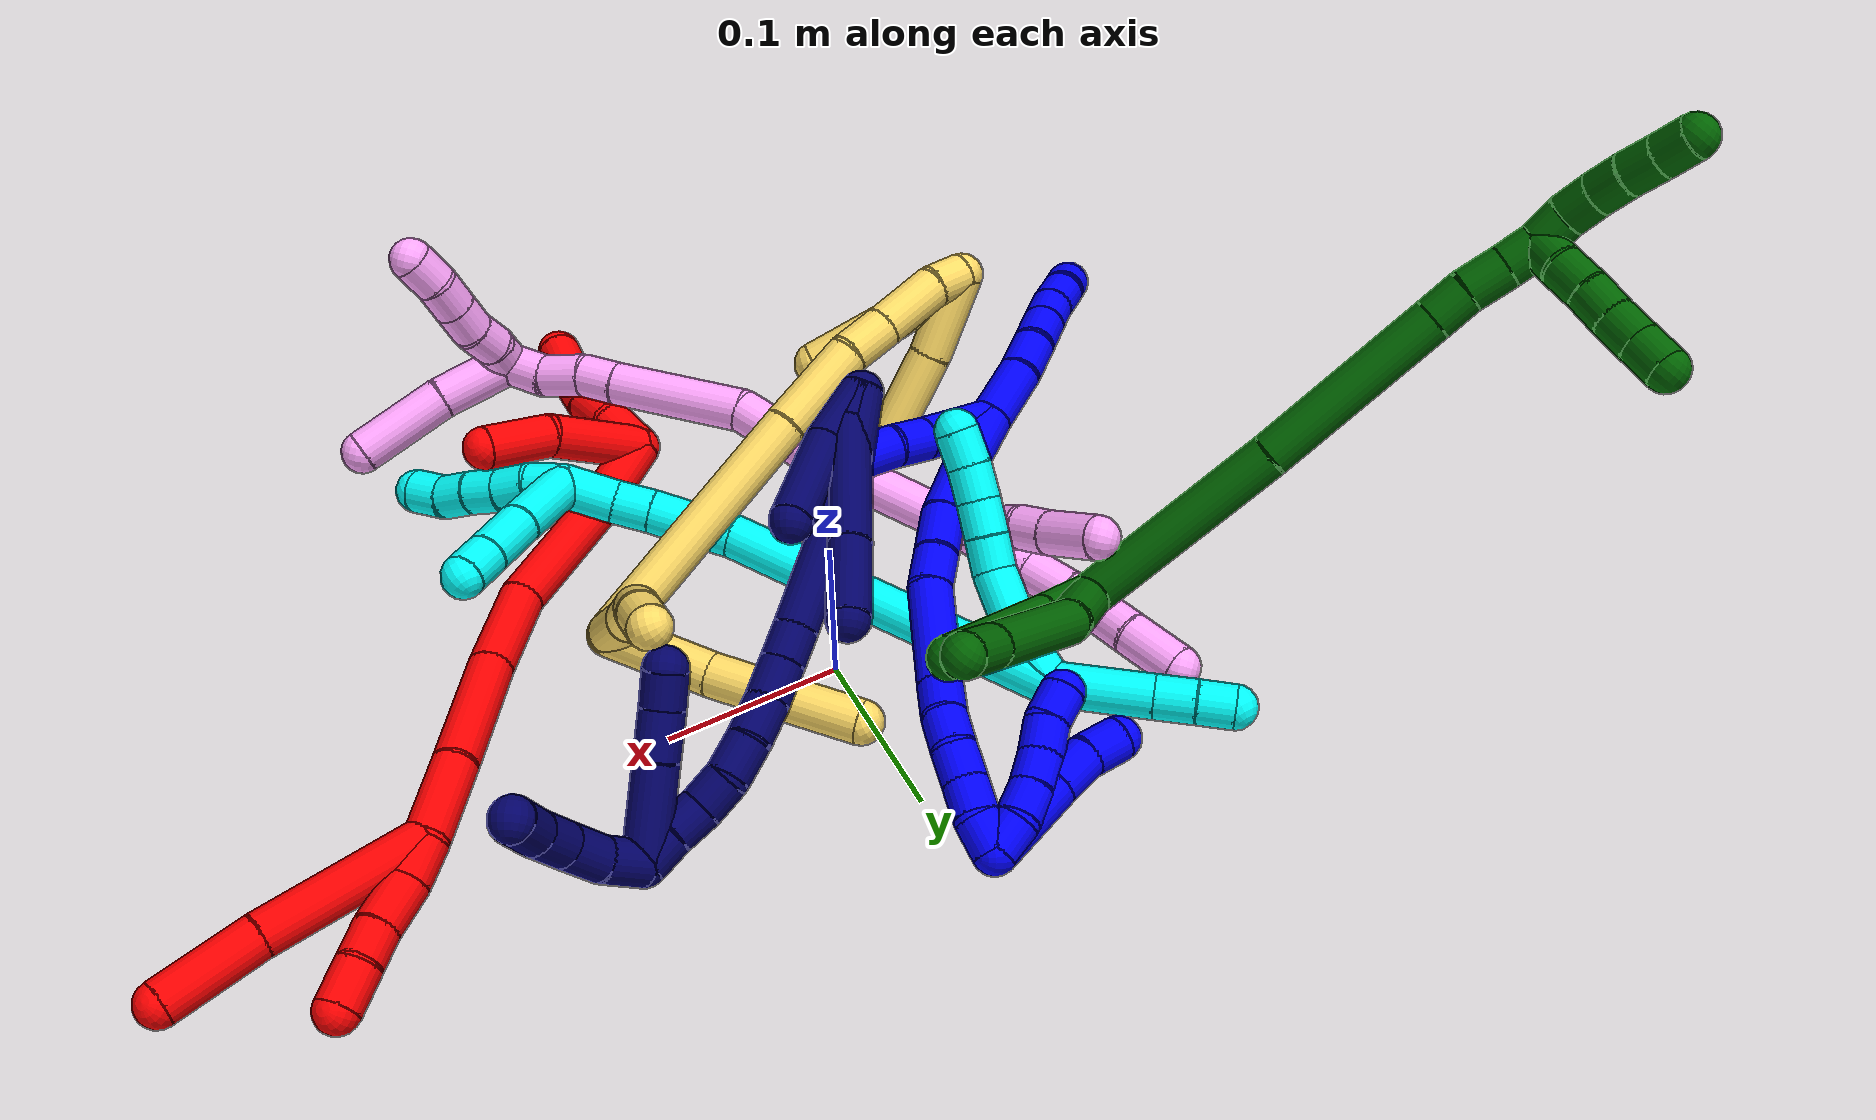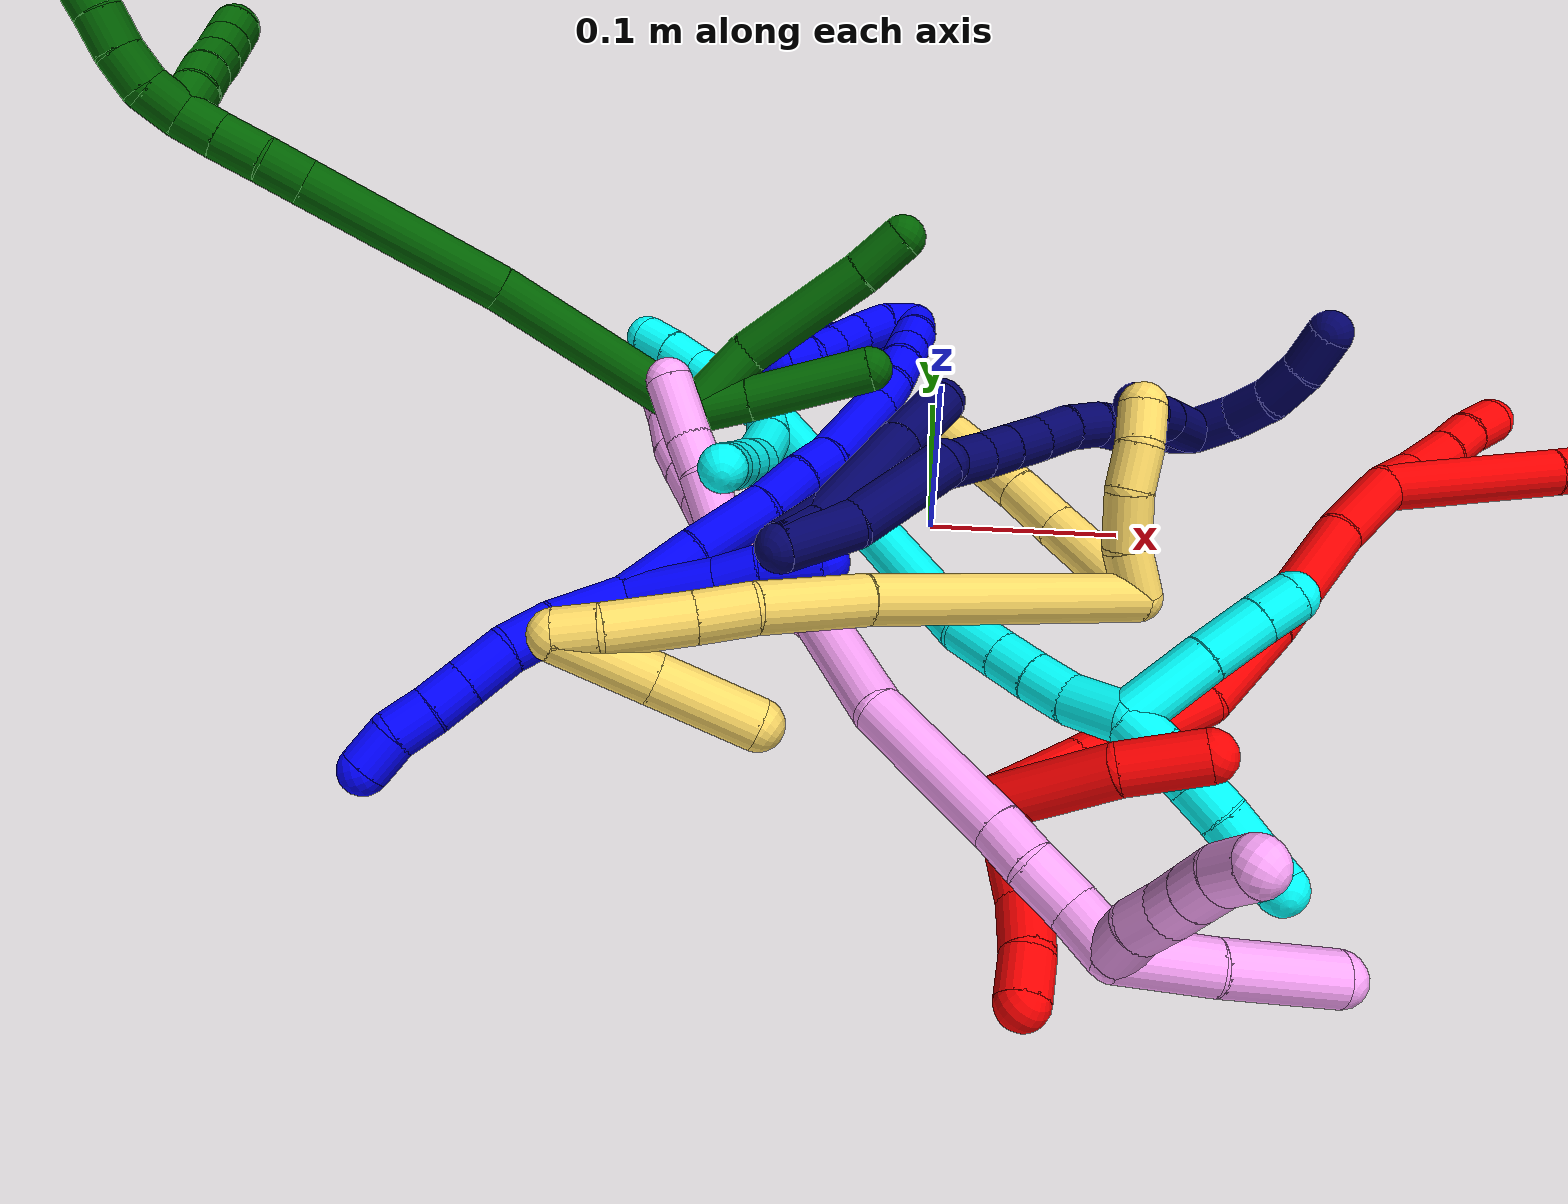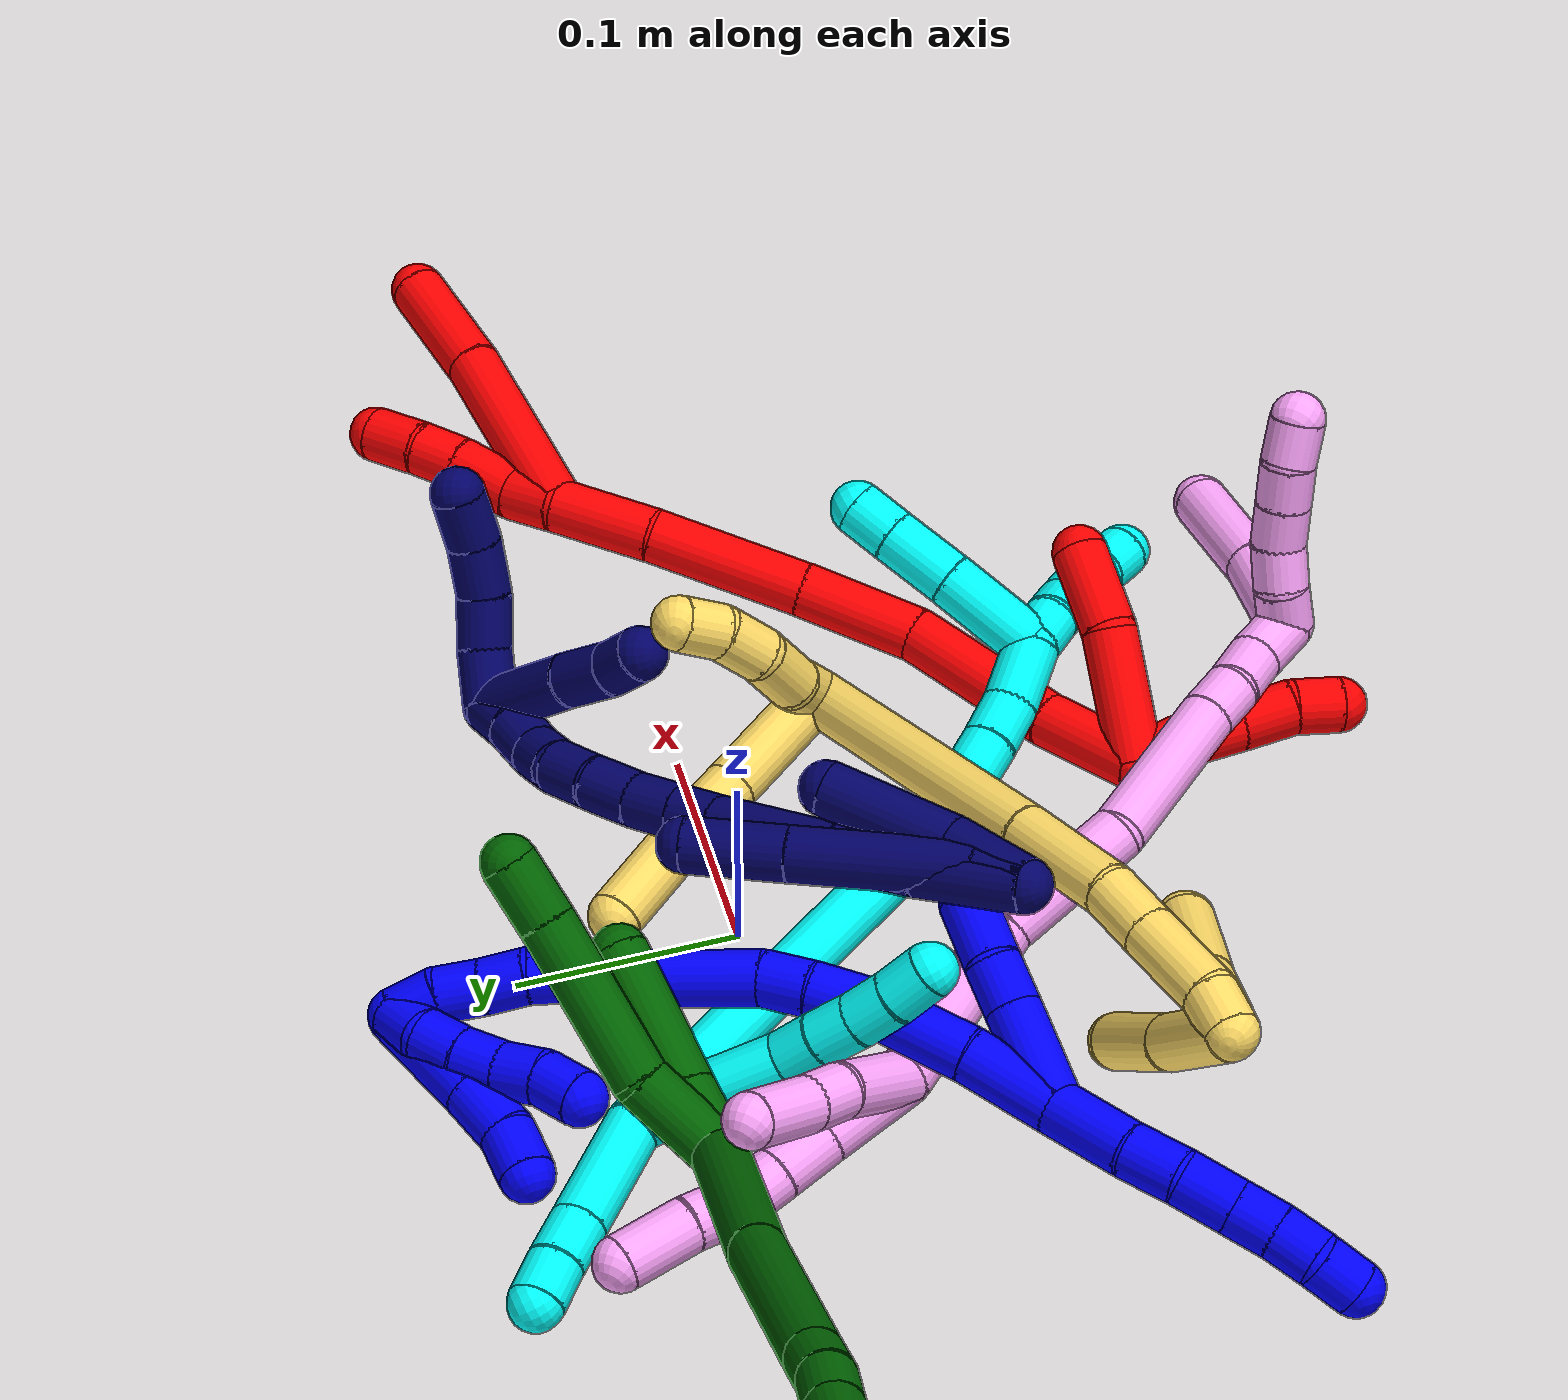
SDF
<sdf version="1.7">
 <world name="default">
  <plugin name="TubeGeneratorPlugin" filename="libtube_generator_plugin.so"/>
  <model name="photoneo_s_sensor">
   <static>1</static>
   <pose>0 0 2 1.57079 1.57079 3.14159</pose>
   <link name="link">
    <inertial><mass>0.1</mass></inertial>
    <sensor name="sensor" type="depth">
     <update_rate>30</update_rate>
     <camera>
      <horizontal_fov>1.22</horizontal_fov>
      <image><width>1920</width><height>1200</height><format>B8G8R8</format></image>
      <clip><near>0.1</near><far>4</far></clip>
      <depth_camera><output>points</output></depth_camera>
     </camera>
     <plugin name="camera_plugin" filename="libgazebo_ros_depth_camera.so">
      <baseline>0.2</baseline>
      <alwaysOn>1</alwaysOn>
      <updateRate>0.0</updateRate>
      <cameraName>camera_ir</cameraName>
      <imageTopicName>/camera/color/image_raw</imageTopicName>
      <cameraInfoTopicName>/camera/color/camera_info</cameraInfoTopicName>
      <depthImageTopicName>/camera/depth/image_raw</depthImageTopicName>
      <depthImageCameraInfoTopicName>/camera/depth/camera_info</depthImageCameraInfoTopicName>
      <pointCloudTopicName>/camera/depth/points</pointCloudTopicName>
      <frameName>fr_optical</frameName>
      <pointCloudCutoff>0.1</pointCloudCutoff>
      <pointCloudCutoffMax>2.0</pointCloudCutoffMax>
      <distortionK1>0</distortionK1>
      <distortionK2>0</distortionK2>
      <distortionK3>0</distortionK3>
      <distortionT1>0</distortionT1>
      <distortionT2>0</distortionT2>
      <CxPrime>0</CxPrime>
      <Cx>0</Cx>
      <Cy>0</Cy>
      <focalLength>0</focalLength>
      <hackBaseline>0</hackBaseline>
     </plugin>
    </sensor>
   </link>
  </model>
  <gravity>0 0 -9.8</gravity>
  <magnetic_field>6e-06 2.3e-05 -4.2e-05</magnetic_field>
  <atmosphere type="adiabatic"/>
  <physics name="default_physics" default="0" type="ode">
   <max_step_size>0.003</max_step_size>
   <real_time_factor>1</real_time_factor>
   <real_time_update_rate>1000</real_time_update_rate>
   <max_contacts>10000</max_contacts>
   <ode>
    <solver>
     <type>quick</type>
     <iters>100</iters>
     <sor>1.3</sor>
     <use_dynamic_moi_rescaling>0</use_dynamic_moi_rescaling>
    </solver>
    <constraints>
     <contact_max_correcting_vel>0</contact_max_correcting_vel>
     <contact_surface_layer>0.001</contact_surface_layer>
     <cfm>0</cfm>
     <erp>0.2</erp>
    </constraints>
   </ode>
  </physics>
  <scene><ambient>0.4 0.4 0.4 1</ambient><background>0.7 0.7 0.7 1</background><shadows>0</shadows></scene>
  <audio><device>default</device></audio>
  <spherical_coordinates>
   <surface_model>EARTH_WGS84</surface_model>
   <latitude_deg>0</latitude_deg>
   <longitude_deg>0</longitude_deg>
   <elevation>0</elevation>
   <heading_deg>0</heading_deg>
  </spherical_coordinates>
  <model name="bin">
   <static>1</static>
   <link name="bottom">
    <collision name="collision-bottom">
     <pose>0 0 -0.01 0 -0 0</pose>
     <geometry><box><size>0.8 0.6 0.02</size></box></geometry>
     <surface>
      <friction><ode><mu>100</mu><mu2>100</mu2></ode></friction>
      <contact><collide_bitmask>65535</collide_bitmask></contact>
     </surface>
    </collision>
   </link>
   <link name="west_wall">
    <collision name="collision-west_wall">
     <pose>-0.41 0 0.1 0 -0 0</pose>
     <geometry><box><size>0.02 0.6 0.2</size></box></geometry>
     <surface>
      <friction><ode><mu>100</mu><mu2>100</mu2></ode></friction>
      <contact><collide_bitmask>65535</collide_bitmask></contact>
     </surface>
    </collision>
   </link>
   <link name="east_wall">
    <collision name="collision-east_wall">
     <pose>0.41 0 0.1 0 -0 0</pose>
     <geometry><box><size>0.02 0.6 0.2</size></box></geometry>
     <surface>
      <friction><ode><mu>100</mu><mu2>100</mu2></ode></friction>
      <contact><collide_bitmask>65535</collide_bitmask></contact>
     </surface>
    </collision>
   </link>
   <link name="south_wall">
    <collision name="collision-south_wall">
     <pose>0 -0.31 0.1 0 -0 0</pose>
     <geometry><box><size>0.8 0.02 0.2</size></box></geometry>
     <surface>
      <friction><ode><mu>100</mu><mu2>100</mu2></ode></friction>
      <contact><collide_bitmask>65535</collide_bitmask></contact>
     </surface>
    </collision>
   </link>
   <link name="north_wall">
    <collision name="collision-north_wall">
     <pose>0 0.31 0.1 0 -0 0</pose>
     <geometry><box><size>0.8 0.02 0.2</size></box></geometry>
     <surface>
      <friction><ode><mu>100</mu><mu2>100</mu2></ode></friction>
      <contact><collide_bitmask>65535</collide_bitmask></contact>
     </surface>
    </collision>
   </link>
  </model>
  <model name="1">
   <static>0</static>
   <link name="1">
    <collision name="collision-cylinder-e_1_2_8">
     <pose>-0.010186 -0.006164 -0.015631 2.76595 -0.544979 -1.94704</pose>
     <geometry><cylinder><radius>0.0125</radius><length>0.039297</length></cylinder></geometry>
     <surface>
      <friction><ode><mu>1.16</mu><mu2>1.16</mu2><slip1>0</slip1><slip2>0</slip2></ode></friction>
      <contact><ode><kp>1e+06</kp><kd>1</kd><max_vel>0</max_vel><min_depth>0.001</min_depth></ode></contact>
     </surface>
    </collision>
    <visual name="visual-cylinder-e_1_2_8">
     <pose>-0.010186 -0.006164 -0.015631 2.76595 -0.544979 -1.94704</pose>
     <geometry><cylinder><radius>0.0125</radius><length>0.039297</length></cylinder></geometry>
     <material><ambient>0 0 1 1</ambient></material>
    </visual>
    <collision name="collision-cylinder-e_2_8_9">
     <pose>-0.026179 -0.017944 -0.040988 2.61799 -0.477225 -1.47422</pose>
     <geometry><cylinder><radius>0.0125</radius><length>0.025287</length></cylinder></geometry>
     <surface>
      <friction><ode><mu>1.16</mu><mu2>1.16</mu2><slip1>0</slip1><slip2>0</slip2></ode></friction>
      <contact><ode><kp>1e+06</kp><kd>1</kd><max_vel>0</max_vel><min_depth>0.001</min_depth></ode></contact>
     </surface>
    </collision>
    <visual name="visual-cylinder-e_2_8_9">
     <pose>-0.026179 -0.017944 -0.040988 2.61799 -0.477225 -1.47422</pose>
     <geometry><cylinder><radius>0.0125</radius><length>0.025287</length></cylinder></geometry>
     <material><ambient>0 0 1 1</ambient></material>
    </visual>
    <collision name="collision-cylinder-e_3_9_10">
     <pose>-0.035426 -0.030533 -0.060449 2.52001 -0.279669 -0.826012</pose>
     <geometry><cylinder><radius>0.0125</radius><length>0.02492</length></cylinder></geometry>
     <surface>
      <friction><ode><mu>1.16</mu><mu2>1.16</mu2><slip1>0</slip1><slip2>0</slip2></ode></friction>
      <contact><ode><kp>1e+06</kp><kd>1</kd><max_vel>0</max_vel><min_depth>0.001</min_depth></ode></contact>
     </surface>
    </collision>
    <visual name="visual-cylinder-e_3_9_10">
     <pose>-0.035426 -0.030533 -0.060449 2.52001 -0.279669 -0.826012</pose>
     <geometry><cylinder><radius>0.0125</radius><length>0.02492</length></cylinder></geometry>
     <material><ambient>0 0 1 1</ambient></material>
    </visual>
    <collision name="collision-cylinder-e_4_10_11">
     <pose>-0.041743 -0.04311 -0.078096 2.52532 -0.288602 -0.856589</pose>
     <geometry><cylinder><radius>0.0125</radius><length>0.020225</length></cylinder></geometry>
     <surface>
      <friction><ode><mu>1.16</mu><mu2>1.16</mu2><slip1>0</slip1><slip2>0</slip2></ode></friction>
      <contact><ode><kp>1e+06</kp><kd>1</kd><max_vel>0</max_vel><min_depth>0.001</min_depth></ode></contact>
     </surface>
    </collision>
    <visual name="visual-cylinder-e_4_10_11">
     <pose>-0.041743 -0.04311 -0.078096 2.52532 -0.288602 -0.856589</pose>
     <geometry><cylinder><radius>0.0125</radius><length>0.020225</length></cylinder></geometry>
     <material><ambient>0 0 1 1</ambient></material>
    </visual>
    <collision name="collision-cylinder-e_5_11_12">
     <pose>-0.047367 -0.053471 -0.094465 2.62923 -0.275746 -0.974272</pose>
     <geometry><cylinder><radius>0.0125</radius><length>0.02017</length></cylinder></geometry>
     <surface>
      <friction><ode><mu>1.16</mu><mu2>1.16</mu2><slip1>0</slip1><slip2>0</slip2></ode></friction>
      <contact><ode><kp>1e+06</kp><kd>1</kd><max_vel>0</max_vel><min_depth>0.001</min_depth></ode></contact>
     </surface>
    </collision>
    <visual name="visual-cylinder-e_5_11_12">
     <pose>-0.047367 -0.053471 -0.094465 2.62923 -0.275746 -0.974272</pose>
     <geometry><cylinder><radius>0.0125</radius><length>0.02017</length></cylinder></geometry>
     <material><ambient>0 0 1 1</ambient></material>
    </visual>
    <collision name="collision-cylinder-e_6_12_6">
     <pose>-0.050156 -0.064517 -0.110762 2.4655 -0.004314 -0.012272</pose>
     <geometry><cylinder><radius>0.0125</radius><length>0.020102</length></cylinder></geometry>
     <surface>
      <friction><ode><mu>1.16</mu><mu2>1.16</mu2><slip1>0</slip1><slip2>0</slip2></ode></friction>
      <contact><ode><kp>1e+06</kp><kd>1</kd><max_vel>0</max_vel><min_depth>0.001</min_depth></ode></contact>
     </surface>
    </collision>
    <visual name="visual-cylinder-e_6_12_6">
     <pose>-0.050156 -0.064517 -0.110762 2.4655 -0.004314 -0.012272</pose>
     <geometry><cylinder><radius>0.0125</radius><length>0.020102</length></cylinder></geometry>
     <material><ambient>0 0 1 1</ambient></material>
    </visual>
    <collision name="collision-cylinder-e_1_2_13">
     <pose>0.002231 -0.001014 0.023285 0.043506 0.095439 0.002078</pose>
     <geometry><cylinder><radius>0.0125</radius><length>0.046827</length></cylinder></geometry>
     <surface>
      <friction><ode><mu>1.16</mu><mu2>1.16</mu2><slip1>0</slip1><slip2>0</slip2></ode></friction>
      <contact><ode><kp>1e+06</kp><kd>1</kd><max_vel>0</max_vel><min_depth>0.001</min_depth></ode></contact>
     </surface>
    </collision>
    <visual name="visual-cylinder-e_1_2_13">
     <pose>0.002231 -0.001014 0.023285 0.043506 0.095439 0.002078</pose>
     <geometry><cylinder><radius>0.0125</radius><length>0.046827</length></cylinder></geometry>
     <material><ambient>0 0 1 1</ambient></material>
    </visual>
    <collision name="collision-cylinder-e_2_13_14">
     <pose>0.004748 -0.001805 0.057738 -0.019862 0.02553 -0.000254</pose>
     <geometry><cylinder><radius>0.0125</radius><length>0.022348</length></cylinder></geometry>
     <surface>
      <friction><ode><mu>1.16</mu><mu2>1.16</mu2><slip1>0</slip1><slip2>0</slip2></ode></friction>
      <contact><ode><kp>1e+06</kp><kd>1</kd><max_vel>0</max_vel><min_depth>0.001</min_depth></ode></contact>
     </surface>
    </collision>
    <visual name="visual-cylinder-e_2_13_14">
     <pose>0.004748 -0.001805 0.057738 -0.019862 0.02553 -0.000254</pose>
     <geometry><cylinder><radius>0.0125</radius><length>0.022348</length></cylinder></geometry>
     <material><ambient>0 0 1 1</ambient></material>
    </visual>
    <collision name="collision-cylinder-e_3_14_5">
     <pose>0.007688 -0.003292 0.083992 0.112785 0.173114 0.009797</pose>
     <geometry><cylinder><radius>0.0125</radius><length>0.030825</length></cylinder></geometry>
     <surface>
      <friction><ode><mu>1.16</mu><mu2>1.16</mu2><slip1>0</slip1><slip2>0</slip2></ode></friction>
      <contact><ode><kp>1e+06</kp><kd>1</kd><max_vel>0</max_vel><min_depth>0.001</min_depth></ode></contact>
     </surface>
    </collision>
    <visual name="visual-cylinder-e_3_14_5">
     <pose>0.007688 -0.003292 0.083992 0.112785 0.173114 0.009797</pose>
     <geometry><cylinder><radius>0.0125</radius><length>0.030825</length></cylinder></geometry>
     <material><ambient>0 0 1 1</ambient></material>
    </visual>
    <collision name="collision-cylinder-e_1_2_15">
     <pose>0.006608 0.010851 0.017107 -0.565263 0.31533 -0.092275</pose>
     <geometry><cylinder><radius>0.0125</radius><length>0.042617</length></cylinder></geometry>
     <surface>
      <friction><ode><mu>1.16</mu><mu2>1.16</mu2><slip1>0</slip1><slip2>0</slip2></ode></friction>
      <contact><ode><kp>1e+06</kp><kd>1</kd><max_vel>0</max_vel><min_depth>0.001</min_depth></ode></contact>
     </surface>
    </collision>
    <visual name="visual-cylinder-e_1_2_15">
     <pose>0.006608 0.010851 0.017107 -0.565263 0.31533 -0.092275</pose>
     <geometry><cylinder><radius>0.0125</radius><length>0.042617</length></cylinder></geometry>
     <material><ambient>0 0 1 1</ambient></material>
    </visual>
    <collision name="collision-cylinder-e_2_15_16">
     <pose>0.02243 0.033124 0.051261 -0.590306 0.421989 -0.130054</pose>
     <geometry><cylinder><radius>0.0125</radius><length>0.044988</length></cylinder></geometry>
     <surface>
      <friction><ode><mu>1.16</mu><mu2>1.16</mu2><slip1>0</slip1><slip2>0</slip2></ode></friction>
      <contact><ode><kp>1e+06</kp><kd>1</kd><max_vel>0</max_vel><min_depth>0.001</min_depth></ode></contact>
     </surface>
    </collision>
    <visual name="visual-cylinder-e_2_15_16">
     <pose>0.02243 0.033124 0.051261 -0.590306 0.421989 -0.130054</pose>
     <geometry><cylinder><radius>0.0125</radius><length>0.044988</length></cylinder></geometry>
     <material><ambient>0 0 1 1</ambient></material>
    </visual>
    <collision name="collision-cylinder-e_3_16_17">
     <pose>0.038166 0.053466 0.077448 -0.773233 0.472228 -0.195278</pose>
     <geometry><cylinder><radius>0.0125</radius><length>0.02868</length></cylinder></geometry>
     <surface>
      <friction><ode><mu>1.16</mu><mu2>1.16</mu2><slip1>0</slip1><slip2>0</slip2></ode></friction>
      <contact><ode><kp>1e+06</kp><kd>1</kd><max_vel>0</max_vel><min_depth>0.001</min_depth></ode></contact>
     </surface>
    </collision>
    <visual name="visual-cylinder-e_3_16_17">
     <pose>0.038166 0.053466 0.077448 -0.773233 0.472228 -0.195278</pose>
     <geometry><cylinder><radius>0.0125</radius><length>0.02868</length></cylinder></geometry>
     <material><ambient>0 0 1 1</ambient></material>
    </visual>
    <collision name="collision-cylinder-e_4_17_18">
     <pose>0.050868 0.068585 0.093203 -0.75298 0.59828 -0.242649</pose>
     <geometry><cylinder><radius>0.0125</radius><length>0.021943</length></cylinder></geometry>
     <surface>
      <friction><ode><mu>1.16</mu><mu2>1.16</mu2><slip1>0</slip1><slip2>0</slip2></ode></friction>
      <contact><ode><kp>1e+06</kp><kd>1</kd><max_vel>0</max_vel><min_depth>0.001</min_depth></ode></contact>
     </surface>
    </collision>
    <visual name="visual-cylinder-e_4_17_18">
     <pose>0.050868 0.068585 0.093203 -0.75298 0.59828 -0.242649</pose>
     <geometry><cylinder><radius>0.0125</radius><length>0.021943</length></cylinder></geometry>
     <material><ambient>0 0 1 1</ambient></material>
    </visual>
    <collision name="collision-cylinder-e_5_18_19">
     <pose>0.07505 0.095988 0.111844 -1.05486 0.636126 -0.378947</pose>
     <geometry><cylinder><radius>0.0125</radius><length>0.060609</length></cylinder></geometry>
     <surface>
      <friction><ode><mu>1.16</mu><mu2>1.16</mu2><slip1>0</slip1><slip2>0</slip2></ode></friction>
      <contact><ode><kp>1e+06</kp><kd>1</kd><max_vel>0</max_vel><min_depth>0.001</min_depth></ode></contact>
     </surface>
    </collision>
    <visual name="visual-cylinder-e_5_18_19">
     <pose>0.07505 0.095988 0.111844 -1.05486 0.636126 -0.378947</pose>
     <geometry><cylinder><radius>0.0125</radius><length>0.060609</length></cylinder></geometry>
     <material><ambient>0 0 1 1</ambient></material>
    </visual>
    <collision name="collision-cylinder-e_6_19_20">
     <pose>0.097315 0.12541 0.128799 -1.03052 0.418362 -0.239281</pose>
     <geometry><cylinder><radius>0.0125</radius><length>0.020976</length></cylinder></geometry>
     <surface>
      <friction><ode><mu>1.16</mu><mu2>1.16</mu2><slip1>0</slip1><slip2>0</slip2></ode></friction>
      <contact><ode><kp>1e+06</kp><kd>1</kd><max_vel>0</max_vel><min_depth>0.001</min_depth></ode></contact>
     </surface>
    </collision>
    <visual name="visual-cylinder-e_6_19_20">
     <pose>0.097315 0.12541 0.128799 -1.03052 0.418362 -0.239281</pose>
     <geometry><cylinder><radius>0.0125</radius><length>0.020976</length></cylinder></geometry>
     <material><ambient>0 0 1 1</ambient></material>
    </visual>
    <collision name="collision-cylinder-e_7_20_21">
     <pose>0.106469 0.141885 0.136853 -1.2091 0.506169 -0.353611</pose>
     <geometry><cylinder><radius>0.0125</radius><length>0.020188</length></cylinder></geometry>
     <surface>
      <friction><ode><mu>1.16</mu><mu2>1.16</mu2><slip1>0</slip1><slip2>0</slip2></ode></friction>
      <contact><ode><kp>1e+06</kp><kd>1</kd><max_vel>0</max_vel><min_depth>0.001</min_depth></ode></contact>
     </surface>
    </collision>
    <visual name="visual-cylinder-e_7_20_21">
     <pose>0.106469 0.141885 0.136853 -1.2091 0.506169 -0.353611</pose>
     <geometry><cylinder><radius>0.0125</radius><length>0.020188</length></cylinder></geometry>
     <material><ambient>0 0 1 1</ambient></material>
    </visual>
    <collision name="collision-cylinder-e_8_21_22">
     <pose>0.117732 0.157666 0.14166 -1.35065 0.690414 -0.560878</pose>
     <geometry><cylinder><radius>0.0125</radius><length>0.02</length></cylinder></geometry>
     <surface>
      <friction><ode><mu>1.16</mu><mu2>1.16</mu2><slip1>0</slip1><slip2>0</slip2></ode></friction>
      <contact><ode><kp>1e+06</kp><kd>1</kd><max_vel>0</max_vel><min_depth>0.001</min_depth></ode></contact>
     </surface>
    </collision>
    <visual name="visual-cylinder-e_8_21_22">
     <pose>0.117732 0.157666 0.14166 -1.35065 0.690414 -0.560878</pose>
     <geometry><cylinder><radius>0.0125</radius><length>0.02</length></cylinder></geometry>
     <material><ambient>0 0 1 1</ambient></material>
    </visual>
    <collision name="collision-cylinder-e_9_22_23">
     <pose>0.129905 0.173034 0.14553 -1.29904 0.619281 -0.476702</pose>
     <geometry><cylinder><radius>0.0125</radius><length>0.02</length></cylinder></geometry>
     <surface>
      <friction><ode><mu>1.16</mu><mu2>1.16</mu2><slip1>0</slip1><slip2>0</slip2></ode></friction>
      <contact><ode><kp>1e+06</kp><kd>1</kd><max_vel>0</max_vel><min_depth>0.001</min_depth></ode></contact>
     </surface>
    </collision>
    <visual name="visual-cylinder-e_9_22_23">
     <pose>0.129905 0.173034 0.14553 -1.29904 0.619281 -0.476702</pose>
     <geometry><cylinder><radius>0.0125</radius><length>0.02</length></cylinder></geometry>
     <material><ambient>0 0 1 1</ambient></material>
    </visual>
    <collision name="collision-cylinder-e_10_23_1">
     <pose>0.14225 0.188427 0.147231 -1.63495 0.712937 -0.755951</pose>
     <geometry><cylinder><radius>0.0125</radius><length>0.02</length></cylinder></geometry>
     <surface>
      <friction><ode><mu>1.16</mu><mu2>1.16</mu2><slip1>0</slip1><slip2>0</slip2></ode></friction>
      <contact><ode><kp>1e+06</kp><kd>1</kd><max_vel>0</max_vel><min_depth>0.001</min_depth></ode></contact>
     </surface>
    </collision>
    <visual name="visual-cylinder-e_10_23_1">
     <pose>0.14225 0.188427 0.147231 -1.63495 0.712937 -0.755951</pose>
     <geometry><cylinder><radius>0.0125</radius><length>0.02</length></cylinder></geometry>
     <material><ambient>0 0 1 1</ambient></material>
    </visual>
    <collision name="collision-cylinder-e_1_1_24">
     <pose>0.142389 0.195013 0.139123 3.01596 -0.694641 -2.79751</pose>
     <geometry><cylinder><radius>0.0125</radius><length>0.02</length></cylinder></geometry>
     <surface>
      <friction><ode><mu>1.16</mu><mu2>1.16</mu2><slip1>0</slip1><slip2>0</slip2></ode></friction>
      <contact><ode><kp>1e+06</kp><kd>1</kd><max_vel>0</max_vel><min_depth>0.001</min_depth></ode></contact>
     </surface>
    </collision>
    <visual name="visual-cylinder-e_1_1_24">
     <pose>0.142389 0.195013 0.139123 3.01596 -0.694641 -2.79751</pose>
     <geometry><cylinder><radius>0.0125</radius><length>0.02</length></cylinder></geometry>
     <material><ambient>0 0 1 1</ambient></material>
    </visual>
    <collision name="collision-cylinder-e_2_24_25">
     <pose>0.130832 0.190132 0.123881 2.66665 -0.541705 -1.70772</pose>
     <geometry><cylinder><radius>0.0125</radius><length>0.02</length></cylinder></geometry>
     <surface>
      <friction><ode><mu>1.16</mu><mu2>1.16</mu2><slip1>0</slip1><slip2>0</slip2></ode></friction>
      <contact><ode><kp>1e+06</kp><kd>1</kd><max_vel>0</max_vel><min_depth>0.001</min_depth></ode></contact>
     </surface>
    </collision>
    <visual name="visual-cylinder-e_2_24_25">
     <pose>0.130832 0.190132 0.123881 2.66665 -0.541705 -1.70772</pose>
     <geometry><cylinder><radius>0.0125</radius><length>0.02</length></cylinder></geometry>
     <material><ambient>0 0 1 1</ambient></material>
    </visual>
    <collision name="collision-cylinder-e_3_25_26">
     <pose>0.120301 0.18128 0.109423 2.51652 -0.567567 -1.46851</pose>
     <geometry><cylinder><radius>0.0125</radius><length>0.02</length></cylinder></geometry>
     <surface>
      <friction><ode><mu>1.16</mu><mu2>1.16</mu2><slip1>0</slip1><slip2>0</slip2></ode></friction>
      <contact><ode><kp>1e+06</kp><kd>1</kd><max_vel>0</max_vel><min_depth>0.001</min_depth></ode></contact>
     </surface>
    </collision>
    <visual name="visual-cylinder-e_3_25_26">
     <pose>0.120301 0.18128 0.109423 2.51652 -0.567567 -1.46851</pose>
     <geometry><cylinder><radius>0.0125</radius><length>0.02</length></cylinder></geometry>
     <material><ambient>0 0 1 1</ambient></material>
    </visual>
    <collision name="collision-cylinder-e_4_26_27">
     <pose>0.108299 0.171487 0.096886 2.43564 -0.724223 -1.59867</pose>
     <geometry><cylinder><radius>0.0125</radius><length>0.02</length></cylinder></geometry>
     <surface>
      <friction><ode><mu>1.16</mu><mu2>1.16</mu2><slip1>0</slip1><slip2>0</slip2></ode></friction>
      <contact><ode><kp>1e+06</kp><kd>1</kd><max_vel>0</max_vel><min_depth>0.001</min_depth></ode></contact>
     </surface>
    </collision>
    <visual name="visual-cylinder-e_4_26_27">
     <pose>0.108299 0.171487 0.096886 2.43564 -0.724223 -1.59867</pose>
     <geometry><cylinder><radius>0.0125</radius><length>0.02</length></cylinder></geometry>
     <material><ambient>0 0 1 1</ambient></material>
    </visual>
    <collision name="collision-cylinder-e_5_27_4">
     <pose>0.09613 0.163479 0.083481 2.75365 -0.587557 -1.98979</pose>
     <geometry><cylinder><radius>0.0125</radius><length>0.02</length></cylinder></geometry>
     <surface>
      <friction><ode><mu>1.16</mu><mu2>1.16</mu2><slip1>0</slip1><slip2>0</slip2></ode></friction>
      <contact><ode><kp>1e+06</kp><kd>1</kd><max_vel>0</max_vel><min_depth>0.001</min_depth></ode></contact>
     </surface>
    </collision>
    <visual name="visual-cylinder-e_5_27_4">
     <pose>0.09613 0.163479 0.083481 2.75365 -0.587557 -1.98979</pose>
     <geometry><cylinder><radius>0.0125</radius><length>0.02</length></cylinder></geometry>
     <material><ambient>0 0 1 1</ambient></material>
    </visual>
    <collision name="collision-cylinder-e_1_1_28">
     <pose>0.138504 0.191429 0.123522 2.94824 -0.410027 -2.26879</pose>
     <geometry><cylinder><radius>0.0125</radius><length>0.051607</length></cylinder></geometry>
     <surface>
      <friction><ode><mu>1.16</mu><mu2>1.16</mu2><slip1>0</slip1><slip2>0</slip2></ode></friction>
      <contact><ode><kp>1e+06</kp><kd>1</kd><max_vel>0</max_vel><min_depth>0.001</min_depth></ode></contact>
     </surface>
    </collision>
    <visual name="visual-cylinder-e_1_1_28">
     <pose>0.138504 0.191429 0.123522 2.94824 -0.410027 -2.26879</pose>
     <geometry><cylinder><radius>0.0125</radius><length>0.051607</length></cylinder></geometry>
     <material><ambient>0 0 1 1</ambient></material>
    </visual>
    <collision name="collision-cylinder-e_2_28_29">
     <pose>0.123234 0.184971 0.088235 2.9845 -0.387463 -2.37856</pose>
     <geometry><cylinder><radius>0.0125</radius><length>0.026382</length></cylinder></geometry>
     <surface>
      <friction><ode><mu>1.16</mu><mu2>1.16</mu2><slip1>0</slip1><slip2>0</slip2></ode></friction>
      <contact><ode><kp>1e+06</kp><kd>1</kd><max_vel>0</max_vel><min_depth>0.001</min_depth></ode></contact>
     </surface>
    </collision>
    <visual name="visual-cylinder-e_2_28_29">
     <pose>0.123234 0.184971 0.088235 2.9845 -0.387463 -2.37856</pose>
     <geometry><cylinder><radius>0.0125</radius><length>0.026382</length></cylinder></geometry>
     <material><ambient>0 0 1 1</ambient></material>
    </visual>
    <collision name="collision-cylinder-e_3_29_3">
     <pose>0.115442 0.18383 0.065559 -3.06921 -0.257993 2.59724</pose>
     <geometry><cylinder><radius>0.0125</radius><length>0.022011</length></cylinder></geometry>
     <surface>
      <friction><ode><mu>1.16</mu><mu2>1.16</mu2><slip1>0</slip1><slip2>0</slip2></ode></friction>
      <contact><ode><kp>1e+06</kp><kd>1</kd><max_vel>0</max_vel><min_depth>0.001</min_depth></ode></contact>
     </surface>
    </collision>
    <visual name="visual-cylinder-e_3_29_3">
     <pose>0.115442 0.18383 0.065559 -3.06921 -0.257993 2.59724</pose>
     <geometry><cylinder><radius>0.0125</radius><length>0.022011</length></cylinder></geometry>
     <material><ambient>0 0 1 1</ambient></material>
    </visual>
    <collision name="collision-sphere-3">
     <pose>0.112634 0.184599 0.054946 0 -0 0</pose>
     <geometry><sphere><radius>0.0125</radius></sphere></geometry>
     <surface>
      <friction><ode><mu>1.16</mu><mu2>1.16</mu2><slip1>0</slip1><slip2>0</slip2></ode></friction>
      <contact><ode><kp>1e+06</kp><kd>1</kd><max_vel>0</max_vel><min_depth>0.001</min_depth></ode></contact>
     </surface>
    </collision>
    <visual name="visual-sphere-3">
     <pose>0.112634 0.184599 0.054946 0 -0 0</pose>
     <geometry><sphere><radius>0.0125</radius></sphere></geometry>
     <material><ambient>0 0 1 1</ambient></material>
    </visual>
    <collision name="collision-sphere-29">
     <pose>0.11825 0.18306 0.076173 0 -0 0</pose>
     <geometry><sphere><radius>0.0125</radius></sphere></geometry>
     <surface>
      <friction><ode><mu>1.16</mu><mu2>1.16</mu2><slip1>0</slip1><slip2>0</slip2></ode></friction>
      <contact><ode><kp>1e+06</kp><kd>1</kd><max_vel>0</max_vel><min_depth>0.001</min_depth></ode></contact>
     </surface>
    </collision>
    <visual name="visual-sphere-29">
     <pose>0.11825 0.18306 0.076173 0 -0 0</pose>
     <geometry><sphere><radius>0.0125</radius></sphere></geometry>
     <material><ambient>0 0 1 1</ambient></material>
    </visual>
    <collision name="collision-sphere-28">
     <pose>0.128218 0.186882 0.100298 0 -0 0</pose>
     <geometry><sphere><radius>0.0125</radius></sphere></geometry>
     <surface>
      <friction><ode><mu>1.16</mu><mu2>1.16</mu2><slip1>0</slip1><slip2>0</slip2></ode></friction>
      <contact><ode><kp>1e+06</kp><kd>1</kd><max_vel>0</max_vel><min_depth>0.001</min_depth></ode></contact>
     </surface>
    </collision>
    <visual name="visual-sphere-28">
     <pose>0.128218 0.186882 0.100298 0 -0 0</pose>
     <geometry><sphere><radius>0.0125</radius></sphere></geometry>
     <material><ambient>0 0 1 1</ambient></material>
    </visual>
    <collision name="collision-sphere-4">
     <pose>0.090587 0.160331 0.075777 0 -0 0</pose>
     <geometry><sphere><radius>0.0125</radius></sphere></geometry>
     <surface>
      <friction><ode><mu>1.16</mu><mu2>1.16</mu2><slip1>0</slip1><slip2>0</slip2></ode></friction>
      <contact><ode><kp>1e+06</kp><kd>1</kd><max_vel>0</max_vel><min_depth>0.001</min_depth></ode></contact>
     </surface>
    </collision>
    <visual name="visual-sphere-4">
     <pose>0.090587 0.160331 0.075777 0 -0 0</pose>
     <geometry><sphere><radius>0.0125</radius></sphere></geometry>
     <material><ambient>0 0 1 1</ambient></material>
    </visual>
    <collision name="collision-sphere-27">
     <pose>0.101674 0.166628 0.091186 0 -0 0</pose>
     <geometry><sphere><radius>0.0125</radius></sphere></geometry>
     <surface>
      <friction><ode><mu>1.16</mu><mu2>1.16</mu2><slip1>0</slip1><slip2>0</slip2></ode></friction>
      <contact><ode><kp>1e+06</kp><kd>1</kd><max_vel>0</max_vel><min_depth>0.001</min_depth></ode></contact>
     </surface>
    </collision>
    <visual name="visual-sphere-27">
     <pose>0.101674 0.166628 0.091186 0 -0 0</pose>
     <geometry><sphere><radius>0.0125</radius></sphere></geometry>
     <material><ambient>0 0 1 1</ambient></material>
    </visual>
    <collision name="collision-sphere-26">
     <pose>0.114925 0.176346 0.102586 0 -0 0</pose>
     <geometry><sphere><radius>0.0125</radius></sphere></geometry>
     <surface>
      <friction><ode><mu>1.16</mu><mu2>1.16</mu2><slip1>0</slip1><slip2>0</slip2></ode></friction>
      <contact><ode><kp>1e+06</kp><kd>1</kd><max_vel>0</max_vel><min_depth>0.001</min_depth></ode></contact>
     </surface>
    </collision>
    <visual name="visual-sphere-26">
     <pose>0.114925 0.176346 0.102586 0 -0 0</pose>
     <geometry><sphere><radius>0.0125</radius></sphere></geometry>
     <material><ambient>0 0 1 1</ambient></material>
    </visual>
    <collision name="collision-sphere-25">
     <pose>0.125676 0.186214 0.116261 0 -0 0</pose>
     <geometry><sphere><radius>0.0125</radius></sphere></geometry>
     <surface>
      <friction><ode><mu>1.16</mu><mu2>1.16</mu2><slip1>0</slip1><slip2>0</slip2></ode></friction>
      <contact><ode><kp>1e+06</kp><kd>1</kd><max_vel>0</max_vel><min_depth>0.001</min_depth></ode></contact>
     </surface>
    </collision>
    <visual name="visual-sphere-25">
     <pose>0.125676 0.186214 0.116261 0 -0 0</pose>
     <geometry><sphere><radius>0.0125</radius></sphere></geometry>
     <material><ambient>0 0 1 1</ambient></material>
    </visual>
    <collision name="collision-sphere-24">
     <pose>0.135988 0.194051 0.131501 0 -0 0</pose>
     <geometry><sphere><radius>0.0125</radius></sphere></geometry>
     <surface>
      <friction><ode><mu>1.16</mu><mu2>1.16</mu2><slip1>0</slip1><slip2>0</slip2></ode></friction>
      <contact><ode><kp>1e+06</kp><kd>1</kd><max_vel>0</max_vel><min_depth>0.001</min_depth></ode></contact>
     </surface>
    </collision>
    <visual name="visual-sphere-24">
     <pose>0.135988 0.194051 0.131501 0 -0 0</pose>
     <geometry><sphere><radius>0.0125</radius></sphere></geometry>
     <material><ambient>0 0 1 1</ambient></material>
    </visual>
    <collision name="collision-sphere-1">
     <pose>0.148791 0.195976 0.146746 0 -0 0</pose>
     <geometry><sphere><radius>0.0125</radius></sphere></geometry>
     <surface>
      <friction><ode><mu>1.16</mu><mu2>1.16</mu2><slip1>0</slip1><slip2>0</slip2></ode></friction>
      <contact><ode><kp>1e+06</kp><kd>1</kd><max_vel>0</max_vel><min_depth>0.001</min_depth></ode></contact>
     </surface>
    </collision>
    <visual name="visual-sphere-1">
     <pose>0.148791 0.195976 0.146746 0 -0 0</pose>
     <geometry><sphere><radius>0.0125</radius></sphere></geometry>
     <material><ambient>0 0 1 1</ambient></material>
    </visual>
    <collision name="collision-sphere-23">
     <pose>0.135709 0.180878 0.147716 0 -0 0</pose>
     <geometry><sphere><radius>0.0125</radius></sphere></geometry>
     <surface>
      <friction><ode><mu>1.16</mu><mu2>1.16</mu2><slip1>0</slip1><slip2>0</slip2></ode></friction>
      <contact><ode><kp>1e+06</kp><kd>1</kd><max_vel>0</max_vel><min_depth>0.001</min_depth></ode></contact>
     </surface>
    </collision>
    <visual name="visual-sphere-23">
     <pose>0.135709 0.180878 0.147716 0 -0 0</pose>
     <geometry><sphere><radius>0.0125</radius></sphere></geometry>
     <material><ambient>0 0 1 1</ambient></material>
    </visual>
    <collision name="collision-sphere-22">
     <pose>0.1241 0.16519 0.143344 0 -0 0</pose>
     <geometry><sphere><radius>0.0125</radius></sphere></geometry>
     <surface>
      <friction><ode><mu>1.16</mu><mu2>1.16</mu2><slip1>0</slip1><slip2>0</slip2></ode></friction>
      <contact><ode><kp>1e+06</kp><kd>1</kd><max_vel>0</max_vel><min_depth>0.001</min_depth></ode></contact>
     </surface>
    </collision>
    <visual name="visual-sphere-22">
     <pose>0.1241 0.16519 0.143344 0 -0 0</pose>
     <geometry><sphere><radius>0.0125</radius></sphere></geometry>
     <material><ambient>0 0 1 1</ambient></material>
    </visual>
    <collision name="collision-sphere-21">
     <pose>0.111363 0.150142 0.139977 0 -0 0</pose>
     <geometry><sphere><radius>0.0125</radius></sphere></geometry>
     <surface>
      <friction><ode><mu>1.16</mu><mu2>1.16</mu2><slip1>0</slip1><slip2>0</slip2></ode></friction>
      <contact><ode><kp>1e+06</kp><kd>1</kd><max_vel>0</max_vel><min_depth>0.001</min_depth></ode></contact>
     </surface>
    </collision>
    <visual name="visual-sphere-21">
     <pose>0.111363 0.150142 0.139977 0 -0 0</pose>
     <geometry><sphere><radius>0.0125</radius></sphere></geometry>
     <material><ambient>0 0 1 1</ambient></material>
    </visual>
    <collision name="collision-sphere-12">
     <pose>-0.050113 -0.058228 -0.102923 0 -0 0</pose>
     <geometry><sphere><radius>0.0125</radius></sphere></geometry>
     <surface>
      <friction><ode><mu>1.16</mu><mu2>1.16</mu2><slip1>0</slip1><slip2>0</slip2></ode></friction>
      <contact><ode><kp>1e+06</kp><kd>1</kd><max_vel>0</max_vel><min_depth>0.001</min_depth></ode></contact>
     </surface>
    </collision>
    <visual name="visual-sphere-12">
     <pose>-0.050113 -0.058228 -0.102923 0 -0 0</pose>
     <geometry><sphere><radius>0.0125</radius></sphere></geometry>
     <material><ambient>0 0 1 1</ambient></material>
    </visual>
    <collision name="collision-sphere-11">
     <pose>-0.044621 -0.048713 -0.086007 0 -0 0</pose>
     <geometry><sphere><radius>0.0125</radius></sphere></geometry>
     <surface>
      <friction><ode><mu>1.16</mu><mu2>1.16</mu2><slip1>0</slip1><slip2>0</slip2></ode></friction>
      <contact><ode><kp>1e+06</kp><kd>1</kd><max_vel>0</max_vel><min_depth>0.001</min_depth></ode></contact>
     </surface>
    </collision>
    <visual name="visual-sphere-11">
     <pose>-0.044621 -0.048713 -0.086007 0 -0 0</pose>
     <geometry><sphere><radius>0.0125</radius></sphere></geometry>
     <material><ambient>0 0 1 1</ambient></material>
    </visual>
    <collision name="collision-sphere-10">
     <pose>-0.038865 -0.037507 -0.070185 0 -0 0</pose>
     <geometry><sphere><radius>0.0125</radius></sphere></geometry>
     <surface>
      <friction><ode><mu>1.16</mu><mu2>1.16</mu2><slip1>0</slip1><slip2>0</slip2></ode></friction>
      <contact><ode><kp>1e+06</kp><kd>1</kd><max_vel>0</max_vel><min_depth>0.001</min_depth></ode></contact>
     </surface>
    </collision>
    <visual name="visual-sphere-10">
     <pose>-0.038865 -0.037507 -0.070185 0 -0 0</pose>
     <geometry><sphere><radius>0.0125</radius></sphere></geometry>
     <material><ambient>0 0 1 1</ambient></material>
    </visual>
    <collision name="collision-sphere-9">
     <pose>-0.031986 -0.023559 -0.050714 0 -0 0</pose>
     <geometry><sphere><radius>0.0125</radius></sphere></geometry>
     <surface>
      <friction><ode><mu>1.16</mu><mu2>1.16</mu2><slip1>0</slip1><slip2>0</slip2></ode></friction>
      <contact><ode><kp>1e+06</kp><kd>1</kd><max_vel>0</max_vel><min_depth>0.001</min_depth></ode></contact>
     </surface>
    </collision>
    <visual name="visual-sphere-9">
     <pose>-0.031986 -0.023559 -0.050714 0 -0 0</pose>
     <geometry><sphere><radius>0.0125</radius></sphere></geometry>
     <material><ambient>0 0 1 1</ambient></material>
    </visual>
    <collision name="collision-sphere-2">
     <geometry><sphere><radius>0.0125</radius></sphere></geometry>
     <surface>
      <friction><ode><mu>1.16</mu><mu2>1.16</mu2><slip1>0</slip1><slip2>0</slip2></ode></friction>
      <contact><ode><kp>1e+06</kp><kd>1</kd><max_vel>0</max_vel><min_depth>0.001</min_depth></ode></contact>
     </surface>
    </collision>
    <visual name="visual-sphere-2">
     <geometry><sphere><radius>0.0125</radius></sphere></geometry>
     <material><ambient>0 0 1 1</ambient></material>
    </visual>
    <collision name="collision-sphere-19">
     <pose>0.093054 0.117192 0.12387 0 -0 0</pose>
     <geometry><sphere><radius>0.0125</radius></sphere></geometry>
     <surface>
      <friction><ode><mu>1.16</mu><mu2>1.16</mu2><slip1>0</slip1><slip2>0</slip2></ode></friction>
      <contact><ode><kp>1e+06</kp><kd>1</kd><max_vel>0</max_vel><min_depth>0.001</min_depth></ode></contact>
     </surface>
    </collision>
    <visual name="visual-sphere-19">
     <pose>0.093054 0.117192 0.12387 0 -0 0</pose>
     <geometry><sphere><radius>0.0125</radius></sphere></geometry>
     <material><ambient>0 0 1 1</ambient></material>
    </visual>
    <collision name="collision-sphere-8">
     <pose>-0.020372 -0.012328 -0.031261 0 -0 0</pose>
     <geometry><sphere><radius>0.0125</radius></sphere></geometry>
     <surface>
      <friction><ode><mu>1.16</mu><mu2>1.16</mu2><slip1>0</slip1><slip2>0</slip2></ode></friction>
      <contact><ode><kp>1e+06</kp><kd>1</kd><max_vel>0</max_vel><min_depth>0.001</min_depth></ode></contact>
     </surface>
    </collision>
    <visual name="visual-sphere-8">
     <pose>-0.020372 -0.012328 -0.031261 0 -0 0</pose>
     <geometry><sphere><radius>0.0125</radius></sphere></geometry>
     <material><ambient>0 0 1 1</ambient></material>
    </visual>
    <collision name="collision-sphere-6">
     <pose>-0.0502 -0.070806 -0.118602 0 -0 0</pose>
     <geometry><sphere><radius>0.0125</radius></sphere></geometry>
     <surface>
      <friction><ode><mu>1.16</mu><mu2>1.16</mu2><slip1>0</slip1><slip2>0</slip2></ode></friction>
      <contact><ode><kp>1e+06</kp><kd>1</kd><max_vel>0</max_vel><min_depth>0.001</min_depth></ode></contact>
     </surface>
    </collision>
    <visual name="visual-sphere-6">
     <pose>-0.0502 -0.070806 -0.118602 0 -0 0</pose>
     <geometry><sphere><radius>0.0125</radius></sphere></geometry>
     <material><ambient>0 0 1 1</ambient></material>
    </visual>
    <collision name="collision-sphere-13">
     <pose>0.004462 -0.002027 0.04657 0 -0 0</pose>
     <geometry><sphere><radius>0.0125</radius></sphere></geometry>
     <surface>
      <friction><ode><mu>1.16</mu><mu2>1.16</mu2><slip1>0</slip1><slip2>0</slip2></ode></friction>
      <contact><ode><kp>1e+06</kp><kd>1</kd><max_vel>0</max_vel><min_depth>0.001</min_depth></ode></contact>
     </surface>
    </collision>
    <visual name="visual-sphere-13">
     <pose>0.004462 -0.002027 0.04657 0 -0 0</pose>
     <geometry><sphere><radius>0.0125</radius></sphere></geometry>
     <material><ambient>0 0 1 1</ambient></material>
    </visual>
    <collision name="collision-sphere-14">
     <pose>0.005033 -0.001584 0.068907 0 -0 0</pose>
     <geometry><sphere><radius>0.0125</radius></sphere></geometry>
     <surface>
      <friction><ode><mu>1.16</mu><mu2>1.16</mu2><slip1>0</slip1><slip2>0</slip2></ode></friction>
      <contact><ode><kp>1e+06</kp><kd>1</kd><max_vel>0</max_vel><min_depth>0.001</min_depth></ode></contact>
     </surface>
    </collision>
    <visual name="visual-sphere-14">
     <pose>0.005033 -0.001584 0.068907 0 -0 0</pose>
     <geometry><sphere><radius>0.0125</radius></sphere></geometry>
     <material><ambient>0 0 1 1</ambient></material>
    </visual>
    <collision name="collision-sphere-5">
     <pose>0.010342 -0.005001 0.099077 0 -0 0</pose>
     <geometry><sphere><radius>0.0125</radius></sphere></geometry>
     <surface>
      <friction><ode><mu>1.16</mu><mu2>1.16</mu2><slip1>0</slip1><slip2>0</slip2></ode></friction>
      <contact><ode><kp>1e+06</kp><kd>1</kd><max_vel>0</max_vel><min_depth>0.001</min_depth></ode></contact>
     </surface>
    </collision>
    <visual name="visual-sphere-5">
     <pose>0.010342 -0.005001 0.099077 0 -0 0</pose>
     <geometry><sphere><radius>0.0125</radius></sphere></geometry>
     <material><ambient>0 0 1 1</ambient></material>
    </visual>
    <collision name="collision-sphere-15">
     <pose>0.013217 0.021702 0.034213 0 -0 0</pose>
     <geometry><sphere><radius>0.0125</radius></sphere></geometry>
     <surface>
      <friction><ode><mu>1.16</mu><mu2>1.16</mu2><slip1>0</slip1><slip2>0</slip2></ode></friction>
      <contact><ode><kp>1e+06</kp><kd>1</kd><max_vel>0</max_vel><min_depth>0.001</min_depth></ode></contact>
     </surface>
    </collision>
    <visual name="visual-sphere-15">
     <pose>0.013217 0.021702 0.034213 0 -0 0</pose>
     <geometry><sphere><radius>0.0125</radius></sphere></geometry>
     <material><ambient>0 0 1 1</ambient></material>
    </visual>
    <collision name="collision-sphere-16">
     <pose>0.031643 0.044546 0.068309 0 -0 0</pose>
     <geometry><sphere><radius>0.0125</radius></sphere></geometry>
     <surface>
      <friction><ode><mu>1.16</mu><mu2>1.16</mu2><slip1>0</slip1><slip2>0</slip2></ode></friction>
      <contact><ode><kp>1e+06</kp><kd>1</kd><max_vel>0</max_vel><min_depth>0.001</min_depth></ode></contact>
     </surface>
    </collision>
    <visual name="visual-sphere-16">
     <pose>0.031643 0.044546 0.068309 0 -0 0</pose>
     <geometry><sphere><radius>0.0125</radius></sphere></geometry>
     <material><ambient>0 0 1 1</ambient></material>
    </visual>
    <collision name="collision-sphere-17">
     <pose>0.044688 0.062385 0.086588 0 -0 0</pose>
     <geometry><sphere><radius>0.0125</radius></sphere></geometry>
     <surface>
      <friction><ode><mu>1.16</mu><mu2>1.16</mu2><slip1>0</slip1><slip2>0</slip2></ode></friction>
      <contact><ode><kp>1e+06</kp><kd>1</kd><max_vel>0</max_vel><min_depth>0.001</min_depth></ode></contact>
     </surface>
    </collision>
    <visual name="visual-sphere-17">
     <pose>0.044688 0.062385 0.086588 0 -0 0</pose>
     <geometry><sphere><radius>0.0125</radius></sphere></geometry>
     <material><ambient>0 0 1 1</ambient></material>
    </visual>
    <collision name="collision-sphere-18">
     <pose>0.057047 0.074784 0.099818 0 -0 0</pose>
     <geometry><sphere><radius>0.0125</radius></sphere></geometry>
     <surface>
      <friction><ode><mu>1.16</mu><mu2>1.16</mu2><slip1>0</slip1><slip2>0</slip2></ode></friction>
      <contact><ode><kp>1e+06</kp><kd>1</kd><max_vel>0</max_vel><min_depth>0.001</min_depth></ode></contact>
     </surface>
    </collision>
    <visual name="visual-sphere-18">
     <pose>0.057047 0.074784 0.099818 0 -0 0</pose>
     <geometry><sphere><radius>0.0125</radius></sphere></geometry>
     <material><ambient>0 0 1 1</ambient></material>
    </visual>
    <collision name="collision-sphere-20">
     <pose>0.101575 0.133628 0.133729 0 -0 0</pose>
     <geometry><sphere><radius>0.0125</radius></sphere></geometry>
     <surface>
      <friction><ode><mu>1.16</mu><mu2>1.16</mu2><slip1>0</slip1><slip2>0</slip2></ode></friction>
      <contact><ode><kp>1e+06</kp><kd>1</kd><max_vel>0</max_vel><min_depth>0.001</min_depth></ode></contact>
     </surface>
    </collision>
    <visual name="visual-sphere-20">
     <pose>0.101575 0.133628 0.133729 0 -0 0</pose>
     <geometry><sphere><radius>0.0125</radius></sphere></geometry>
     <material><ambient>0 0 1 1</ambient></material>
    </visual>
    <inertial>
     <pose>0.054176 0.078168 0.060714 0 -0 0</pose>
     <mass>0.75</mass>
     <inertia><ixx>1e-05</ixx><ixy>0</ixy><ixz>0</ixz><iyy>3.6e-05</iyy><iyz>0</iyz><izz>-3.2e-05</izz></inertia>
    </inertial>
   </link>
   <pose>-0.149719 -0.095333 0.036514 0.746239 1.08969 0.914493</pose>
  </model>
  <model name="2">
   <static>0</static>
   <link name="2">
    <collision name="collision-cylinder-e_1_2_8">
     <pose>0.03824 0.007991 0.026102 -0.297097 0.950825 -0.153775</pose>
     <geometry><cylinder><radius>0.0125</radius><length>0.093967</length></cylinder></geometry>
     <surface>
      <friction><ode><mu>1.16</mu><mu2>1.16</mu2><slip1>0</slip1><slip2>0</slip2></ode></friction>
      <contact><ode><kp>1e+06</kp><kd>1</kd><max_vel>0</max_vel><min_depth>0.001</min_depth></ode></contact>
     </surface>
    </collision>
    <visual name="visual-cylinder-e_1_2_8">
     <pose>0.03824 0.007991 0.026102 -0.297097 0.950825 -0.153775</pose>
     <geometry><cylinder><radius>0.0125</radius><length>0.093967</length></cylinder></geometry>
     <material><ambient>1 0 0 1</ambient></material>
    </visual>
    <collision name="collision-cylinder-e_2_8_6">
     <pose>0.099154 0.022762 0.067199 -0.424618 0.943 -0.218927</pose>
     <geometry><cylinder><radius>0.0125</radius><length>0.056033</length></cylinder></geometry>
     <surface>
      <friction><ode><mu>1.16</mu><mu2>1.16</mu2><slip1>0</slip1><slip2>0</slip2></ode></friction>
      <contact><ode><kp>1e+06</kp><kd>1</kd><max_vel>0</max_vel><min_depth>0.001</min_depth></ode></contact>
     </surface>
    </collision>
    <visual name="visual-cylinder-e_2_8_6">
     <pose>0.099154 0.022762 0.067199 -0.424618 0.943 -0.218927</pose>
     <geometry><cylinder><radius>0.0125</radius><length>0.056033</length></cylinder></geometry>
     <material><ambient>1 0 0 1</ambient></material>
    </visual>
    <collision name="collision-cylinder-e_1_2_9">
     <pose>0.007585 0.008676 0.004188 -1.12109 0.666992 -0.428256</pose>
     <geometry><cylinder><radius>0.0125</radius><length>0.024523</length></cylinder></geometry>
     <surface>
      <friction><ode><mu>1.16</mu><mu2>1.16</mu2><slip1>0</slip1><slip2>0</slip2></ode></friction>
      <contact><ode><kp>1e+06</kp><kd>1</kd><max_vel>0</max_vel><min_depth>0.001</min_depth></ode></contact>
     </surface>
    </collision>
    <visual name="visual-cylinder-e_1_2_9">
     <pose>0.007585 0.008676 0.004188 -1.12109 0.666992 -0.428256</pose>
     <geometry><cylinder><radius>0.0125</radius><length>0.024523</length></cylinder></geometry>
     <material><ambient>1 0 0 1</ambient></material>
    </visual>
    <collision name="collision-cylinder-e_2_9_10">
     <pose>0.023178 0.026616 0.016867 -0.828856 0.567333 -0.255097</pose>
     <geometry><cylinder><radius>0.0125</radius><length>0.029802</length></cylinder></geometry>
     <surface>
      <friction><ode><mu>1.16</mu><mu2>1.16</mu2><slip1>0</slip1><slip2>0</slip2></ode></friction>
      <contact><ode><kp>1e+06</kp><kd>1</kd><max_vel>0</max_vel><min_depth>0.001</min_depth></ode></contact>
     </surface>
    </collision>
    <visual name="visual-cylinder-e_2_9_10">
     <pose>0.023178 0.026616 0.016867 -0.828856 0.567333 -0.255097</pose>
     <geometry><cylinder><radius>0.0125</radius><length>0.029802</length></cylinder></geometry>
     <material><ambient>1 0 0 1</ambient></material>
    </visual>
    <collision name="collision-cylinder-e_3_10_11">
     <pose>0.036308 0.043288 0.030682 -0.947683 0.511594 -0.266634</pose>
     <geometry><cylinder><radius>0.0125</radius><length>0.020925</length></cylinder></geometry>
     <surface>
      <friction><ode><mu>1.16</mu><mu2>1.16</mu2><slip1>0</slip1><slip2>0</slip2></ode></friction>
      <contact><ode><kp>1e+06</kp><kd>1</kd><max_vel>0</max_vel><min_depth>0.001</min_depth></ode></contact>
     </surface>
    </collision>
    <visual name="visual-cylinder-e_3_10_11">
     <pose>0.036308 0.043288 0.030682 -0.947683 0.511594 -0.266634</pose>
     <geometry><cylinder><radius>0.0125</radius><length>0.020925</length></cylinder></geometry>
     <material><ambient>1 0 0 1</ambient></material>
    </visual>
    <collision name="collision-cylinder-e_4_11_5">
     <pose>0.048892 0.059356 0.040744 -1.07018 0.647266 -0.392546</pose>
     <geometry><cylinder><radius>0.0125</radius><length>0.02475</length></cylinder></geometry>
     <surface>
      <friction><ode><mu>1.16</mu><mu2>1.16</mu2><slip1>0</slip1><slip2>0</slip2></ode></friction>
      <contact><ode><kp>1e+06</kp><kd>1</kd><max_vel>0</max_vel><min_depth>0.001</min_depth></ode></contact>
     </surface>
    </collision>
    <visual name="visual-cylinder-e_4_11_5">
     <pose>0.048892 0.059356 0.040744 -1.07018 0.647266 -0.392546</pose>
     <geometry><cylinder><radius>0.0125</radius><length>0.02475</length></cylinder></geometry>
     <material><ambient>1 0 0 1</ambient></material>
    </visual>
    <collision name="collision-cylinder-e_1_2_12">
     <pose>-0.010244 -0.017988 -0.0116 2.14357 -0.446372 -0.789192</pose>
     <geometry><cylinder><radius>0.0125</radius><length>0.047459</length></cylinder></geometry>
     <surface>
      <friction><ode><mu>1.16</mu><mu2>1.16</mu2><slip1>0</slip1><slip2>0</slip2></ode></friction>
      <contact><ode><kp>1e+06</kp><kd>1</kd><max_vel>0</max_vel><min_depth>0.001</min_depth></ode></contact>
     </surface>
    </collision>
    <visual name="visual-cylinder-e_1_2_12">
     <pose>-0.010244 -0.017988 -0.0116 2.14357 -0.446372 -0.789192</pose>
     <geometry><cylinder><radius>0.0125</radius><length>0.047459</length></cylinder></geometry>
     <material><ambient>1 0 0 1</ambient></material>
    </visual>
    <collision name="collision-cylinder-e_2_12_13">
     <pose>-0.031475 -0.063099 -0.044697 2.24099 -0.307413 -0.620277</pose>
     <geometry><cylinder><radius>0.0125</radius><length>0.072621</length></cylinder></geometry>
     <surface>
      <friction><ode><mu>1.16</mu><mu2>1.16</mu2><slip1>0</slip1><slip2>0</slip2></ode></friction>
      <contact><ode><kp>1e+06</kp><kd>1</kd><max_vel>0</max_vel><min_depth>0.001</min_depth></ode></contact>
     </surface>
    </collision>
    <visual name="visual-cylinder-e_2_12_13">
     <pose>-0.031475 -0.063099 -0.044697 2.24099 -0.307413 -0.620277</pose>
     <geometry><cylinder><radius>0.0125</radius><length>0.072621</length></cylinder></geometry>
     <material><ambient>1 0 0 1</ambient></material>
    </visual>
    <collision name="collision-cylinder-e_3_13_14">
     <pose>-0.052668 -0.110215 -0.082484 2.25448 -0.376829 -0.763276</pose>
     <geometry><cylinder><radius>0.0125</radius><length>0.05547</length></cylinder></geometry>
     <surface>
      <friction><ode><mu>1.16</mu><mu2>1.16</mu2><slip1>0</slip1><slip2>0</slip2></ode></friction>
      <contact><ode><kp>1e+06</kp><kd>1</kd><max_vel>0</max_vel><min_depth>0.001</min_depth></ode></contact>
     </surface>
    </collision>
    <visual name="visual-cylinder-e_3_13_14">
     <pose>-0.052668 -0.110215 -0.082484 2.25448 -0.376829 -0.763276</pose>
     <geometry><cylinder><radius>0.0125</radius><length>0.05547</length></cylinder></geometry>
     <material><ambient>1 0 0 1</ambient></material>
    </visual>
    <collision name="collision-cylinder-e_4_14_15">
     <pose>-0.087017 -0.150633 -0.119622 2.36646 -0.691102 -1.44542</pose>
     <geometry><cylinder><radius>0.0125</radius><length>0.075756</length></cylinder></geometry>
     <surface>
      <friction><ode><mu>1.16</mu><mu2>1.16</mu2><slip1>0</slip1><slip2>0</slip2></ode></friction>
      <contact><ode><kp>1e+06</kp><kd>1</kd><max_vel>0</max_vel><min_depth>0.001</min_depth></ode></contact>
     </surface>
    </collision>
    <visual name="visual-cylinder-e_4_14_15">
     <pose>-0.087017 -0.150633 -0.119622 2.36646 -0.691102 -1.44542</pose>
     <geometry><cylinder><radius>0.0125</radius><length>0.075756</length></cylinder></geometry>
     <material><ambient>1 0 0 1</ambient></material>
    </visual>
    <collision name="collision-cylinder-e_5_15_1">
     <pose>-0.12726 -0.185753 -0.151316 2.20656 -0.722526 -1.28501</pose>
     <geometry><cylinder><radius>0.0125</radius><length>0.048694</length></cylinder></geometry>
     <surface>
      <friction><ode><mu>1.16</mu><mu2>1.16</mu2><slip1>0</slip1><slip2>0</slip2></ode></friction>
      <contact><ode><kp>1e+06</kp><kd>1</kd><max_vel>0</max_vel><min_depth>0.001</min_depth></ode></contact>
     </surface>
    </collision>
    <visual name="visual-cylinder-e_5_15_1">
     <pose>-0.12726 -0.185753 -0.151316 2.20656 -0.722526 -1.28501</pose>
     <geometry><cylinder><radius>0.0125</radius><length>0.048694</length></cylinder></geometry>
     <material><ambient>1 0 0 1</ambient></material>
    </visual>
    <collision name="collision-cylinder-e_1_1_16">
     <pose>-0.13898 -0.213458 -0.163181 1.64904 0.323864 0.349736</pose>
     <geometry><cylinder><radius>0.0125</radius><length>0.02753</length></cylinder></geometry>
     <surface>
      <friction><ode><mu>1.16</mu><mu2>1.16</mu2><slip1>0</slip1><slip2>0</slip2></ode></friction>
      <contact><ode><kp>1e+06</kp><kd>1</kd><max_vel>0</max_vel><min_depth>0.001</min_depth></ode></contact>
     </surface>
    </collision>
    <visual name="visual-cylinder-e_1_1_16">
     <pose>-0.13898 -0.213458 -0.163181 1.64904 0.323864 0.349736</pose>
     <geometry><cylinder><radius>0.0125</radius><length>0.02753</length></cylinder></geometry>
     <material><ambient>1 0 0 1</ambient></material>
    </visual>
    <collision name="collision-cylinder-e_2_16_17">
     <pose>-0.129724 -0.237364 -0.167398 1.85616 0.405499 0.535889</pose>
     <geometry><cylinder><radius>0.0125</radius><length>0.024717</length></cylinder></geometry>
     <surface>
      <friction><ode><mu>1.16</mu><mu2>1.16</mu2><slip1>0</slip1><slip2>0</slip2></ode></friction>
      <contact><ode><kp>1e+06</kp><kd>1</kd><max_vel>0</max_vel><min_depth>0.001</min_depth></ode></contact>
     </surface>
    </collision>
    <visual name="visual-cylinder-e_2_16_17">
     <pose>-0.129724 -0.237364 -0.167398 1.85616 0.405499 0.535889</pose>
     <geometry><cylinder><radius>0.0125</radius><length>0.024717</length></cylinder></geometry>
     <material><ambient>1 0 0 1</ambient></material>
    </visual>
    <collision name="collision-cylinder-e_3_17_18">
     <pose>-0.123278 -0.261309 -0.172333 1.70324 0.118807 0.135637</pose>
     <geometry><cylinder><radius>0.0125</radius><length>0.026512</length></cylinder></geometry>
     <surface>
      <friction><ode><mu>1.16</mu><mu2>1.16</mu2><slip1>0</slip1><slip2>0</slip2></ode></friction>
      <contact><ode><kp>1e+06</kp><kd>1</kd><max_vel>0</max_vel><min_depth>0.001</min_depth></ode></contact>
     </surface>
    </collision>
    <visual name="visual-cylinder-e_3_17_18">
     <pose>-0.123278 -0.261309 -0.172333 1.70324 0.118807 0.135637</pose>
     <geometry><cylinder><radius>0.0125</radius><length>0.026512</length></cylinder></geometry>
     <material><ambient>1 0 0 1</ambient></material>
    </visual>
    <collision name="collision-cylinder-e_4_18_4">
     <pose>-0.120673 -0.284118 -0.178124 1.96435 0.097505 0.145918</pose>
     <geometry><cylinder><radius>0.0125</radius><length>0.021241</length></cylinder></geometry>
     <surface>
      <friction><ode><mu>1.16</mu><mu2>1.16</mu2><slip1>0</slip1><slip2>0</slip2></ode></friction>
      <contact><ode><kp>1e+06</kp><kd>1</kd><max_vel>0</max_vel><min_depth>0.001</min_depth></ode></contact>
     </surface>
    </collision>
    <visual name="visual-cylinder-e_4_18_4">
     <pose>-0.120673 -0.284118 -0.178124 1.96435 0.097505 0.145918</pose>
     <geometry><cylinder><radius>0.0125</radius><length>0.021241</length></cylinder></geometry>
     <material><ambient>1 0 0 1</ambient></material>
    </visual>
    <collision name="collision-cylinder-e_1_1_19">
     <pose>-0.129274 -0.205852 -0.136222 0.2054 0.488651 0.051377</pose>
     <geometry><cylinder><radius>0.0125</radius><length>0.060015</length></cylinder></geometry>
     <surface>
      <friction><ode><mu>1.16</mu><mu2>1.16</mu2><slip1>0</slip1><slip2>0</slip2></ode></friction>
      <contact><ode><kp>1e+06</kp><kd>1</kd><max_vel>0</max_vel><min_depth>0.001</min_depth></ode></contact>
     </surface>
    </collision>
    <visual name="visual-cylinder-e_1_1_19">
     <pose>-0.129274 -0.205852 -0.136222 0.2054 0.488651 0.051377</pose>
     <geometry><cylinder><radius>0.0125</radius><length>0.060015</length></cylinder></geometry>
     <material><ambient>1 0 0 1</ambient></material>
    </visual>
    <collision name="collision-cylinder-e_2_19_3">
     <pose>-0.101296 -0.211607 -0.095909 0.024356 0.768149 0.009844</pose>
     <geometry><cylinder><radius>0.0125</radius><length>0.039985</length></cylinder></geometry>
     <surface>
      <friction><ode><mu>1.16</mu><mu2>1.16</mu2><slip1>0</slip1><slip2>0</slip2></ode></friction>
      <contact><ode><kp>1e+06</kp><kd>1</kd><max_vel>0</max_vel><min_depth>0.001</min_depth></ode></contact>
     </surface>
    </collision>
    <visual name="visual-cylinder-e_2_19_3">
     <pose>-0.101296 -0.211607 -0.095909 0.024356 0.768149 0.009844</pose>
     <geometry><cylinder><radius>0.0125</radius><length>0.039985</length></cylinder></geometry>
     <material><ambient>1 0 0 1</ambient></material>
    </visual>
    <collision name="collision-sphere-3">
     <pose>-0.087405 -0.211957 -0.081535 0 -0 0</pose>
     <geometry><sphere><radius>0.0125</radius></sphere></geometry>
     <surface>
      <friction><ode><mu>1.16</mu><mu2>1.16</mu2><slip1>0</slip1><slip2>0</slip2></ode></friction>
      <contact><ode><kp>1e+06</kp><kd>1</kd><max_vel>0</max_vel><min_depth>0.001</min_depth></ode></contact>
     </surface>
    </collision>
    <visual name="visual-sphere-3">
     <pose>-0.087405 -0.211957 -0.081535 0 -0 0</pose>
     <geometry><sphere><radius>0.0125</radius></sphere></geometry>
     <material><ambient>1 0 0 1</ambient></material>
    </visual>
    <collision name="collision-sphere-19">
     <pose>-0.115187 -0.211256 -0.110283 0 -0 0</pose>
     <geometry><sphere><radius>0.0125</radius></sphere></geometry>
     <surface>
      <friction><ode><mu>1.16</mu><mu2>1.16</mu2><slip1>0</slip1><slip2>0</slip2></ode></friction>
      <contact><ode><kp>1e+06</kp><kd>1</kd><max_vel>0</max_vel><min_depth>0.001</min_depth></ode></contact>
     </surface>
    </collision>
    <visual name="visual-sphere-19">
     <pose>-0.115187 -0.211256 -0.110283 0 -0 0</pose>
     <geometry><sphere><radius>0.0125</radius></sphere></geometry>
     <material><ambient>1 0 0 1</ambient></material>
    </visual>
    <collision name="collision-sphere-11">
     <pose>0.04143 0.050696 0.036006 0 -0 0</pose>
     <geometry><sphere><radius>0.0125</radius></sphere></geometry>
     <surface>
      <friction><ode><mu>1.16</mu><mu2>1.16</mu2><slip1>0</slip1><slip2>0</slip2></ode></friction>
      <contact><ode><kp>1e+06</kp><kd>1</kd><max_vel>0</max_vel><min_depth>0.001</min_depth></ode></contact>
     </surface>
    </collision>
    <visual name="visual-sphere-11">
     <pose>0.04143 0.050696 0.036006 0 -0 0</pose>
     <geometry><sphere><radius>0.0125</radius></sphere></geometry>
     <material><ambient>1 0 0 1</ambient></material>
    </visual>
    <collision name="collision-sphere-10">
     <pose>0.031186 0.035879 0.025359 0 -0 0</pose>
     <geometry><sphere><radius>0.0125</radius></sphere></geometry>
     <surface>
      <friction><ode><mu>1.16</mu><mu2>1.16</mu2><slip1>0</slip1><slip2>0</slip2></ode></friction>
      <contact><ode><kp>1e+06</kp><kd>1</kd><max_vel>0</max_vel><min_depth>0.001</min_depth></ode></contact>
     </surface>
    </collision>
    <visual name="visual-sphere-10">
     <pose>0.031186 0.035879 0.025359 0 -0 0</pose>
     <geometry><sphere><radius>0.0125</radius></sphere></geometry>
     <material><ambient>1 0 0 1</ambient></material>
    </visual>
    <collision name="collision-sphere-6">
     <pose>0.121828 0.029541 0.082193 0 -0 0</pose>
     <geometry><sphere><radius>0.0125</radius></sphere></geometry>
     <surface>
      <friction><ode><mu>1.16</mu><mu2>1.16</mu2><slip1>0</slip1><slip2>0</slip2></ode></friction>
      <contact><ode><kp>1e+06</kp><kd>1</kd><max_vel>0</max_vel><min_depth>0.001</min_depth></ode></contact>
     </surface>
    </collision>
    <visual name="visual-sphere-6">
     <pose>0.121828 0.029541 0.082193 0 -0 0</pose>
     <geometry><sphere><radius>0.0125</radius></sphere></geometry>
     <material><ambient>1 0 0 1</ambient></material>
    </visual>
    <collision name="collision-sphere-9">
     <pose>0.015171 0.017352 0.008376 0 -0 0</pose>
     <geometry><sphere><radius>0.0125</radius></sphere></geometry>
     <surface>
      <friction><ode><mu>1.16</mu><mu2>1.16</mu2><slip1>0</slip1><slip2>0</slip2></ode></friction>
      <contact><ode><kp>1e+06</kp><kd>1</kd><max_vel>0</max_vel><min_depth>0.001</min_depth></ode></contact>
     </surface>
    </collision>
    <visual name="visual-sphere-9">
     <pose>0.015171 0.017352 0.008376 0 -0 0</pose>
     <geometry><sphere><radius>0.0125</radius></sphere></geometry>
     <material><ambient>1 0 0 1</ambient></material>
    </visual>
    <collision name="collision-sphere-2">
     <geometry><sphere><radius>0.0125</radius></sphere></geometry>
     <surface>
      <friction><ode><mu>1.16</mu><mu2>1.16</mu2><slip1>0</slip1><slip2>0</slip2></ode></friction>
      <contact><ode><kp>1e+06</kp><kd>1</kd><max_vel>0</max_vel><min_depth>0.001</min_depth></ode></contact>
     </surface>
    </collision>
    <visual name="visual-sphere-2">
     <geometry><sphere><radius>0.0125</radius></sphere></geometry>
     <material><ambient>1 0 0 1</ambient></material>
    </visual>
    <collision name="collision-sphere-8">
     <pose>0.076479 0.015983 0.052204 0 -0 0</pose>
     <geometry><sphere><radius>0.0125</radius></sphere></geometry>
     <surface>
      <friction><ode><mu>1.16</mu><mu2>1.16</mu2><slip1>0</slip1><slip2>0</slip2></ode></friction>
      <contact><ode><kp>1e+06</kp><kd>1</kd><max_vel>0</max_vel><min_depth>0.001</min_depth></ode></contact>
     </surface>
    </collision>
    <visual name="visual-sphere-8">
     <pose>0.076479 0.015983 0.052204 0 -0 0</pose>
     <geometry><sphere><radius>0.0125</radius></sphere></geometry>
     <material><ambient>1 0 0 1</ambient></material>
    </visual>
    <collision name="collision-sphere-5">
     <pose>0.056354 0.068017 0.045482 0 -0 0</pose>
     <geometry><sphere><radius>0.0125</radius></sphere></geometry>
     <surface>
      <friction><ode><mu>1.16</mu><mu2>1.16</mu2><slip1>0</slip1><slip2>0</slip2></ode></friction>
      <contact><ode><kp>1e+06</kp><kd>1</kd><max_vel>0</max_vel><min_depth>0.001</min_depth></ode></contact>
     </surface>
    </collision>
    <visual name="visual-sphere-5">
     <pose>0.056354 0.068017 0.045482 0 -0 0</pose>
     <geometry><sphere><radius>0.0125</radius></sphere></geometry>
     <material><ambient>1 0 0 1</ambient></material>
    </visual>
    <collision name="collision-sphere-12">
     <pose>-0.020488 -0.035977 -0.023201 0 -0 0</pose>
     <geometry><sphere><radius>0.0125</radius></sphere></geometry>
     <surface>
      <friction><ode><mu>1.16</mu><mu2>1.16</mu2><slip1>0</slip1><slip2>0</slip2></ode></friction>
      <contact><ode><kp>1e+06</kp><kd>1</kd><max_vel>0</max_vel><min_depth>0.001</min_depth></ode></contact>
     </surface>
    </collision>
    <visual name="visual-sphere-12">
     <pose>-0.020488 -0.035977 -0.023201 0 -0 0</pose>
     <geometry><sphere><radius>0.0125</radius></sphere></geometry>
     <material><ambient>1 0 0 1</ambient></material>
    </visual>
    <collision name="collision-sphere-13">
     <pose>-0.042463 -0.090222 -0.066194 0 -0 0</pose>
     <geometry><sphere><radius>0.0125</radius></sphere></geometry>
     <surface>
      <friction><ode><mu>1.16</mu><mu2>1.16</mu2><slip1>0</slip1><slip2>0</slip2></ode></friction>
      <contact><ode><kp>1e+06</kp><kd>1</kd><max_vel>0</max_vel><min_depth>0.001</min_depth></ode></contact>
     </surface>
    </collision>
    <visual name="visual-sphere-13">
     <pose>-0.042463 -0.090222 -0.066194 0 -0 0</pose>
     <geometry><sphere><radius>0.0125</radius></sphere></geometry>
     <material><ambient>1 0 0 1</ambient></material>
    </visual>
    <collision name="collision-sphere-14">
     <pose>-0.062874 -0.130208 -0.098774 0 -0 0</pose>
     <geometry><sphere><radius>0.0125</radius></sphere></geometry>
     <surface>
      <friction><ode><mu>1.16</mu><mu2>1.16</mu2><slip1>0</slip1><slip2>0</slip2></ode></friction>
      <contact><ode><kp>1e+06</kp><kd>1</kd><max_vel>0</max_vel><min_depth>0.001</min_depth></ode></contact>
     </surface>
    </collision>
    <visual name="visual-sphere-14">
     <pose>-0.062874 -0.130208 -0.098774 0 -0 0</pose>
     <geometry><sphere><radius>0.0125</radius></sphere></geometry>
     <material><ambient>1 0 0 1</ambient></material>
    </visual>
    <collision name="collision-sphere-15">
     <pose>-0.11116 -0.171058 -0.140471 0 -0 0</pose>
     <geometry><sphere><radius>0.0125</radius></sphere></geometry>
     <surface>
      <friction><ode><mu>1.16</mu><mu2>1.16</mu2><slip1>0</slip1><slip2>0</slip2></ode></friction>
      <contact><ode><kp>1e+06</kp><kd>1</kd><max_vel>0</max_vel><min_depth>0.001</min_depth></ode></contact>
     </surface>
    </collision>
    <visual name="visual-sphere-15">
     <pose>-0.11116 -0.171058 -0.140471 0 -0 0</pose>
     <geometry><sphere><radius>0.0125</radius></sphere></geometry>
     <material><ambient>1 0 0 1</ambient></material>
    </visual>
    <collision name="collision-sphere-1">
     <pose>-0.14336 -0.200448 -0.162161 0 -0 0</pose>
     <geometry><sphere><radius>0.0125</radius></sphere></geometry>
     <surface>
      <friction><ode><mu>1.16</mu><mu2>1.16</mu2><slip1>0</slip1><slip2>0</slip2></ode></friction>
      <contact><ode><kp>1e+06</kp><kd>1</kd><max_vel>0</max_vel><min_depth>0.001</min_depth></ode></contact>
     </surface>
    </collision>
    <visual name="visual-sphere-1">
     <pose>-0.14336 -0.200448 -0.162161 0 -0 0</pose>
     <geometry><sphere><radius>0.0125</radius></sphere></geometry>
     <material><ambient>1 0 0 1</ambient></material>
    </visual>
    <collision name="collision-sphere-18">
     <pose>-0.121707 -0.274356 -0.174071 0 -0 0</pose>
     <geometry><sphere><radius>0.0125</radius></sphere></geometry>
     <surface>
      <friction><ode><mu>1.16</mu><mu2>1.16</mu2><slip1>0</slip1><slip2>0</slip2></ode></friction>
      <contact><ode><kp>1e+06</kp><kd>1</kd><max_vel>0</max_vel><min_depth>0.001</min_depth></ode></contact>
     </surface>
    </collision>
    <visual name="visual-sphere-18">
     <pose>-0.121707 -0.274356 -0.174071 0 -0 0</pose>
     <geometry><sphere><radius>0.0125</radius></sphere></geometry>
     <material><ambient>1 0 0 1</ambient></material>
    </visual>
    <collision name="collision-sphere-16">
     <pose>-0.134599 -0.226468 -0.164201 0 -0 0</pose>
     <geometry><sphere><radius>0.0125</radius></sphere></geometry>
     <surface>
      <friction><ode><mu>1.16</mu><mu2>1.16</mu2><slip1>0</slip1><slip2>0</slip2></ode></friction>
      <contact><ode><kp>1e+06</kp><kd>1</kd><max_vel>0</max_vel><min_depth>0.001</min_depth></ode></contact>
     </surface>
    </collision>
    <visual name="visual-sphere-16">
     <pose>-0.134599 -0.226468 -0.164201 0 -0 0</pose>
     <geometry><sphere><radius>0.0125</radius></sphere></geometry>
     <material><ambient>1 0 0 1</ambient></material>
    </visual>
    <collision name="collision-sphere-17">
     <pose>-0.124849 -0.248261 -0.170594 0 -0 0</pose>
     <geometry><sphere><radius>0.0125</radius></sphere></geometry>
     <surface>
      <friction><ode><mu>1.16</mu><mu2>1.16</mu2><slip1>0</slip1><slip2>0</slip2></ode></friction>
      <contact><ode><kp>1e+06</kp><kd>1</kd><max_vel>0</max_vel><min_depth>0.001</min_depth></ode></contact>
     </surface>
    </collision>
    <visual name="visual-sphere-17">
     <pose>-0.124849 -0.248261 -0.170594 0 -0 0</pose>
     <geometry><sphere><radius>0.0125</radius></sphere></geometry>
     <material><ambient>1 0 0 1</ambient></material>
    </visual>
    <collision name="collision-sphere-4">
     <pose>-0.119639 -0.29388 -0.182178 0 -0 0</pose>
     <geometry><sphere><radius>0.0125</radius></sphere></geometry>
     <surface>
      <friction><ode><mu>1.16</mu><mu2>1.16</mu2><slip1>0</slip1><slip2>0</slip2></ode></friction>
      <contact><ode><kp>1e+06</kp><kd>1</kd><max_vel>0</max_vel><min_depth>0.001</min_depth></ode></contact>
     </surface>
    </collision>
    <visual name="visual-sphere-4">
     <pose>-0.119639 -0.29388 -0.182178 0 -0 0</pose>
     <geometry><sphere><radius>0.0125</radius></sphere></geometry>
     <material><ambient>1 0 0 1</ambient></material>
    </visual>
    <inertial>
     <pose>-0.041546 -0.096161 -0.060428 0 -0 0</pose>
     <mass>0.75</mass>
     <inertia><ixx>6.8e-05</ixx><ixy>0</ixy><ixz>0</ixz><iyy>2.1e-05</iyy><iyz>0</iyz><izz>2.5e-05</izz></inertia>
    </inertial>
   </link>
   <pose>0.240284 0.017576 0.026976 -0.321356 0.505895 -0.174657</pose>
  </model>
  <model name="3">
   <static>0</static>
   <link name="3">
    <collision name="collision-cylinder-e_1_2_8">
     <pose>-0.000276 -6.7e-05 0.016015 0.004168 -0.017213 -3.6e-05</pose>
     <geometry><cylinder><radius>0.0125</radius><length>0.032035</length></cylinder></geometry>
     <surface>
      <friction><ode><mu>1.16</mu><mu2>1.16</mu2><slip1>0</slip1><slip2>0</slip2></ode></friction>
      <contact><ode><kp>1e+06</kp><kd>1</kd><max_vel>0</max_vel><min_depth>0.001</min_depth></ode></contact>
     </surface>
    </collision>
    <visual name="visual-cylinder-e_1_2_8">
     <pose>-0.000276 -6.7e-05 0.016015 0.004168 -0.017213 -3.6e-05</pose>
     <geometry><cylinder><radius>0.0125</radius><length>0.032035</length></cylinder></geometry>
     <material><ambient>0.003922 1 0.996078 1</ambient></material>
    </visual>
    <collision name="collision-cylinder-e_2_8_9">
     <pose>-0.002857 0.002992 0.050608 -0.166678 -0.121778 0.010185</pose>
     <geometry><cylinder><radius>0.0125</radius><length>0.03796</length></cylinder></geometry>
     <surface>
      <friction><ode><mu>1.16</mu><mu2>1.16</mu2><slip1>0</slip1><slip2>0</slip2></ode></friction>
      <contact><ode><kp>1e+06</kp><kd>1</kd><max_vel>0</max_vel><min_depth>0.001</min_depth></ode></contact>
     </surface>
    </collision>
    <visual name="visual-cylinder-e_2_8_9">
     <pose>-0.002857 0.002992 0.050608 -0.166678 -0.121778 0.010185</pose>
     <geometry><cylinder><radius>0.0125</radius><length>0.03796</length></cylinder></geometry>
     <material><ambient>0.003922 1 0.996078 1</ambient></material>
    </visual>
    <collision name="collision-cylinder-e_3_9_10">
     <pose>-0.005532 0.010649 0.078095 -0.470546 -0.036891 0.008844</pose>
     <geometry><cylinder><radius>0.0125</radius><length>0.020003</length></cylinder></geometry>
     <surface>
      <friction><ode><mu>1.16</mu><mu2>1.16</mu2><slip1>0</slip1><slip2>0</slip2></ode></friction>
      <contact><ode><kp>1e+06</kp><kd>1</kd><max_vel>0</max_vel><min_depth>0.001</min_depth></ode></contact>
     </surface>
    </collision>
    <visual name="visual-cylinder-e_3_9_10">
     <pose>-0.005532 0.010649 0.078095 -0.470546 -0.036891 0.008844</pose>
     <geometry><cylinder><radius>0.0125</radius><length>0.020003</length></cylinder></geometry>
     <material><ambient>0.003922 1 0.996078 1</ambient></material>
    </visual>
    <collision name="collision-cylinder-e_4_10_11">
     <pose>-0.006575 0.019217 0.096129 -0.41645 -0.067454 0.014257</pose>
     <geometry><cylinder><radius>0.0125</radius><length>0.020001</length></cylinder></geometry>
     <surface>
      <friction><ode><mu>1.16</mu><mu2>1.16</mu2><slip1>0</slip1><slip2>0</slip2></ode></friction>
      <contact><ode><kp>1e+06</kp><kd>1</kd><max_vel>0</max_vel><min_depth>0.001</min_depth></ode></contact>
     </surface>
    </collision>
    <visual name="visual-cylinder-e_4_10_11">
     <pose>-0.006575 0.019217 0.096129 -0.41645 -0.067454 0.014257</pose>
     <geometry><cylinder><radius>0.0125</radius><length>0.020001</length></cylinder></geometry>
     <material><ambient>0.003922 1 0.996078 1</ambient></material>
    </visual>
    <collision name="collision-cylinder-e_5_11_12">
     <pose>-0.007221 0.027568 0.114275 -0.446139 0.002786 -0.000632</pose>
     <geometry><cylinder><radius>0.0125</radius><length>0.02</length></cylinder></geometry>
     <surface>
      <friction><ode><mu>1.16</mu><mu2>1.16</mu2><slip1>0</slip1><slip2>0</slip2></ode></friction>
      <contact><ode><kp>1e+06</kp><kd>1</kd><max_vel>0</max_vel><min_depth>0.001</min_depth></ode></contact>
     </surface>
    </collision>
    <visual name="visual-cylinder-e_5_11_12">
     <pose>-0.007221 0.027568 0.114275 -0.446139 0.002786 -0.000632</pose>
     <geometry><cylinder><radius>0.0125</radius><length>0.02</length></cylinder></geometry>
     <material><ambient>0.003922 1 0.996078 1</ambient></material>
    </visual>
    <collision name="collision-cylinder-e_6_12_6">
     <pose>-0.006258 0.035856 0.132426 -0.410466 0.093623 -0.019503</pose>
     <geometry><cylinder><radius>0.0125</radius><length>0.02</length></cylinder></geometry>
     <surface>
      <friction><ode><mu>1.16</mu><mu2>1.16</mu2><slip1>0</slip1><slip2>0</slip2></ode></friction>
      <contact><ode><kp>1e+06</kp><kd>1</kd><max_vel>0</max_vel><min_depth>0.001</min_depth></ode></contact>
     </surface>
    </collision>
    <visual name="visual-cylinder-e_6_12_6">
     <pose>-0.006258 0.035856 0.132426 -0.410466 0.093623 -0.019503</pose>
     <geometry><cylinder><radius>0.0125</radius><length>0.02</length></cylinder></geometry>
     <material><ambient>0.003922 1 0.996078 1</ambient></material>
    </visual>
    <collision name="collision-cylinder-e_1_2_13">
     <pose>-0.015497 0.014879 -0.018462 -2.46325 -0.578874 1.40211</pose>
     <geometry><cylinder><radius>0.0125</radius><length>0.056654</length></cylinder></geometry>
     <surface>
      <friction><ode><mu>1.16</mu><mu2>1.16</mu2><slip1>0</slip1><slip2>0</slip2></ode></friction>
      <contact><ode><kp>1e+06</kp><kd>1</kd><max_vel>0</max_vel><min_depth>0.001</min_depth></ode></contact>
     </surface>
    </collision>
    <visual name="visual-cylinder-e_1_2_13">
     <pose>-0.015497 0.014879 -0.018462 -2.46325 -0.578874 1.40211</pose>
     <geometry><cylinder><radius>0.0125</radius><length>0.056654</length></cylinder></geometry>
     <material><ambient>0.003922 1 0.996078 1</ambient></material>
    </visual>
    <collision name="collision-cylinder-e_2_13_14">
     <pose>-0.037165 0.035801 -0.044292 -2.45466 -0.574751 1.38127</pose>
     <geometry><cylinder><radius>0.0125</radius><length>0.022703</length></cylinder></geometry>
     <surface>
      <friction><ode><mu>1.16</mu><mu2>1.16</mu2><slip1>0</slip1><slip2>0</slip2></ode></friction>
      <contact><ode><kp>1e+06</kp><kd>1</kd><max_vel>0</max_vel><min_depth>0.001</min_depth></ode></contact>
     </surface>
    </collision>
    <visual name="visual-cylinder-e_2_13_14">
     <pose>-0.037165 0.035801 -0.044292 -2.45466 -0.574751 1.38127</pose>
     <geometry><cylinder><radius>0.0125</radius><length>0.022703</length></cylinder></geometry>
     <material><ambient>0.003922 1 0.996078 1</ambient></material>
    </visual>
    <collision name="collision-cylinder-e_3_14_5">
     <pose>-0.049433 0.046829 -0.058329 -2.49968 -0.631917 1.55399</pose>
     <geometry><cylinder><radius>0.0125</radius><length>0.020643</length></cylinder></geometry>
     <surface>
      <friction><ode><mu>1.16</mu><mu2>1.16</mu2><slip1>0</slip1><slip2>0</slip2></ode></friction>
      <contact><ode><kp>1e+06</kp><kd>1</kd><max_vel>0</max_vel><min_depth>0.001</min_depth></ode></contact>
     </surface>
    </collision>
    <visual name="visual-cylinder-e_3_14_5">
     <pose>-0.049433 0.046829 -0.058329 -2.49968 -0.631917 1.55399</pose>
     <geometry><cylinder><radius>0.0125</radius><length>0.020643</length></cylinder></geometry>
     <material><ambient>0.003922 1 0.996078 1</ambient></material>
    </visual>
    <collision name="collision-cylinder-e_1_2_15">
     <pose>0.033958 -0.03879 0.085429 0.426225 0.347273 0.075877</pose>
     <geometry><cylinder><radius>0.0125</radius><length>0.199558</length></cylinder></geometry>
     <surface>
      <friction><ode><mu>1.16</mu><mu2>1.16</mu2><slip1>0</slip1><slip2>0</slip2></ode></friction>
      <contact><ode><kp>1e+06</kp><kd>1</kd><max_vel>0</max_vel><min_depth>0.001</min_depth></ode></contact>
     </surface>
    </collision>
    <visual name="visual-cylinder-e_1_2_15">
     <pose>0.033958 -0.03879 0.085429 0.426225 0.347273 0.075877</pose>
     <geometry><cylinder><radius>0.0125</radius><length>0.199558</length></cylinder></geometry>
     <material><ambient>0.003922 1 0.996078 1</ambient></material>
    </visual>
    <collision name="collision-cylinder-e_2_15_16">
     <pose>0.07513 -0.082777 0.181083 0.470232 0.561404 0.13791</pose>
     <geometry><cylinder><radius>0.0125</radius><length>0.027101</length></cylinder></geometry>
     <surface>
      <friction><ode><mu>1.16</mu><mu2>1.16</mu2><slip1>0</slip1><slip2>0</slip2></ode></friction>
      <contact><ode><kp>1e+06</kp><kd>1</kd><max_vel>0</max_vel><min_depth>0.001</min_depth></ode></contact>
     </surface>
    </collision>
    <visual name="visual-cylinder-e_2_15_16">
     <pose>0.07513 -0.082777 0.181083 0.470232 0.561404 0.13791</pose>
     <geometry><cylinder><radius>0.0125</radius><length>0.027101</length></cylinder></geometry>
     <material><ambient>0.003922 1 0.996078 1</ambient></material>
    </visual>
    <collision name="collision-cylinder-e_3_16_17">
     <pose>0.087983 -0.09182 0.1993 0.448584 0.566268 0.132555</pose>
     <geometry><cylinder><radius>0.0125</radius><length>0.021019</length></cylinder></geometry>
     <surface>
      <friction><ode><mu>1.16</mu><mu2>1.16</mu2><slip1>0</slip1><slip2>0</slip2></ode></friction>
      <contact><ode><kp>1e+06</kp><kd>1</kd><max_vel>0</max_vel><min_depth>0.001</min_depth></ode></contact>
     </surface>
    </collision>
    <visual name="visual-cylinder-e_3_16_17">
     <pose>0.087983 -0.09182 0.1993 0.448584 0.566268 0.132555</pose>
     <geometry><cylinder><radius>0.0125</radius><length>0.021019</length></cylinder></geometry>
     <material><ambient>0.003922 1 0.996078 1</ambient></material>
    </visual>
    <collision name="collision-cylinder-e_4_17_18">
     <pose>0.099903 -0.099877 0.215279 0.485136 0.6079 0.154918</pose>
     <geometry><cylinder><radius>0.0125</radius><length>0.021999</length></cylinder></geometry>
     <surface>
      <friction><ode><mu>1.16</mu><mu2>1.16</mu2><slip1>0</slip1><slip2>0</slip2></ode></friction>
      <contact><ode><kp>1e+06</kp><kd>1</kd><max_vel>0</max_vel><min_depth>0.001</min_depth></ode></contact>
     </surface>
    </collision>
    <visual name="visual-cylinder-e_4_17_18">
     <pose>0.099903 -0.099877 0.215279 0.485136 0.6079 0.154918</pose>
     <geometry><cylinder><radius>0.0125</radius><length>0.021999</length></cylinder></geometry>
     <material><ambient>0.003922 1 0.996078 1</ambient></material>
    </visual>
    <collision name="collision-cylinder-e_5_18_1">
     <pose>0.116668 -0.107331 0.233728 0.300625 0.763432 0.121439</pose>
     <geometry><cylinder><radius>0.0125</radius><length>0.030323</length></cylinder></geometry>
     <surface>
      <friction><ode><mu>1.16</mu><mu2>1.16</mu2><slip1>0</slip1><slip2>0</slip2></ode></friction>
      <contact><ode><kp>1e+06</kp><kd>1</kd><max_vel>0</max_vel><min_depth>0.001</min_depth></ode></contact>
     </surface>
    </collision>
    <visual name="visual-cylinder-e_5_18_1">
     <pose>0.116668 -0.107331 0.233728 0.300625 0.763432 0.121439</pose>
     <geometry><cylinder><radius>0.0125</radius><length>0.030323</length></cylinder></geometry>
     <material><ambient>0.003922 1 0.996078 1</ambient></material>
    </visual>
    <collision name="collision-cylinder-e_1_1_19">
     <pose>0.148493 -0.109784 0.234866 -3.05699 1.15756 -3.01222</pose>
     <geometry><cylinder><radius>0.0125</radius><length>0.046608</length></cylinder></geometry>
     <surface>
      <friction><ode><mu>1.16</mu><mu2>1.16</mu2><slip1>0</slip1><slip2>0</slip2></ode></friction>
      <contact><ode><kp>1e+06</kp><kd>1</kd><max_vel>0</max_vel><min_depth>0.001</min_depth></ode></contact>
     </surface>
    </collision>
    <visual name="visual-cylinder-e_1_1_19">
     <pose>0.148493 -0.109784 0.234866 -3.05699 1.15756 -3.01222</pose>
     <geometry><cylinder><radius>0.0125</radius><length>0.046608</length></cylinder></geometry>
     <material><ambient>0.003922 1 0.996078 1</ambient></material>
    </visual>
    <collision name="collision-cylinder-e_2_19_20">
     <pose>0.184546 -0.109188 0.218821 3.1126 1.14214 3.09648</pose>
     <geometry><cylinder><radius>0.0125</radius><length>0.032348</length></cylinder></geometry>
     <surface>
      <friction><ode><mu>1.16</mu><mu2>1.16</mu2><slip1>0</slip1><slip2>0</slip2></ode></friction>
      <contact><ode><kp>1e+06</kp><kd>1</kd><max_vel>0</max_vel><min_depth>0.001</min_depth></ode></contact>
     </surface>
    </collision>
    <visual name="visual-cylinder-e_2_19_20">
     <pose>0.184546 -0.109188 0.218821 3.1126 1.14214 3.09648</pose>
     <geometry><cylinder><radius>0.0125</radius><length>0.032348</length></cylinder></geometry>
     <material><ambient>0.003922 1 0.996078 1</ambient></material>
    </visual>
    <collision name="collision-cylinder-e_3_20_4">
     <pose>0.208875 -0.109809 0.207856 3.04156 1.15331 2.98796</pose>
     <geometry><cylinder><radius>0.0125</radius><length>0.021044</length></cylinder></geometry>
     <surface>
      <friction><ode><mu>1.16</mu><mu2>1.16</mu2><slip1>0</slip1><slip2>0</slip2></ode></friction>
      <contact><ode><kp>1e+06</kp><kd>1</kd><max_vel>0</max_vel><min_depth>0.001</min_depth></ode></contact>
     </surface>
    </collision>
    <visual name="visual-cylinder-e_3_20_4">
     <pose>0.208875 -0.109809 0.207856 3.04156 1.15331 2.98796</pose>
     <geometry><cylinder><radius>0.0125</radius><length>0.021044</length></cylinder></geometry>
     <material><ambient>0.003922 1 0.996078 1</ambient></material>
    </visual>
    <collision name="collision-cylinder-e_1_1_21">
     <pose>0.131468 -0.117116 0.250401 0.811388 0.446428 0.194385</pose>
     <geometry><cylinder><radius>0.0125</radius><length>0.02</length></cylinder></geometry>
     <surface>
      <friction><ode><mu>1.16</mu><mu2>1.16</mu2><slip1>0</slip1><slip2>0</slip2></ode></friction>
      <contact><ode><kp>1e+06</kp><kd>1</kd><max_vel>0</max_vel><min_depth>0.001</min_depth></ode></contact>
     </surface>
    </collision>
    <visual name="visual-cylinder-e_1_1_21">
     <pose>0.131468 -0.117116 0.250401 0.811388 0.446428 0.194385</pose>
     <geometry><cylinder><radius>0.0125</radius><length>0.02</length></cylinder></geometry>
     <material><ambient>0.003922 1 0.996078 1</ambient></material>
    </visual>
    <collision name="collision-cylinder-e_2_21_22">
     <pose>0.13934 -0.131751 0.261289 1.04671 0.363298 0.211182</pose>
     <geometry><cylinder><radius>0.0125</radius><length>0.02</length></cylinder></geometry>
     <surface>
      <friction><ode><mu>1.16</mu><mu2>1.16</mu2><slip1>0</slip1><slip2>0</slip2></ode></friction>
      <contact><ode><kp>1e+06</kp><kd>1</kd><max_vel>0</max_vel><min_depth>0.001</min_depth></ode></contact>
     </surface>
    </collision>
    <visual name="visual-cylinder-e_2_21_22">
     <pose>0.13934 -0.131751 0.261289 1.04671 0.363298 0.211182</pose>
     <geometry><cylinder><radius>0.0125</radius><length>0.02</length></cylinder></geometry>
     <material><ambient>0.003922 1 0.996078 1</ambient></material>
    </visual>
    <collision name="collision-cylinder-e_3_22_23">
     <pose>0.146305 -0.147486 0.271438 0.949409 0.34817 0.180264</pose>
     <geometry><cylinder><radius>0.0125</radius><length>0.02</length></cylinder></geometry>
     <surface>
      <friction><ode><mu>1.16</mu><mu2>1.16</mu2><slip1>0</slip1><slip2>0</slip2></ode></friction>
      <contact><ode><kp>1e+06</kp><kd>1</kd><max_vel>0</max_vel><min_depth>0.001</min_depth></ode></contact>
     </surface>
    </collision>
    <visual name="visual-cylinder-e_3_22_23">
     <pose>0.146305 -0.147486 0.271438 0.949409 0.34817 0.180264</pose>
     <geometry><cylinder><radius>0.0125</radius><length>0.02</length></cylinder></geometry>
     <material><ambient>0.003922 1 0.996078 1</ambient></material>
    </visual>
    <collision name="collision-cylinder-e_4_23_24">
     <pose>0.152466 -0.163348 0.281899 1.0253 0.278561 0.157482</pose>
     <geometry><cylinder><radius>0.0125</radius><length>0.02</length></cylinder></geometry>
     <surface>
      <friction><ode><mu>1.16</mu><mu2>1.16</mu2><slip1>0</slip1><slip2>0</slip2></ode></friction>
      <contact><ode><kp>1e+06</kp><kd>1</kd><max_vel>0</max_vel><min_depth>0.001</min_depth></ode></contact>
     </surface>
    </collision>
    <visual name="visual-cylinder-e_4_23_24">
     <pose>0.152466 -0.163348 0.281899 1.0253 0.278561 0.157482</pose>
     <geometry><cylinder><radius>0.0125</radius><length>0.02</length></cylinder></geometry>
     <material><ambient>0.003922 1 0.996078 1</ambient></material>
    </visual>
    <collision name="collision-cylinder-e_5_24_3">
     <pose>0.158143 -0.177716 0.294211 0.698389 0.297084 0.108868</pose>
     <geometry><cylinder><radius>0.0125</radius><length>0.02</length></cylinder></geometry>
     <surface>
      <friction><ode><mu>1.16</mu><mu2>1.16</mu2><slip1>0</slip1><slip2>0</slip2></ode></friction>
      <contact><ode><kp>1e+06</kp><kd>1</kd><max_vel>0</max_vel><min_depth>0.001</min_depth></ode></contact>
     </surface>
    </collision>
    <visual name="visual-cylinder-e_5_24_3">
     <pose>0.158143 -0.177716 0.294211 0.698389 0.297084 0.108868</pose>
     <geometry><cylinder><radius>0.0125</radius><length>0.02</length></cylinder></geometry>
     <material><ambient>0.003922 1 0.996078 1</ambient></material>
    </visual>
    <collision name="collision-sphere-3">
     <pose>0.161071 -0.183864 0.301534 0 -0 0</pose>
     <geometry><sphere><radius>0.0125</radius></sphere></geometry>
     <surface>
      <friction><ode><mu>1.16</mu><mu2>1.16</mu2><slip1>0</slip1><slip2>0</slip2></ode></friction>
      <contact><ode><kp>1e+06</kp><kd>1</kd><max_vel>0</max_vel><min_depth>0.001</min_depth></ode></contact>
     </surface>
    </collision>
    <visual name="visual-sphere-3">
     <pose>0.161071 -0.183864 0.301534 0 -0 0</pose>
     <geometry><sphere><radius>0.0125</radius></sphere></geometry>
     <material><ambient>0.003922 1 0.996078 1</ambient></material>
    </visual>
    <collision name="collision-sphere-24">
     <pose>0.155216 -0.171568 0.286888 0 -0 0</pose>
     <geometry><sphere><radius>0.0125</radius></sphere></geometry>
     <surface>
      <friction><ode><mu>1.16</mu><mu2>1.16</mu2><slip1>0</slip1><slip2>0</slip2></ode></friction>
      <contact><ode><kp>1e+06</kp><kd>1</kd><max_vel>0</max_vel><min_depth>0.001</min_depth></ode></contact>
     </surface>
    </collision>
    <visual name="visual-sphere-24">
     <pose>0.155216 -0.171568 0.286888 0 -0 0</pose>
     <geometry><sphere><radius>0.0125</radius></sphere></geometry>
     <material><ambient>0.003922 1 0.996078 1</ambient></material>
    </visual>
    <collision name="collision-sphere-23">
     <pose>0.149717 -0.155129 0.276911 0 -0 0</pose>
     <geometry><sphere><radius>0.0125</radius></sphere></geometry>
     <surface>
      <friction><ode><mu>1.16</mu><mu2>1.16</mu2><slip1>0</slip1><slip2>0</slip2></ode></friction>
      <contact><ode><kp>1e+06</kp><kd>1</kd><max_vel>0</max_vel><min_depth>0.001</min_depth></ode></contact>
     </surface>
    </collision>
    <visual name="visual-sphere-23">
     <pose>0.149717 -0.155129 0.276911 0 -0 0</pose>
     <geometry><sphere><radius>0.0125</radius></sphere></geometry>
     <material><ambient>0.003922 1 0.996078 1</ambient></material>
    </visual>
    <collision name="collision-sphere-22">
     <pose>0.142893 -0.139843 0.265966 0 -0 0</pose>
     <geometry><sphere><radius>0.0125</radius></sphere></geometry>
     <surface>
      <friction><ode><mu>1.16</mu><mu2>1.16</mu2><slip1>0</slip1><slip2>0</slip2></ode></friction>
      <contact><ode><kp>1e+06</kp><kd>1</kd><max_vel>0</max_vel><min_depth>0.001</min_depth></ode></contact>
     </surface>
    </collision>
    <visual name="visual-sphere-22">
     <pose>0.142893 -0.139843 0.265966 0 -0 0</pose>
     <geometry><sphere><radius>0.0125</radius></sphere></geometry>
     <material><ambient>0.003922 1 0.996078 1</ambient></material>
    </visual>
    <collision name="collision-sphere-21">
     <pose>0.135786 -0.123658 0.256611 0 -0 0</pose>
     <geometry><sphere><radius>0.0125</radius></sphere></geometry>
     <surface>
      <friction><ode><mu>1.16</mu><mu2>1.16</mu2><slip1>0</slip1><slip2>0</slip2></ode></friction>
      <contact><ode><kp>1e+06</kp><kd>1</kd><max_vel>0</max_vel><min_depth>0.001</min_depth></ode></contact>
     </surface>
    </collision>
    <visual name="visual-sphere-21">
     <pose>0.135786 -0.123658 0.256611 0 -0 0</pose>
     <geometry><sphere><radius>0.0125</radius></sphere></geometry>
     <material><ambient>0.003922 1 0.996078 1</ambient></material>
    </visual>
    <collision name="collision-sphere-4">
     <pose>0.218494 -0.110235 0.203611 0 -0 0</pose>
     <geometry><sphere><radius>0.0125</radius></sphere></geometry>
     <surface>
      <friction><ode><mu>1.16</mu><mu2>1.16</mu2><slip1>0</slip1><slip2>0</slip2></ode></friction>
      <contact><ode><kp>1e+06</kp><kd>1</kd><max_vel>0</max_vel><min_depth>0.001</min_depth></ode></contact>
     </surface>
    </collision>
    <visual name="visual-sphere-4">
     <pose>0.218494 -0.110235 0.203611 0 -0 0</pose>
     <geometry><sphere><radius>0.0125</radius></sphere></geometry>
     <material><ambient>0.003922 1 0.996078 1</ambient></material>
    </visual>
    <collision name="collision-sphere-20">
     <pose>0.199257 -0.109383 0.212101 0 -0 0</pose>
     <geometry><sphere><radius>0.0125</radius></sphere></geometry>
     <surface>
      <friction><ode><mu>1.16</mu><mu2>1.16</mu2><slip1>0</slip1><slip2>0</slip2></ode></friction>
      <contact><ode><kp>1e+06</kp><kd>1</kd><max_vel>0</max_vel><min_depth>0.001</min_depth></ode></contact>
     </surface>
    </collision>
    <visual name="visual-sphere-20">
     <pose>0.199257 -0.109383 0.212101 0 -0 0</pose>
     <geometry><sphere><radius>0.0125</radius></sphere></geometry>
     <material><ambient>0.003922 1 0.996078 1</ambient></material>
    </visual>
    <collision name="collision-sphere-12">
     <pose>-0.007193 0.031883 0.123297 0 -0 0</pose>
     <geometry><sphere><radius>0.0125</radius></sphere></geometry>
     <surface>
      <friction><ode><mu>1.16</mu><mu2>1.16</mu2><slip1>0</slip1><slip2>0</slip2></ode></friction>
      <contact><ode><kp>1e+06</kp><kd>1</kd><max_vel>0</max_vel><min_depth>0.001</min_depth></ode></contact>
     </surface>
    </collision>
    <visual name="visual-sphere-12">
     <pose>-0.007193 0.031883 0.123297 0 -0 0</pose>
     <geometry><sphere><radius>0.0125</radius></sphere></geometry>
     <material><ambient>0.003922 1 0.996078 1</ambient></material>
    </visual>
    <collision name="collision-sphere-11">
     <pose>-0.007249 0.023253 0.105254 0 -0 0</pose>
     <geometry><sphere><radius>0.0125</radius></sphere></geometry>
     <surface>
      <friction><ode><mu>1.16</mu><mu2>1.16</mu2><slip1>0</slip1><slip2>0</slip2></ode></friction>
      <contact><ode><kp>1e+06</kp><kd>1</kd><max_vel>0</max_vel><min_depth>0.001</min_depth></ode></contact>
     </surface>
    </collision>
    <visual name="visual-sphere-11">
     <pose>-0.007249 0.023253 0.105254 0 -0 0</pose>
     <geometry><sphere><radius>0.0125</radius></sphere></geometry>
     <material><ambient>0.003922 1 0.996078 1</ambient></material>
    </visual>
    <collision name="collision-sphere-10">
     <pose>-0.0059 0.015181 0.087004 0 -0 0</pose>
     <geometry><sphere><radius>0.0125</radius></sphere></geometry>
     <surface>
      <friction><ode><mu>1.16</mu><mu2>1.16</mu2><slip1>0</slip1><slip2>0</slip2></ode></friction>
      <contact><ode><kp>1e+06</kp><kd>1</kd><max_vel>0</max_vel><min_depth>0.001</min_depth></ode></contact>
     </surface>
    </collision>
    <visual name="visual-sphere-10">
     <pose>-0.0059 0.015181 0.087004 0 -0 0</pose>
     <geometry><sphere><radius>0.0125</radius></sphere></geometry>
     <material><ambient>0.003922 1 0.996078 1</ambient></material>
    </visual>
    <collision name="collision-sphere-9">
     <pose>-0.005163 0.006118 0.069187 0 -0 0</pose>
     <geometry><sphere><radius>0.0125</radius></sphere></geometry>
     <surface>
      <friction><ode><mu>1.16</mu><mu2>1.16</mu2><slip1>0</slip1><slip2>0</slip2></ode></friction>
      <contact><ode><kp>1e+06</kp><kd>1</kd><max_vel>0</max_vel><min_depth>0.001</min_depth></ode></contact>
     </surface>
    </collision>
    <visual name="visual-sphere-9">
     <pose>-0.005163 0.006118 0.069187 0 -0 0</pose>
     <geometry><sphere><radius>0.0125</radius></sphere></geometry>
     <material><ambient>0.003922 1 0.996078 1</ambient></material>
    </visual>
    <collision name="collision-sphere-2">
     <geometry><sphere><radius>0.0125</radius></sphere></geometry>
     <surface>
      <friction><ode><mu>1.16</mu><mu2>1.16</mu2><slip1>0</slip1><slip2>0</slip2></ode></friction>
      <contact><ode><kp>1e+06</kp><kd>1</kd><max_vel>0</max_vel><min_depth>0.001</min_depth></ode></contact>
     </surface>
    </collision>
    <visual name="visual-sphere-2">
     <geometry><sphere><radius>0.0125</radius></sphere></geometry>
     <material><ambient>0.003922 1 0.996078 1</ambient></material>
    </visual>
    <collision name="collision-sphere-19">
     <pose>0.169836 -0.108993 0.225541 0 -0 0</pose>
     <geometry><sphere><radius>0.0125</radius></sphere></geometry>
     <surface>
      <friction><ode><mu>1.16</mu><mu2>1.16</mu2><slip1>0</slip1><slip2>0</slip2></ode></friction>
      <contact><ode><kp>1e+06</kp><kd>1</kd><max_vel>0</max_vel><min_depth>0.001</min_depth></ode></contact>
     </surface>
    </collision>
    <visual name="visual-sphere-19">
     <pose>0.169836 -0.108993 0.225541 0 -0 0</pose>
     <geometry><sphere><radius>0.0125</radius></sphere></geometry>
     <material><ambient>0.003922 1 0.996078 1</ambient></material>
    </visual>
    <collision name="collision-sphere-8">
     <pose>-0.000551 -0.000133 0.03203 0 -0 0</pose>
     <geometry><sphere><radius>0.0125</radius></sphere></geometry>
     <surface>
      <friction><ode><mu>1.16</mu><mu2>1.16</mu2><slip1>0</slip1><slip2>0</slip2></ode></friction>
      <contact><ode><kp>1e+06</kp><kd>1</kd><max_vel>0</max_vel><min_depth>0.001</min_depth></ode></contact>
     </surface>
    </collision>
    <visual name="visual-sphere-8">
     <pose>-0.000551 -0.000133 0.03203 0 -0 0</pose>
     <geometry><sphere><radius>0.0125</radius></sphere></geometry>
     <material><ambient>0.003922 1 0.996078 1</ambient></material>
    </visual>
    <collision name="collision-sphere-6">
     <pose>-0.005323 0.039829 0.141555 0 -0 0</pose>
     <geometry><sphere><radius>0.0125</radius></sphere></geometry>
     <surface>
      <friction><ode><mu>1.16</mu><mu2>1.16</mu2><slip1>0</slip1><slip2>0</slip2></ode></friction>
      <contact><ode><kp>1e+06</kp><kd>1</kd><max_vel>0</max_vel><min_depth>0.001</min_depth></ode></contact>
     </surface>
    </collision>
    <visual name="visual-sphere-6">
     <pose>-0.005323 0.039829 0.141555 0 -0 0</pose>
     <geometry><sphere><radius>0.0125</radius></sphere></geometry>
     <material><ambient>0.003922 1 0.996078 1</ambient></material>
    </visual>
    <collision name="collision-sphere-13">
     <pose>-0.030994 0.029759 -0.036925 0 -0 0</pose>
     <geometry><sphere><radius>0.0125</radius></sphere></geometry>
     <surface>
      <friction><ode><mu>1.16</mu><mu2>1.16</mu2><slip1>0</slip1><slip2>0</slip2></ode></friction>
      <contact><ode><kp>1e+06</kp><kd>1</kd><max_vel>0</max_vel><min_depth>0.001</min_depth></ode></contact>
     </surface>
    </collision>
    <visual name="visual-sphere-13">
     <pose>-0.030994 0.029759 -0.036925 0 -0 0</pose>
     <geometry><sphere><radius>0.0125</radius></sphere></geometry>
     <material><ambient>0.003922 1 0.996078 1</ambient></material>
    </visual>
    <collision name="collision-sphere-14">
     <pose>-0.043336 0.041843 -0.051658 0 -0 0</pose>
     <geometry><sphere><radius>0.0125</radius></sphere></geometry>
     <surface>
      <friction><ode><mu>1.16</mu><mu2>1.16</mu2><slip1>0</slip1><slip2>0</slip2></ode></friction>
      <contact><ode><kp>1e+06</kp><kd>1</kd><max_vel>0</max_vel><min_depth>0.001</min_depth></ode></contact>
     </surface>
    </collision>
    <visual name="visual-sphere-14">
     <pose>-0.043336 0.041843 -0.051658 0 -0 0</pose>
     <geometry><sphere><radius>0.0125</radius></sphere></geometry>
     <material><ambient>0.003922 1 0.996078 1</ambient></material>
    </visual>
    <collision name="collision-sphere-5">
     <pose>-0.05553 0.051816 -0.065 0 -0 0</pose>
     <geometry><sphere><radius>0.0125</radius></sphere></geometry>
     <surface>
      <friction><ode><mu>1.16</mu><mu2>1.16</mu2><slip1>0</slip1><slip2>0</slip2></ode></friction>
      <contact><ode><kp>1e+06</kp><kd>1</kd><max_vel>0</max_vel><min_depth>0.001</min_depth></ode></contact>
     </surface>
    </collision>
    <visual name="visual-sphere-5">
     <pose>-0.05553 0.051816 -0.065 0 -0 0</pose>
     <geometry><sphere><radius>0.0125</radius></sphere></geometry>
     <material><ambient>0.003922 1 0.996078 1</ambient></material>
    </visual>
    <collision name="collision-sphere-15">
     <pose>0.067916 -0.077579 0.170857 0 -0 0</pose>
     <geometry><sphere><radius>0.0125</radius></sphere></geometry>
     <surface>
      <friction><ode><mu>1.16</mu><mu2>1.16</mu2><slip1>0</slip1><slip2>0</slip2></ode></friction>
      <contact><ode><kp>1e+06</kp><kd>1</kd><max_vel>0</max_vel><min_depth>0.001</min_depth></ode></contact>
     </surface>
    </collision>
    <visual name="visual-sphere-15">
     <pose>0.067916 -0.077579 0.170857 0 -0 0</pose>
     <geometry><sphere><radius>0.0125</radius></sphere></geometry>
     <material><ambient>0.003922 1 0.996078 1</ambient></material>
    </visual>
    <collision name="collision-sphere-16">
     <pose>0.082345 -0.087974 0.191309 0 -0 0</pose>
     <geometry><sphere><radius>0.0125</radius></sphere></geometry>
     <surface>
      <friction><ode><mu>1.16</mu><mu2>1.16</mu2><slip1>0</slip1><slip2>0</slip2></ode></friction>
      <contact><ode><kp>1e+06</kp><kd>1</kd><max_vel>0</max_vel><min_depth>0.001</min_depth></ode></contact>
     </surface>
    </collision>
    <visual name="visual-sphere-16">
     <pose>0.082345 -0.087974 0.191309 0 -0 0</pose>
     <geometry><sphere><radius>0.0125</radius></sphere></geometry>
     <material><ambient>0.003922 1 0.996078 1</ambient></material>
    </visual>
    <collision name="collision-sphere-17">
     <pose>0.093621 -0.095667 0.207292 0 -0 0</pose>
     <geometry><sphere><radius>0.0125</radius></sphere></geometry>
     <surface>
      <friction><ode><mu>1.16</mu><mu2>1.16</mu2><slip1>0</slip1><slip2>0</slip2></ode></friction>
      <contact><ode><kp>1e+06</kp><kd>1</kd><max_vel>0</max_vel><min_depth>0.001</min_depth></ode></contact>
     </surface>
    </collision>
    <visual name="visual-sphere-17">
     <pose>0.093621 -0.095667 0.207292 0 -0 0</pose>
     <geometry><sphere><radius>0.0125</radius></sphere></geometry>
     <material><ambient>0.003922 1 0.996078 1</ambient></material>
    </visual>
    <collision name="collision-sphere-18">
     <pose>0.106185 -0.104087 0.223265 0 -0 0</pose>
     <geometry><sphere><radius>0.0125</radius></sphere></geometry>
     <surface>
      <friction><ode><mu>1.16</mu><mu2>1.16</mu2><slip1>0</slip1><slip2>0</slip2></ode></friction>
      <contact><ode><kp>1e+06</kp><kd>1</kd><max_vel>0</max_vel><min_depth>0.001</min_depth></ode></contact>
     </surface>
    </collision>
    <visual name="visual-sphere-18">
     <pose>0.106185 -0.104087 0.223265 0 -0 0</pose>
     <geometry><sphere><radius>0.0125</radius></sphere></geometry>
     <material><ambient>0.003922 1 0.996078 1</ambient></material>
    </visual>
    <collision name="collision-sphere-1">
     <pose>0.127151 -0.110575 0.244191 0 -0 0</pose>
     <geometry><sphere><radius>0.0125</radius></sphere></geometry>
     <surface>
      <friction><ode><mu>1.16</mu><mu2>1.16</mu2><slip1>0</slip1><slip2>0</slip2></ode></friction>
      <contact><ode><kp>1e+06</kp><kd>1</kd><max_vel>0</max_vel><min_depth>0.001</min_depth></ode></contact>
     </surface>
    </collision>
    <visual name="visual-sphere-1">
     <pose>0.127151 -0.110575 0.244191 0 -0 0</pose>
     <geometry><sphere><radius>0.0125</radius></sphere></geometry>
     <material><ambient>0.003922 1 0.996078 1</ambient></material>
    </visual>
    <inertial>
     <pose>0.059823 -0.051299 0.126866 0 -0 0</pose>
     <mass>0.75</mass>
     <inertia>
      <ixx>0.000736</ixx>
      <ixy>0</ixy>
      <ixz>0</ixz>
      <iyy>0.000724</iyy>
      <iyz>0</iyz>
      <izz>4.2e-05</izz>
     </inertia>
    </inertial>
   </link>
   <pose>-0.093495 0.072249 0.01247 1.22775 -0.412089 0.226944</pose>
  </model>
  <model name="4">
   <static>0</static>
   <link name="4">
    <collision name="collision-cylinder-e_1_2_8">
     <pose>-0.003771 0.008419 -0.020251 -2.74759 -0.170276 0.808143</pose>
     <geometry><cylinder><radius>0.0125</radius><length>0.044506</length></cylinder></geometry>
     <surface>
      <friction><ode><mu>1.16</mu><mu2>1.16</mu2><slip1>0</slip1><slip2>0</slip2></ode></friction>
      <contact><ode><kp>1e+06</kp><kd>1</kd><max_vel>0</max_vel><min_depth>0.001</min_depth></ode></contact>
     </surface>
    </collision>
    <visual name="visual-cylinder-e_1_2_8">
     <pose>-0.003771 0.008419 -0.020251 -2.74759 -0.170276 0.808143</pose>
     <geometry><cylinder><radius>0.0125</radius><length>0.044506</length></cylinder></geometry>
     <material><ambient>1 0.65098 0.996078 1</ambient></material>
    </visual>
    <collision name="collision-cylinder-e_2_8_9">
     <pose>-0.00986 0.021475 -0.052658 -2.77721 -0.176327 0.894679</pose>
     <geometry><cylinder><radius>0.0125</radius><length>0.026431</length></cylinder></geometry>
     <surface>
      <friction><ode><mu>1.16</mu><mu2>1.16</mu2><slip1>0</slip1><slip2>0</slip2></ode></friction>
      <contact><ode><kp>1e+06</kp><kd>1</kd><max_vel>0</max_vel><min_depth>0.001</min_depth></ode></contact>
     </surface>
    </collision>
    <visual name="visual-cylinder-e_2_8_9">
     <pose>-0.00986 0.021475 -0.052658 -2.77721 -0.176327 0.894679</pose>
     <geometry><cylinder><radius>0.0125</radius><length>0.026431</length></cylinder></geometry>
     <material><ambient>1 0.65098 0.996078 1</ambient></material>
    </visual>
    <collision name="collision-cylinder-e_3_9_10">
     <pose>-0.013874 0.030101 -0.074472 -2.74982 -0.160891 0.771823</pose>
     <geometry><cylinder><radius>0.0125</radius><length>0.02117</length></cylinder></geometry>
     <surface>
      <friction><ode><mu>1.16</mu><mu2>1.16</mu2><slip1>0</slip1><slip2>0</slip2></ode></friction>
      <contact><ode><kp>1e+06</kp><kd>1</kd><max_vel>0</max_vel><min_depth>0.001</min_depth></ode></contact>
     </surface>
    </collision>
    <visual name="visual-cylinder-e_3_9_10">
     <pose>-0.013874 0.030101 -0.074472 -2.74982 -0.160891 0.771823</pose>
     <geometry><cylinder><radius>0.0125</radius><length>0.02117</length></cylinder></geometry>
     <material><ambient>1 0.65098 0.996078 1</ambient></material>
    </visual>
    <collision name="collision-cylinder-e_4_10_11">
     <pose>-0.019687 0.039816 -0.093888 -2.61106 -0.348968 1.15116</pose>
     <geometry><cylinder><radius>0.0125</radius><length>0.02408</length></cylinder></geometry>
     <surface>
      <friction><ode><mu>1.16</mu><mu2>1.16</mu2><slip1>0</slip1><slip2>0</slip2></ode></friction>
      <contact><ode><kp>1e+06</kp><kd>1</kd><max_vel>0</max_vel><min_depth>0.001</min_depth></ode></contact>
     </surface>
    </collision>
    <visual name="visual-cylinder-e_4_10_11">
     <pose>-0.019687 0.039816 -0.093888 -2.61106 -0.348968 1.15116</pose>
     <geometry><cylinder><radius>0.0125</radius><length>0.02408</length></cylinder></geometry>
     <material><ambient>1 0.65098 0.996078 1</ambient></material>
    </visual>
    <collision name="collision-cylinder-e_5_11_6">
     <pose>-0.027913 0.053102 -0.118198 -2.66239 -0.245575 0.93553</pose>
     <geometry><cylinder><radius>0.0125</radius><length>0.033812</length></cylinder></geometry>
     <surface>
      <friction><ode><mu>1.16</mu><mu2>1.16</mu2><slip1>0</slip1><slip2>0</slip2></ode></friction>
      <contact><ode><kp>1e+06</kp><kd>1</kd><max_vel>0</max_vel><min_depth>0.001</min_depth></ode></contact>
     </surface>
    </collision>
    <visual name="visual-cylinder-e_5_11_6">
     <pose>-0.027913 0.053102 -0.118198 -2.66239 -0.245575 0.93553</pose>
     <geometry><cylinder><radius>0.0125</radius><length>0.033812</length></cylinder></geometry>
     <material><ambient>1 0.65098 0.996078 1</ambient></material>
    </visual>
    <collision name="collision-cylinder-e_1_2_12">
     <pose>-0.016084 0.002113 -0.015192 -3.00338 -0.809109 2.82104</pose>
     <geometry><cylinder><radius>0.0125</radius><length>0.04445</length></cylinder></geometry>
     <surface>
      <friction><ode><mu>1.16</mu><mu2>1.16</mu2><slip1>0</slip1><slip2>0</slip2></ode></friction>
      <contact><ode><kp>1e+06</kp><kd>1</kd><max_vel>0</max_vel><min_depth>0.001</min_depth></ode></contact>
     </surface>
    </collision>
    <visual name="visual-cylinder-e_1_2_12">
     <pose>-0.016084 0.002113 -0.015192 -3.00338 -0.809109 2.82104</pose>
     <geometry><cylinder><radius>0.0125</radius><length>0.04445</length></cylinder></geometry>
     <material><ambient>1 0.65098 0.996078 1</ambient></material>
    </visual>
    <collision name="collision-cylinder-e_2_12_13">
     <pose>-0.038007 0.006211 -0.038546 -2.90311 -0.607509 2.4114</pose>
     <geometry><cylinder><radius>0.0125</radius><length>0.020459</length></cylinder></geometry>
     <surface>
      <friction><ode><mu>1.16</mu><mu2>1.16</mu2><slip1>0</slip1><slip2>0</slip2></ode></friction>
      <contact><ode><kp>1e+06</kp><kd>1</kd><max_vel>0</max_vel><min_depth>0.001</min_depth></ode></contact>
     </surface>
    </collision>
    <visual name="visual-cylinder-e_2_12_13">
     <pose>-0.038007 0.006211 -0.038546 -2.90311 -0.607509 2.4114</pose>
     <geometry><cylinder><radius>0.0125</radius><length>0.020459</length></cylinder></geometry>
     <material><ambient>1 0.65098 0.996078 1</ambient></material>
    </visual>
    <collision name="collision-cylinder-e_3_13_5">
     <pose>-0.05529 0.011046 -0.059697 -2.92553 -0.710572 2.57283</pose>
     <geometry><cylinder><radius>0.0125</radius><length>0.035091</length></cylinder></geometry>
     <surface>
      <friction><ode><mu>1.16</mu><mu2>1.16</mu2><slip1>0</slip1><slip2>0</slip2></ode></friction>
      <contact><ode><kp>1e+06</kp><kd>1</kd><max_vel>0</max_vel><min_depth>0.001</min_depth></ode></contact>
     </surface>
    </collision>
    <visual name="visual-cylinder-e_3_13_5">
     <pose>-0.05529 0.011046 -0.059697 -2.92553 -0.710572 2.57283</pose>
     <geometry><cylinder><radius>0.0125</radius><length>0.035091</length></cylinder></geometry>
     <material><ambient>1 0.65098 0.996078 1</ambient></material>
    </visual>
    <collision name="collision-cylinder-e_1_2_14">
     <pose>-0.002514 -0.006977 0.039999 0.172683 -0.061827 -0.005353</pose>
     <geometry><cylinder><radius>0.0125</radius><length>0.081362</length></cylinder></geometry>
     <surface>
      <friction><ode><mu>1.16</mu><mu2>1.16</mu2><slip1>0</slip1><slip2>0</slip2></ode></friction>
      <contact><ode><kp>1e+06</kp><kd>1</kd><max_vel>0</max_vel><min_depth>0.001</min_depth></ode></contact>
     </surface>
    </collision>
    <visual name="visual-cylinder-e_1_2_14">
     <pose>-0.002514 -0.006977 0.039999 0.172683 -0.061827 -0.005353</pose>
     <geometry><cylinder><radius>0.0125</radius><length>0.081362</length></cylinder></geometry>
     <material><ambient>1 0.65098 0.996078 1</ambient></material>
    </visual>
    <collision name="collision-cylinder-e_2_14_15">
     <pose>-0.001249 -0.025674 0.111342 0.357838 0.112433 0.020355</pose>
     <geometry><cylinder><radius>0.0125</radius><length>0.06735</length></cylinder></geometry>
     <surface>
      <friction><ode><mu>1.16</mu><mu2>1.16</mu2><slip1>0</slip1><slip2>0</slip2></ode></friction>
      <contact><ode><kp>1e+06</kp><kd>1</kd><max_vel>0</max_vel><min_depth>0.001</min_depth></ode></contact>
     </surface>
    </collision>
    <visual name="visual-cylinder-e_2_14_15">
     <pose>-0.001249 -0.025674 0.111342 0.357838 0.112433 0.020355</pose>
     <geometry><cylinder><radius>0.0125</radius><length>0.06735</length></cylinder></geometry>
     <material><ambient>1 0.65098 0.996078 1</ambient></material>
    </visual>
    <collision name="collision-cylinder-e_3_15_16">
     <pose>0.010386 -0.039159 0.181323 0.045653 0.200393 0.00459</pose>
     <geometry><cylinder><radius>0.0125</radius><length>0.078936</length></cylinder></geometry>
     <surface>
      <friction><ode><mu>1.16</mu><mu2>1.16</mu2><slip1>0</slip1><slip2>0</slip2></ode></friction>
      <contact><ode><kp>1e+06</kp><kd>1</kd><max_vel>0</max_vel><min_depth>0.001</min_depth></ode></contact>
     </surface>
    </collision>
    <visual name="visual-cylinder-e_3_15_16">
     <pose>0.010386 -0.039159 0.181323 0.045653 0.200393 0.00459</pose>
     <geometry><cylinder><radius>0.0125</radius><length>0.078936</length></cylinder></geometry>
     <material><ambient>1 0.65098 0.996078 1</ambient></material>
    </visual>
    <collision name="collision-cylinder-e_4_16_17">
     <pose>0.020719 -0.041957 0.230381 0.098769 0.232284 0.011532</pose>
     <geometry><cylinder><radius>0.0125</radius><length>0.021521</length></cylinder></geometry>
     <surface>
      <friction><ode><mu>1.16</mu><mu2>1.16</mu2><slip1>0</slip1><slip2>0</slip2></ode></friction>
      <contact><ode><kp>1e+06</kp><kd>1</kd><max_vel>0</max_vel><min_depth>0.001</min_depth></ode></contact>
     </surface>
    </collision>
    <visual name="visual-cylinder-e_4_16_17">
     <pose>0.020719 -0.041957 0.230381 0.098769 0.232284 0.011532</pose>
     <geometry><cylinder><radius>0.0125</radius><length>0.021521</length></cylinder></geometry>
     <material><ambient>1 0.65098 0.996078 1</ambient></material>
    </visual>
    <collision name="collision-cylinder-e_5_17_18">
     <pose>0.027794 -0.041746 0.252702 -0.104092 0.366915 -0.01933</pose>
     <geometry><cylinder><radius>0.0125</radius><length>0.025636</length></cylinder></geometry>
     <surface>
      <friction><ode><mu>1.16</mu><mu2>1.16</mu2><slip1>0</slip1><slip2>0</slip2></ode></friction>
      <contact><ode><kp>1e+06</kp><kd>1</kd><max_vel>0</max_vel><min_depth>0.001</min_depth></ode></contact>
     </surface>
    </collision>
    <visual name="visual-cylinder-e_5_17_18">
     <pose>0.027794 -0.041746 0.252702 -0.104092 0.366915 -0.01933</pose>
     <geometry><cylinder><radius>0.0125</radius><length>0.025636</length></cylinder></geometry>
     <material><ambient>1 0.65098 0.996078 1</ambient></material>
    </visual>
    <collision name="collision-cylinder-e_6_18_1">
     <pose>0.034789 -0.042396 0.276823 0.1537 0.191429 0.014785</pose>
     <geometry><cylinder><radius>0.0125</radius><length>0.025194</length></cylinder></geometry>
     <surface>
      <friction><ode><mu>1.16</mu><mu2>1.16</mu2><slip1>0</slip1><slip2>0</slip2></ode></friction>
      <contact><ode><kp>1e+06</kp><kd>1</kd><max_vel>0</max_vel><min_depth>0.001</min_depth></ode></contact>
     </surface>
    </collision>
    <visual name="visual-cylinder-e_6_18_1">
     <pose>0.034789 -0.042396 0.276823 0.1537 0.191429 0.014785</pose>
     <geometry><cylinder><radius>0.0125</radius><length>0.025194</length></cylinder></geometry>
     <material><ambient>1 0.65098 0.996078 1</ambient></material>
    </visual>
    <collision name="collision-cylinder-e_1_1_19">
     <pose>0.027817 -0.044371 0.29254 0.023364 -1.2136 -0.016219</pose>
     <geometry><cylinder><radius>0.0125</radius><length>0.02</length></cylinder></geometry>
     <surface>
      <friction><ode><mu>1.16</mu><mu2>1.16</mu2><slip1>0</slip1><slip2>0</slip2></ode></friction>
      <contact><ode><kp>1e+06</kp><kd>1</kd><max_vel>0</max_vel><min_depth>0.001</min_depth></ode></contact>
     </surface>
    </collision>
    <visual name="visual-cylinder-e_1_1_19">
     <pose>0.027817 -0.044371 0.29254 0.023364 -1.2136 -0.016219</pose>
     <geometry><cylinder><radius>0.0125</radius><length>0.02</length></cylinder></geometry>
     <material><ambient>1 0.65098 0.996078 1</ambient></material>
    </visual>
    <collision name="collision-cylinder-e_2_19_20">
     <pose>0.010116 -0.043811 0.301527 -0.116484 -0.984995 0.062556</pose>
     <geometry><cylinder><radius>0.0125</radius><length>0.02</length></cylinder></geometry>
     <surface>
      <friction><ode><mu>1.16</mu><mu2>1.16</mu2><slip1>0</slip1><slip2>0</slip2></ode></friction>
      <contact><ode><kp>1e+06</kp><kd>1</kd><max_vel>0</max_vel><min_depth>0.001</min_depth></ode></contact>
     </surface>
    </collision>
    <visual name="visual-cylinder-e_2_19_20">
     <pose>0.010116 -0.043811 0.301527 -0.116484 -0.984995 0.062556</pose>
     <geometry><cylinder><radius>0.0125</radius><length>0.02</length></cylinder></geometry>
     <material><ambient>1 0.65098 0.996078 1</ambient></material>
    </visual>
    <collision name="collision-cylinder-e_3_20_21">
     <pose>-0.006767 -0.044825 0.311932 0.325179 -1.02556 -0.184189</pose>
     <geometry><cylinder><radius>0.0125</radius><length>0.02</length></cylinder></geometry>
     <surface>
      <friction><ode><mu>1.16</mu><mu2>1.16</mu2><slip1>0</slip1><slip2>0</slip2></ode></friction>
      <contact><ode><kp>1e+06</kp><kd>1</kd><max_vel>0</max_vel><min_depth>0.001</min_depth></ode></contact>
     </surface>
    </collision>
    <visual name="visual-cylinder-e_3_20_21">
     <pose>-0.006767 -0.044825 0.311932 0.325179 -1.02556 -0.184189</pose>
     <geometry><cylinder><radius>0.0125</radius><length>0.02</length></cylinder></geometry>
     <material><ambient>1 0.65098 0.996078 1</ambient></material>
    </visual>
    <collision name="collision-cylinder-e_4_21_22">
     <pose>-0.023867 -0.048134 0.321763 0.324225 -1.02551 -0.183631</pose>
     <geometry><cylinder><radius>0.0125</radius><length>0.02</length></cylinder></geometry>
     <surface>
      <friction><ode><mu>1.16</mu><mu2>1.16</mu2><slip1>0</slip1><slip2>0</slip2></ode></friction>
      <contact><ode><kp>1e+06</kp><kd>1</kd><max_vel>0</max_vel><min_depth>0.001</min_depth></ode></contact>
     </surface>
    </collision>
    <visual name="visual-cylinder-e_4_21_22">
     <pose>-0.023867 -0.048134 0.321763 0.324225 -1.02551 -0.183631</pose>
     <geometry><cylinder><radius>0.0125</radius><length>0.02</length></cylinder></geometry>
     <material><ambient>1 0.65098 0.996078 1</ambient></material>
    </visual>
    <collision name="collision-cylinder-e_5_22_4">
     <pose>-0.0397 -0.051344 0.333352 0.229348 -0.815831 -0.099468</pose>
     <geometry><cylinder><radius>0.0125</radius><length>0.02</length></cylinder></geometry>
     <surface>
      <friction><ode><mu>1.16</mu><mu2>1.16</mu2><slip1>0</slip1><slip2>0</slip2></ode></friction>
      <contact><ode><kp>1e+06</kp><kd>1</kd><max_vel>0</max_vel><min_depth>0.001</min_depth></ode></contact>
     </surface>
    </collision>
    <visual name="visual-cylinder-e_5_22_4">
     <pose>-0.0397 -0.051344 0.333352 0.229348 -0.815831 -0.099468</pose>
     <geometry><cylinder><radius>0.0125</radius><length>0.02</length></cylinder></geometry>
     <material><ambient>1 0.65098 0.996078 1</ambient></material>
    </visual>
    <collision name="collision-cylinder-e_1_1_23">
     <pose>0.038431 -0.028574 0.304666 -0.788421 0.056116 -0.023348</pose>
     <geometry><cylinder><radius>0.0125</radius><length>0.044388</length></cylinder></geometry>
     <surface>
      <friction><ode><mu>1.16</mu><mu2>1.16</mu2><slip1>0</slip1><slip2>0</slip2></ode></friction>
      <contact><ode><kp>1e+06</kp><kd>1</kd><max_vel>0</max_vel><min_depth>0.001</min_depth></ode></contact>
     </surface>
    </collision>
    <visual name="visual-cylinder-e_1_1_23">
     <pose>0.038431 -0.028574 0.304666 -0.788421 0.056116 -0.023348</pose>
     <geometry><cylinder><radius>0.0125</radius><length>0.044388</length></cylinder></geometry>
     <material><ambient>1 0.65098 0.996078 1</ambient></material>
    </visual>
    <collision name="collision-cylinder-e_2_23_3">
     <pose>0.042594 0.008952 0.337288 -0.908664 0.105152 -0.051393</pose>
     <geometry><cylinder><radius>0.0125</radius><length>0.055612</length></cylinder></geometry>
     <surface>
      <friction><ode><mu>1.16</mu><mu2>1.16</mu2><slip1>0</slip1><slip2>0</slip2></ode></friction>
      <contact><ode><kp>1e+06</kp><kd>1</kd><max_vel>0</max_vel><min_depth>0.001</min_depth></ode></contact>
     </surface>
    </collision>
    <visual name="visual-cylinder-e_2_23_3">
     <pose>0.042594 0.008952 0.337288 -0.908664 0.105152 -0.051393</pose>
     <geometry><cylinder><radius>0.0125</radius><length>0.055612</length></cylinder></geometry>
     <material><ambient>1 0.65098 0.996078 1</ambient></material>
    </visual>
    <collision name="collision-sphere-3">
     <pose>0.045513 0.03076 0.354289 0 -0 0</pose>
     <geometry><sphere><radius>0.0125</radius></sphere></geometry>
     <surface>
      <friction><ode><mu>1.16</mu><mu2>1.16</mu2><slip1>0</slip1><slip2>0</slip2></ode></friction>
      <contact><ode><kp>1e+06</kp><kd>1</kd><max_vel>0</max_vel><min_depth>0.001</min_depth></ode></contact>
     </surface>
    </collision>
    <visual name="visual-sphere-3">
     <pose>0.045513 0.03076 0.354289 0 -0 0</pose>
     <geometry><sphere><radius>0.0125</radius></sphere></geometry>
     <material><ambient>1 0.65098 0.996078 1</ambient></material>
    </visual>
    <collision name="collision-sphere-23">
     <pose>0.039676 -0.012857 0.320287 0 -0 0</pose>
     <geometry><sphere><radius>0.0125</radius></sphere></geometry>
     <surface>
      <friction><ode><mu>1.16</mu><mu2>1.16</mu2><slip1>0</slip1><slip2>0</slip2></ode></friction>
      <contact><ode><kp>1e+06</kp><kd>1</kd><max_vel>0</max_vel><min_depth>0.001</min_depth></ode></contact>
     </surface>
    </collision>
    <visual name="visual-sphere-23">
     <pose>0.039676 -0.012857 0.320287 0 -0 0</pose>
     <geometry><sphere><radius>0.0125</radius></sphere></geometry>
     <material><ambient>1 0.65098 0.996078 1</ambient></material>
    </visual>
    <collision name="collision-sphere-4">
     <pose>-0.046982 -0.052902 0.340026 0 -0 0</pose>
     <geometry><sphere><radius>0.0125</radius></sphere></geometry>
     <surface>
      <friction><ode><mu>1.16</mu><mu2>1.16</mu2><slip1>0</slip1><slip2>0</slip2></ode></friction>
      <contact><ode><kp>1e+06</kp><kd>1</kd><max_vel>0</max_vel><min_depth>0.001</min_depth></ode></contact>
     </surface>
    </collision>
    <visual name="visual-sphere-4">
     <pose>-0.046982 -0.052902 0.340026 0 -0 0</pose>
     <geometry><sphere><radius>0.0125</radius></sphere></geometry>
     <material><ambient>1 0.65098 0.996078 1</ambient></material>
    </visual>
    <collision name="collision-sphere-22">
     <pose>-0.032417 -0.049786 0.326679 0 -0 0</pose>
     <geometry><sphere><radius>0.0125</radius></sphere></geometry>
     <surface>
      <friction><ode><mu>1.16</mu><mu2>1.16</mu2><slip1>0</slip1><slip2>0</slip2></ode></friction>
      <contact><ode><kp>1e+06</kp><kd>1</kd><max_vel>0</max_vel><min_depth>0.001</min_depth></ode></contact>
     </surface>
    </collision>
    <visual name="visual-sphere-22">
     <pose>-0.032417 -0.049786 0.326679 0 -0 0</pose>
     <geometry><sphere><radius>0.0125</radius></sphere></geometry>
     <material><ambient>1 0.65098 0.996078 1</ambient></material>
    </visual>
    <collision name="collision-sphere-21">
     <pose>-0.015317 -0.046482 0.316847 0 -0 0</pose>
     <geometry><sphere><radius>0.0125</radius></sphere></geometry>
     <surface>
      <friction><ode><mu>1.16</mu><mu2>1.16</mu2><slip1>0</slip1><slip2>0</slip2></ode></friction>
      <contact><ode><kp>1e+06</kp><kd>1</kd><max_vel>0</max_vel><min_depth>0.001</min_depth></ode></contact>
     </surface>
    </collision>
    <visual name="visual-sphere-21">
     <pose>-0.015317 -0.046482 0.316847 0 -0 0</pose>
     <geometry><sphere><radius>0.0125</radius></sphere></geometry>
     <material><ambient>1 0.65098 0.996078 1</ambient></material>
    </visual>
    <collision name="collision-sphere-20">
     <pose>0.001783 -0.043168 0.307018 0 -0 0</pose>
     <geometry><sphere><radius>0.0125</radius></sphere></geometry>
     <surface>
      <friction><ode><mu>1.16</mu><mu2>1.16</mu2><slip1>0</slip1><slip2>0</slip2></ode></friction>
      <contact><ode><kp>1e+06</kp><kd>1</kd><max_vel>0</max_vel><min_depth>0.001</min_depth></ode></contact>
     </surface>
    </collision>
    <visual name="visual-sphere-20">
     <pose>0.001783 -0.043168 0.307018 0 -0 0</pose>
     <geometry><sphere><radius>0.0125</radius></sphere></geometry>
     <material><ambient>1 0.65098 0.996078 1</ambient></material>
    </visual>
    <collision name="collision-sphere-6">
     <pose>-0.032024 0.060663 -0.13275 0 -0 0</pose>
     <geometry><sphere><radius>0.0125</radius></sphere></geometry>
     <surface>
      <friction><ode><mu>1.16</mu><mu2>1.16</mu2><slip1>0</slip1><slip2>0</slip2></ode></friction>
      <contact><ode><kp>1e+06</kp><kd>1</kd><max_vel>0</max_vel><min_depth>0.001</min_depth></ode></contact>
     </surface>
    </collision>
    <visual name="visual-sphere-6">
     <pose>-0.032024 0.060663 -0.13275 0 -0 0</pose>
     <geometry><sphere><radius>0.0125</radius></sphere></geometry>
     <material><ambient>1 0.65098 0.996078 1</ambient></material>
    </visual>
    <collision name="collision-sphere-11">
     <pose>-0.023803 0.045541 -0.103647 0 -0 0</pose>
     <geometry><sphere><radius>0.0125</radius></sphere></geometry>
     <surface>
      <friction><ode><mu>1.16</mu><mu2>1.16</mu2><slip1>0</slip1><slip2>0</slip2></ode></friction>
      <contact><ode><kp>1e+06</kp><kd>1</kd><max_vel>0</max_vel><min_depth>0.001</min_depth></ode></contact>
     </surface>
    </collision>
    <visual name="visual-sphere-11">
     <pose>-0.023803 0.045541 -0.103647 0 -0 0</pose>
     <geometry><sphere><radius>0.0125</radius></sphere></geometry>
     <material><ambient>1 0.65098 0.996078 1</ambient></material>
    </visual>
    <collision name="collision-sphere-10">
     <pose>-0.01557 0.034091 -0.084129 0 -0 0</pose>
     <geometry><sphere><radius>0.0125</radius></sphere></geometry>
     <surface>
      <friction><ode><mu>1.16</mu><mu2>1.16</mu2><slip1>0</slip1><slip2>0</slip2></ode></friction>
      <contact><ode><kp>1e+06</kp><kd>1</kd><max_vel>0</max_vel><min_depth>0.001</min_depth></ode></contact>
     </surface>
    </collision>
    <visual name="visual-sphere-10">
     <pose>-0.01557 0.034091 -0.084129 0 -0 0</pose>
     <geometry><sphere><radius>0.0125</radius></sphere></geometry>
     <material><ambient>1 0.65098 0.996078 1</ambient></material>
    </visual>
    <collision name="collision-sphere-9">
     <pose>-0.012178 0.026112 -0.064815 0 -0 0</pose>
     <geometry><sphere><radius>0.0125</radius></sphere></geometry>
     <surface>
      <friction><ode><mu>1.16</mu><mu2>1.16</mu2><slip1>0</slip1><slip2>0</slip2></ode></friction>
      <contact><ode><kp>1e+06</kp><kd>1</kd><max_vel>0</max_vel><min_depth>0.001</min_depth></ode></contact>
     </surface>
    </collision>
    <visual name="visual-sphere-9">
     <pose>-0.012178 0.026112 -0.064815 0 -0 0</pose>
     <geometry><sphere><radius>0.0125</radius></sphere></geometry>
     <material><ambient>1 0.65098 0.996078 1</ambient></material>
    </visual>
    <collision name="collision-sphere-2">
     <geometry><sphere><radius>0.0125</radius></sphere></geometry>
     <surface>
      <friction><ode><mu>1.16</mu><mu2>1.16</mu2><slip1>0</slip1><slip2>0</slip2></ode></friction>
      <contact><ode><kp>1e+06</kp><kd>1</kd><max_vel>0</max_vel><min_depth>0.001</min_depth></ode></contact>
     </surface>
    </collision>
    <visual name="visual-sphere-2">
     <geometry><sphere><radius>0.0125</radius></sphere></geometry>
     <material><ambient>1 0.65098 0.996078 1</ambient></material>
    </visual>
    <collision name="collision-sphere-19">
     <pose>0.018449 -0.044453 0.296035 0 -0 0</pose>
     <geometry><sphere><radius>0.0125</radius></sphere></geometry>
     <surface>
      <friction><ode><mu>1.16</mu><mu2>1.16</mu2><slip1>0</slip1><slip2>0</slip2></ode></friction>
      <contact><ode><kp>1e+06</kp><kd>1</kd><max_vel>0</max_vel><min_depth>0.001</min_depth></ode></contact>
     </surface>
    </collision>
    <visual name="visual-sphere-19">
     <pose>0.018449 -0.044453 0.296035 0 -0 0</pose>
     <geometry><sphere><radius>0.0125</radius></sphere></geometry>
     <material><ambient>1 0.65098 0.996078 1</ambient></material>
    </visual>
    <collision name="collision-sphere-8">
     <pose>-0.007542 0.016838 -0.040502 0 -0 0</pose>
     <geometry><sphere><radius>0.0125</radius></sphere></geometry>
     <surface>
      <friction><ode><mu>1.16</mu><mu2>1.16</mu2><slip1>0</slip1><slip2>0</slip2></ode></friction>
      <contact><ode><kp>1e+06</kp><kd>1</kd><max_vel>0</max_vel><min_depth>0.001</min_depth></ode></contact>
     </surface>
    </collision>
    <visual name="visual-sphere-8">
     <pose>-0.007542 0.016838 -0.040502 0 -0 0</pose>
     <geometry><sphere><radius>0.0125</radius></sphere></geometry>
     <material><ambient>1 0.65098 0.996078 1</ambient></material>
    </visual>
    <collision name="collision-sphere-12">
     <pose>-0.032167 0.004227 -0.030385 0 -0 0</pose>
     <geometry><sphere><radius>0.0125</radius></sphere></geometry>
     <surface>
      <friction><ode><mu>1.16</mu><mu2>1.16</mu2><slip1>0</slip1><slip2>0</slip2></ode></friction>
      <contact><ode><kp>1e+06</kp><kd>1</kd><max_vel>0</max_vel><min_depth>0.001</min_depth></ode></contact>
     </surface>
    </collision>
    <visual name="visual-sphere-12">
     <pose>-0.032167 0.004227 -0.030385 0 -0 0</pose>
     <geometry><sphere><radius>0.0125</radius></sphere></geometry>
     <material><ambient>1 0.65098 0.996078 1</ambient></material>
    </visual>
    <collision name="collision-sphere-13">
     <pose>-0.043846 0.008195 -0.046707 0 -0 0</pose>
     <geometry><sphere><radius>0.0125</radius></sphere></geometry>
     <surface>
      <friction><ode><mu>1.16</mu><mu2>1.16</mu2><slip1>0</slip1><slip2>0</slip2></ode></friction>
      <contact><ode><kp>1e+06</kp><kd>1</kd><max_vel>0</max_vel><min_depth>0.001</min_depth></ode></contact>
     </surface>
    </collision>
    <visual name="visual-sphere-13">
     <pose>-0.043846 0.008195 -0.046707 0 -0 0</pose>
     <geometry><sphere><radius>0.0125</radius></sphere></geometry>
     <material><ambient>1 0.65098 0.996078 1</ambient></material>
    </visual>
    <collision name="collision-sphere-5">
     <pose>-0.066734 0.013897 -0.072687 0 -0 0</pose>
     <geometry><sphere><radius>0.0125</radius></sphere></geometry>
     <surface>
      <friction><ode><mu>1.16</mu><mu2>1.16</mu2><slip1>0</slip1><slip2>0</slip2></ode></friction>
      <contact><ode><kp>1e+06</kp><kd>1</kd><max_vel>0</max_vel><min_depth>0.001</min_depth></ode></contact>
     </surface>
    </collision>
    <visual name="visual-sphere-5">
     <pose>-0.066734 0.013897 -0.072687 0 -0 0</pose>
     <geometry><sphere><radius>0.0125</radius></sphere></geometry>
     <material><ambient>1 0.65098 0.996078 1</ambient></material>
    </visual>
    <collision name="collision-sphere-14">
     <pose>-0.005027 -0.013953 0.079999 0 -0 0</pose>
     <geometry><sphere><radius>0.0125</radius></sphere></geometry>
     <surface>
      <friction><ode><mu>1.16</mu><mu2>1.16</mu2><slip1>0</slip1><slip2>0</slip2></ode></friction>
      <contact><ode><kp>1e+06</kp><kd>1</kd><max_vel>0</max_vel><min_depth>0.001</min_depth></ode></contact>
     </surface>
    </collision>
    <visual name="visual-sphere-14">
     <pose>-0.005027 -0.013953 0.079999 0 -0 0</pose>
     <geometry><sphere><radius>0.0125</radius></sphere></geometry>
     <material><ambient>1 0.65098 0.996078 1</ambient></material>
    </visual>
    <collision name="collision-sphere-15">
     <pose>0.002529 -0.037394 0.142685 0 -0 0</pose>
     <geometry><sphere><radius>0.0125</radius></sphere></geometry>
     <surface>
      <friction><ode><mu>1.16</mu><mu2>1.16</mu2><slip1>0</slip1><slip2>0</slip2></ode></friction>
      <contact><ode><kp>1e+06</kp><kd>1</kd><max_vel>0</max_vel><min_depth>0.001</min_depth></ode></contact>
     </surface>
    </collision>
    <visual name="visual-sphere-15">
     <pose>0.002529 -0.037394 0.142685 0 -0 0</pose>
     <geometry><sphere><radius>0.0125</radius></sphere></geometry>
     <material><ambient>1 0.65098 0.996078 1</ambient></material>
    </visual>
    <collision name="collision-sphere-16">
     <pose>0.018242 -0.040924 0.219961 0 -0 0</pose>
     <geometry><sphere><radius>0.0125</radius></sphere></geometry>
     <surface>
      <friction><ode><mu>1.16</mu><mu2>1.16</mu2><slip1>0</slip1><slip2>0</slip2></ode></friction>
      <contact><ode><kp>1e+06</kp><kd>1</kd><max_vel>0</max_vel><min_depth>0.001</min_depth></ode></contact>
     </surface>
    </collision>
    <visual name="visual-sphere-16">
     <pose>0.018242 -0.040924 0.219961 0 -0 0</pose>
     <geometry><sphere><radius>0.0125</radius></sphere></geometry>
     <material><ambient>1 0.65098 0.996078 1</ambient></material>
    </visual>
    <collision name="collision-sphere-17">
     <pose>0.023196 -0.042989 0.240802 0 -0 0</pose>
     <geometry><sphere><radius>0.0125</radius></sphere></geometry>
     <surface>
      <friction><ode><mu>1.16</mu><mu2>1.16</mu2><slip1>0</slip1><slip2>0</slip2></ode></friction>
      <contact><ode><kp>1e+06</kp><kd>1</kd><max_vel>0</max_vel><min_depth>0.001</min_depth></ode></contact>
     </surface>
    </collision>
    <visual name="visual-sphere-17">
     <pose>0.023196 -0.042989 0.240802 0 -0 0</pose>
     <geometry><sphere><radius>0.0125</radius></sphere></geometry>
     <material><ambient>1 0.65098 0.996078 1</ambient></material>
    </visual>
    <collision name="collision-sphere-18">
     <pose>0.032393 -0.040503 0.264602 0 -0 0</pose>
     <geometry><sphere><radius>0.0125</radius></sphere></geometry>
     <surface>
      <friction><ode><mu>1.16</mu><mu2>1.16</mu2><slip1>0</slip1><slip2>0</slip2></ode></friction>
      <contact><ode><kp>1e+06</kp><kd>1</kd><max_vel>0</max_vel><min_depth>0.001</min_depth></ode></contact>
     </surface>
    </collision>
    <visual name="visual-sphere-18">
     <pose>0.032393 -0.040503 0.264602 0 -0 0</pose>
     <geometry><sphere><radius>0.0125</radius></sphere></geometry>
     <material><ambient>1 0.65098 0.996078 1</ambient></material>
    </visual>
    <collision name="collision-sphere-1">
     <pose>0.037186 -0.04429 0.289044 0 -0 0</pose>
     <geometry><sphere><radius>0.0125</radius></sphere></geometry>
     <surface>
      <friction><ode><mu>1.16</mu><mu2>1.16</mu2><slip1>0</slip1><slip2>0</slip2></ode></friction>
      <contact><ode><kp>1e+06</kp><kd>1</kd><max_vel>0</max_vel><min_depth>0.001</min_depth></ode></contact>
     </surface>
    </collision>
    <visual name="visual-sphere-1">
     <pose>0.037186 -0.04429 0.289044 0 -0 0</pose>
     <geometry><sphere><radius>0.0125</radius></sphere></geometry>
     <material><ambient>1 0.65098 0.996078 1</ambient></material>
    </visual>
    <inertial>
     <pose>0.00056 -0.011876 0.124392 0 -0 0</pose>
     <mass>0.75</mass>
     <inertia>
      <ixx>0.000165</ixx>
      <ixy>0</ixy>
      <ixz>0</ixz>
      <iyy>0.000179</iyy>
      <iyz>0</iyz>
      <izz>1.5e-05</izz>
     </inertia>
    </inertial>
   </link>
   <pose>-0.105052 -0.042919 0.017762 -1.14642 1.24368 -1.89151</pose>
  </model>
  <model name="5">
   <static>0</static>
   <link name="5">
    <collision name="collision-cylinder-e_1_2_8">
     <pose>0.019579 0.000236 0.024557 -0.009598 0.673054 -0.003358</pose>
     <geometry><cylinder><radius>0.0125</radius><length>0.062816</length></cylinder></geometry>
     <surface>
      <friction><ode><mu>1.16</mu><mu2>1.16</mu2><slip1>0</slip1><slip2>0</slip2></ode></friction>
      <contact><ode><kp>1e+06</kp><kd>1</kd><max_vel>0</max_vel><min_depth>0.001</min_depth></ode></contact>
     </surface>
    </collision>
    <visual name="visual-cylinder-e_1_2_8">
     <pose>0.019579 0.000236 0.024557 -0.009598 0.673054 -0.003358</pose>
     <geometry><cylinder><radius>0.0125</radius><length>0.062816</length></cylinder></geometry>
     <material><ambient>1 0.858824 0.4 1</ambient></material>
    </visual>
    <collision name="collision-cylinder-e_2_8_9">
     <pose>0.048495 0.00017 0.062481 0.022533 0.609614 0.00709</pose>
     <geometry><cylinder><radius>0.0125</radius><length>0.032614</length></cylinder></geometry>
     <surface>
      <friction><ode><mu>1.16</mu><mu2>1.16</mu2><slip1>0</slip1><slip2>0</slip2></ode></friction>
      <contact><ode><kp>1e+06</kp><kd>1</kd><max_vel>0</max_vel><min_depth>0.001</min_depth></ode></contact>
     </surface>
    </collision>
    <visual name="visual-cylinder-e_2_8_9">
     <pose>0.048495 0.00017 0.062481 0.022533 0.609614 0.00709</pose>
     <geometry><cylinder><radius>0.0125</radius><length>0.032614</length></cylinder></geometry>
     <material><ambient>1 0.858824 0.4 1</ambient></material>
    </visual>
    <collision name="collision-cylinder-e_3_9_6">
     <pose>0.073457 0.000682 0.098201 -0.036368 0.60976 -0.011446</pose>
     <geometry><cylinder><radius>0.0125</radius><length>0.05457</length></cylinder></geometry>
     <surface>
      <friction><ode><mu>1.16</mu><mu2>1.16</mu2><slip1>0</slip1><slip2>0</slip2></ode></friction>
      <contact><ode><kp>1e+06</kp><kd>1</kd><max_vel>0</max_vel><min_depth>0.001</min_depth></ode></contact>
     </surface>
    </collision>
    <visual name="visual-cylinder-e_3_9_6">
     <pose>0.073457 0.000682 0.098201 -0.036368 0.60976 -0.011446</pose>
     <geometry><cylinder><radius>0.0125</radius><length>0.05457</length></cylinder></geometry>
     <material><ambient>1 0.858824 0.4 1</ambient></material>
    </visual>
    <collision name="collision-cylinder-e_1_2_10">
     <pose>-0.001329 -0.008544 0.010272 0.693855 -0.099131 -0.035866</pose>
     <geometry><cylinder><radius>0.0125</radius><length>0.026854</length></cylinder></geometry>
     <surface>
      <friction><ode><mu>1.16</mu><mu2>1.16</mu2><slip1>0</slip1><slip2>0</slip2></ode></friction>
      <contact><ode><kp>1e+06</kp><kd>1</kd><max_vel>0</max_vel><min_depth>0.001</min_depth></ode></contact>
     </surface>
    </collision>
    <visual name="visual-cylinder-e_1_2_10">
     <pose>-0.001329 -0.008544 0.010272 0.693855 -0.099131 -0.035866</pose>
     <geometry><cylinder><radius>0.0125</radius><length>0.026854</length></cylinder></geometry>
     <material><ambient>1 0.858824 0.4 1</ambient></material>
    </visual>
    <collision name="collision-cylinder-e_2_10_11">
     <pose>-0.003762 -0.028949 0.028848 0.959901 -0.076115 -0.039635</pose>
     <geometry><cylinder><radius>0.0125</radius><length>0.029042</length></cylinder></geometry>
     <surface>
      <friction><ode><mu>1.16</mu><mu2>1.16</mu2><slip1>0</slip1><slip2>0</slip2></ode></friction>
      <contact><ode><kp>1e+06</kp><kd>1</kd><max_vel>0</max_vel><min_depth>0.001</min_depth></ode></contact>
     </surface>
    </collision>
    <visual name="visual-cylinder-e_2_10_11">
     <pose>-0.003762 -0.028949 0.028848 0.959901 -0.076115 -0.039635</pose>
     <geometry><cylinder><radius>0.0125</radius><length>0.029042</length></cylinder></geometry>
     <material><ambient>1 0.858824 0.4 1</ambient></material>
    </visual>
    <collision name="collision-cylinder-e_3_11_12">
     <pose>-0.002432 -0.051247 0.041831 1.14955 0.209666 0.136095</pose>
     <geometry><cylinder><radius>0.0125</radius><length>0.023388</length></cylinder></geometry>
     <surface>
      <friction><ode><mu>1.16</mu><mu2>1.16</mu2><slip1>0</slip1><slip2>0</slip2></ode></friction>
      <contact><ode><kp>1e+06</kp><kd>1</kd><max_vel>0</max_vel><min_depth>0.001</min_depth></ode></contact>
     </surface>
    </collision>
    <visual name="visual-cylinder-e_3_11_12">
     <pose>-0.002432 -0.051247 0.041831 1.14955 0.209666 0.136095</pose>
     <geometry><cylinder><radius>0.0125</radius><length>0.023388</length></cylinder></geometry>
     <material><ambient>1 0.858824 0.4 1</ambient></material>
    </visual>
    <collision name="collision-cylinder-e_4_12_5">
     <pose>0.004753 -0.069592 0.051219 1.03347 0.476525 0.274288</pose>
     <geometry><cylinder><radius>0.0125</radius><length>0.020716</length></cylinder></geometry>
     <surface>
      <friction><ode><mu>1.16</mu><mu2>1.16</mu2><slip1>0</slip1><slip2>0</slip2></ode></friction>
      <contact><ode><kp>1e+06</kp><kd>1</kd><max_vel>0</max_vel><min_depth>0.001</min_depth></ode></contact>
     </surface>
    </collision>
    <visual name="visual-cylinder-e_4_12_5">
     <pose>0.004753 -0.069592 0.051219 1.03347 0.476525 0.274288</pose>
     <geometry><cylinder><radius>0.0125</radius><length>0.020716</length></cylinder></geometry>
     <material><ambient>1 0.858824 0.4 1</ambient></material>
    </visual>
    <collision name="collision-cylinder-e_1_2_13">
     <pose>-0.041037 0.03247 0.056244 -0.523561 -0.563532 0.154803</pose>
     <geometry><cylinder><radius>0.0125</radius><length>0.153645</length></cylinder></geometry>
     <surface>
      <friction><ode><mu>1.16</mu><mu2>1.16</mu2><slip1>0</slip1><slip2>0</slip2></ode></friction>
      <contact><ode><kp>1e+06</kp><kd>1</kd><max_vel>0</max_vel><min_depth>0.001</min_depth></ode></contact>
     </surface>
    </collision>
    <visual name="visual-cylinder-e_1_2_13">
     <pose>-0.041037 0.03247 0.056244 -0.523561 -0.563532 0.154803</pose>
     <geometry><cylinder><radius>0.0125</radius><length>0.153645</length></cylinder></geometry>
     <material><ambient>1 0.858824 0.4 1</ambient></material>
    </visual>
    <collision name="collision-cylinder-e_2_13_14">
     <pose>-0.096424 0.078484 0.132165 -0.602869 -0.540953 0.171987</pose>
     <geometry><cylinder><radius>0.0125</radius><length>0.055734</length></cylinder></geometry>
     <surface>
      <friction><ode><mu>1.16</mu><mu2>1.16</mu2><slip1>0</slip1><slip2>0</slip2></ode></friction>
      <contact><ode><kp>1e+06</kp><kd>1</kd><max_vel>0</max_vel><min_depth>0.001</min_depth></ode></contact>
     </surface>
    </collision>
    <visual name="visual-cylinder-e_2_13_14">
     <pose>-0.096424 0.078484 0.132165 -0.602869 -0.540953 0.171987</pose>
     <geometry><cylinder><radius>0.0125</radius><length>0.055734</length></cylinder></geometry>
     <material><ambient>1 0.858824 0.4 1</ambient></material>
    </visual>
    <collision name="collision-cylinder-e_3_14_15">
     <pose>-0.115801 0.100854 0.161561 -0.737204 -0.365704 0.142609</pose>
     <geometry><cylinder><radius>0.0125</radius><length>0.028115</length></cylinder></geometry>
     <surface>
      <friction><ode><mu>1.16</mu><mu2>1.16</mu2><slip1>0</slip1><slip2>0</slip2></ode></friction>
      <contact><ode><kp>1e+06</kp><kd>1</kd><max_vel>0</max_vel><min_depth>0.001</min_depth></ode></contact>
     </surface>
    </collision>
    <visual name="visual-cylinder-e_3_14_15">
     <pose>-0.115801 0.100854 0.161561 -0.737204 -0.365704 0.142609</pose>
     <geometry><cylinder><radius>0.0125</radius><length>0.028115</length></cylinder></geometry>
     <material><ambient>1 0.858824 0.4 1</ambient></material>
    </visual>
    <collision name="collision-cylinder-e_4_15_16">
     <pose>-0.128691 0.122243 0.186073 -0.70416 -0.384925 0.142945</pose>
     <geometry><cylinder><radius>0.0125</radius><length>0.041882</length></cylinder></geometry>
     <surface>
      <friction><ode><mu>1.16</mu><mu2>1.16</mu2><slip1>0</slip1><slip2>0</slip2></ode></friction>
      <contact><ode><kp>1e+06</kp><kd>1</kd><max_vel>0</max_vel><min_depth>0.001</min_depth></ode></contact>
     </surface>
    </collision>
    <visual name="visual-cylinder-e_4_15_16">
     <pose>-0.128691 0.122243 0.186073 -0.70416 -0.384925 0.142945</pose>
     <geometry><cylinder><radius>0.0125</radius><length>0.041882</length></cylinder></geometry>
     <material><ambient>1 0.858824 0.4 1</ambient></material>
    </visual>
    <collision name="collision-cylinder-e_5_16_1">
     <pose>-0.138014 0.14162 0.208469 -0.730488 -0.142029 0.05439</pose>
     <geometry><cylinder><radius>0.0125</radius><length>0.020624</length></cylinder></geometry>
     <surface>
      <friction><ode><mu>1.16</mu><mu2>1.16</mu2><slip1>0</slip1><slip2>0</slip2></ode></friction>
      <contact><ode><kp>1e+06</kp><kd>1</kd><max_vel>0</max_vel><min_depth>0.001</min_depth></ode></contact>
     </surface>
    </collision>
    <visual name="visual-cylinder-e_5_16_1">
     <pose>-0.138014 0.14162 0.208469 -0.730488 -0.142029 0.05439</pose>
     <geometry><cylinder><radius>0.0125</radius><length>0.020624</length></cylinder></geometry>
     <material><ambient>1 0.858824 0.4 1</ambient></material>
    </visual>
    <collision name="collision-cylinder-e_1_1_17">
     <pose>-0.121251 0.150861 0.198903 -3.00098 0.810196 -2.81605</pose>
     <geometry><cylinder><radius>0.0125</radius><length>0.05031</length></cylinder></geometry>
     <surface>
      <friction><ode><mu>1.16</mu><mu2>1.16</mu2><slip1>0</slip1><slip2>0</slip2></ode></friction>
      <contact><ode><kp>1e+06</kp><kd>1</kd><max_vel>0</max_vel><min_depth>0.001</min_depth></ode></contact>
     </surface>
    </collision>
    <visual name="visual-cylinder-e_1_1_17">
     <pose>-0.121251 0.150861 0.198903 -3.00098 0.810196 -2.81605</pose>
     <geometry><cylinder><radius>0.0125</radius><length>0.05031</length></cylinder></geometry>
     <material><ambient>1 0.858824 0.4 1</ambient></material>
    </visual>
    <collision name="collision-cylinder-e_2_17_4">
     <pose>-0.086531 0.15456 0.163199 -3.07328 0.726126 -2.96219</pose>
     <geometry><cylinder><radius>0.0125</radius><length>0.04969</length></cylinder></geometry>
     <surface>
      <friction><ode><mu>1.16</mu><mu2>1.16</mu2><slip1>0</slip1><slip2>0</slip2></ode></friction>
      <contact><ode><kp>1e+06</kp><kd>1</kd><max_vel>0</max_vel><min_depth>0.001</min_depth></ode></contact>
     </surface>
    </collision>
    <visual name="visual-cylinder-e_2_17_4">
     <pose>-0.086531 0.15456 0.163199 -3.07328 0.726126 -2.96219</pose>
     <geometry><cylinder><radius>0.0125</radius><length>0.04969</length></cylinder></geometry>
     <material><ambient>1 0.858824 0.4 1</ambient></material>
    </visual>
    <collision name="collision-cylinder-e_1_1_18">
     <pose>-0.133618 0.144969 0.192873 2.99345 0.244622 2.05536</pose>
     <geometry><cylinder><radius>0.0125</radius><length>0.048353</length></cylinder></geometry>
     <surface>
      <friction><ode><mu>1.16</mu><mu2>1.16</mu2><slip1>0</slip1><slip2>0</slip2></ode></friction>
      <contact><ode><kp>1e+06</kp><kd>1</kd><max_vel>0</max_vel><min_depth>0.001</min_depth></ode></contact>
     </surface>
    </collision>
    <visual name="visual-cylinder-e_1_1_18">
     <pose>-0.133618 0.144969 0.192873 2.99345 0.244622 2.05536</pose>
     <geometry><cylinder><radius>0.0125</radius><length>0.048353</length></cylinder></geometry>
     <material><ambient>1 0.858824 0.4 1</ambient></material>
    </visual>
    <collision name="collision-cylinder-e_2_18_3">
     <pose>-0.123442 0.137073 0.144603 2.96656 0.168116 1.53026</pose>
     <geometry><cylinder><radius>0.0125</radius><length>0.051647</length></cylinder></geometry>
     <surface>
      <friction><ode><mu>1.16</mu><mu2>1.16</mu2><slip1>0</slip1><slip2>0</slip2></ode></friction>
      <contact><ode><kp>1e+06</kp><kd>1</kd><max_vel>0</max_vel><min_depth>0.001</min_depth></ode></contact>
     </surface>
    </collision>
    <visual name="visual-cylinder-e_2_18_3">
     <pose>-0.123442 0.137073 0.144603 2.96656 0.168116 1.53026</pose>
     <geometry><cylinder><radius>0.0125</radius><length>0.051647</length></cylinder></geometry>
     <material><ambient>1 0.858824 0.4 1</ambient></material>
    </visual>
    <collision name="collision-sphere-3">
     <pose>-0.119121 0.132639 0.119532 0 -0 0</pose>
     <geometry><sphere><radius>0.0125</radius></sphere></geometry>
     <surface>
      <friction><ode><mu>1.16</mu><mu2>1.16</mu2><slip1>0</slip1><slip2>0</slip2></ode></friction>
      <contact><ode><kp>1e+06</kp><kd>1</kd><max_vel>0</max_vel><min_depth>0.001</min_depth></ode></contact>
     </surface>
    </collision>
    <visual name="visual-sphere-3">
     <pose>-0.119121 0.132639 0.119532 0 -0 0</pose>
     <geometry><sphere><radius>0.0125</radius></sphere></geometry>
     <material><ambient>1 0.858824 0.4 1</ambient></material>
    </visual>
    <collision name="collision-sphere-11">
     <pose>-0.004866 -0.040809 0.037154 0 -0 0</pose>
     <geometry><sphere><radius>0.0125</radius></sphere></geometry>
     <surface>
      <friction><ode><mu>1.16</mu><mu2>1.16</mu2><slip1>0</slip1><slip2>0</slip2></ode></friction>
      <contact><ode><kp>1e+06</kp><kd>1</kd><max_vel>0</max_vel><min_depth>0.001</min_depth></ode></contact>
     </surface>
    </collision>
    <visual name="visual-sphere-11">
     <pose>-0.004866 -0.040809 0.037154 0 -0 0</pose>
     <geometry><sphere><radius>0.0125</radius></sphere></geometry>
     <material><ambient>1 0.858824 0.4 1</ambient></material>
    </visual>
    <collision name="collision-sphere-10">
     <pose>-0.002658 -0.017089 0.020543 0 -0 0</pose>
     <geometry><sphere><radius>0.0125</radius></sphere></geometry>
     <surface>
      <friction><ode><mu>1.16</mu><mu2>1.16</mu2><slip1>0</slip1><slip2>0</slip2></ode></friction>
      <contact><ode><kp>1e+06</kp><kd>1</kd><max_vel>0</max_vel><min_depth>0.001</min_depth></ode></contact>
     </surface>
    </collision>
    <visual name="visual-sphere-10">
     <pose>-0.002658 -0.017089 0.020543 0 -0 0</pose>
     <geometry><sphere><radius>0.0125</radius></sphere></geometry>
     <material><ambient>1 0.858824 0.4 1</ambient></material>
    </visual>
    <collision name="collision-sphere-6">
     <pose>0.089082 0.001496 0.120553 0 -0 0</pose>
     <geometry><sphere><radius>0.0125</radius></sphere></geometry>
     <surface>
      <friction><ode><mu>1.16</mu><mu2>1.16</mu2><slip1>0</slip1><slip2>0</slip2></ode></friction>
      <contact><ode><kp>1e+06</kp><kd>1</kd><max_vel>0</max_vel><min_depth>0.001</min_depth></ode></contact>
     </surface>
    </collision>
    <visual name="visual-sphere-6">
     <pose>0.089082 0.001496 0.120553 0 -0 0</pose>
     <geometry><sphere><radius>0.0125</radius></sphere></geometry>
     <material><ambient>1 0.858824 0.4 1</ambient></material>
    </visual>
    <collision name="collision-sphere-9">
     <pose>0.057831 -0.000131 0.075848 0 -0 0</pose>
     <geometry><sphere><radius>0.0125</radius></sphere></geometry>
     <surface>
      <friction><ode><mu>1.16</mu><mu2>1.16</mu2><slip1>0</slip1><slip2>0</slip2></ode></friction>
      <contact><ode><kp>1e+06</kp><kd>1</kd><max_vel>0</max_vel><min_depth>0.001</min_depth></ode></contact>
     </surface>
    </collision>
    <visual name="visual-sphere-9">
     <pose>0.057831 -0.000131 0.075848 0 -0 0</pose>
     <geometry><sphere><radius>0.0125</radius></sphere></geometry>
     <material><ambient>1 0.858824 0.4 1</ambient></material>
    </visual>
    <collision name="collision-sphere-2">
     <geometry><sphere><radius>0.0125</radius></sphere></geometry>
     <surface>
      <friction><ode><mu>1.16</mu><mu2>1.16</mu2><slip1>0</slip1><slip2>0</slip2></ode></friction>
      <contact><ode><kp>1e+06</kp><kd>1</kd><max_vel>0</max_vel><min_depth>0.001</min_depth></ode></contact>
     </surface>
    </collision>
    <visual name="visual-sphere-2">
     <geometry><sphere><radius>0.0125</radius></sphere></geometry>
     <material><ambient>1 0.858824 0.4 1</ambient></material>
    </visual>
    <collision name="collision-sphere-8">
     <pose>0.039158 0.000471 0.049115 0 -0 0</pose>
     <geometry><sphere><radius>0.0125</radius></sphere></geometry>
     <surface>
      <friction><ode><mu>1.16</mu><mu2>1.16</mu2><slip1>0</slip1><slip2>0</slip2></ode></friction>
      <contact><ode><kp>1e+06</kp><kd>1</kd><max_vel>0</max_vel><min_depth>0.001</min_depth></ode></contact>
     </surface>
    </collision>
    <visual name="visual-sphere-8">
     <pose>0.039158 0.000471 0.049115 0 -0 0</pose>
     <geometry><sphere><radius>0.0125</radius></sphere></geometry>
     <material><ambient>1 0.858824 0.4 1</ambient></material>
    </visual>
    <collision name="collision-sphere-12">
     <pose>2e-06 -0.061685 0.046508 0 -0 0</pose>
     <geometry><sphere><radius>0.0125</radius></sphere></geometry>
     <surface>
      <friction><ode><mu>1.16</mu><mu2>1.16</mu2><slip1>0</slip1><slip2>0</slip2></ode></friction>
      <contact><ode><kp>1e+06</kp><kd>1</kd><max_vel>0</max_vel><min_depth>0.001</min_depth></ode></contact>
     </surface>
    </collision>
    <visual name="visual-sphere-12">
     <pose>2e-06 -0.061685 0.046508 0 -0 0</pose>
     <geometry><sphere><radius>0.0125</radius></sphere></geometry>
     <material><ambient>1 0.858824 0.4 1</ambient></material>
    </visual>
    <collision name="collision-sphere-5">
     <pose>0.009504 -0.0775 0.05593 0 -0 0</pose>
     <geometry><sphere><radius>0.0125</radius></sphere></geometry>
     <surface>
      <friction><ode><mu>1.16</mu><mu2>1.16</mu2><slip1>0</slip1><slip2>0</slip2></ode></friction>
      <contact><ode><kp>1e+06</kp><kd>1</kd><max_vel>0</max_vel><min_depth>0.001</min_depth></ode></contact>
     </surface>
    </collision>
    <visual name="visual-sphere-5">
     <pose>0.009504 -0.0775 0.05593 0 -0 0</pose>
     <geometry><sphere><radius>0.0125</radius></sphere></geometry>
     <material><ambient>1 0.858824 0.4 1</ambient></material>
    </visual>
    <collision name="collision-sphere-13">
     <pose>-0.082073 0.064939 0.112488 0 -0 0</pose>
     <geometry><sphere><radius>0.0125</radius></sphere></geometry>
     <surface>
      <friction><ode><mu>1.16</mu><mu2>1.16</mu2><slip1>0</slip1><slip2>0</slip2></ode></friction>
      <contact><ode><kp>1e+06</kp><kd>1</kd><max_vel>0</max_vel><min_depth>0.001</min_depth></ode></contact>
     </surface>
    </collision>
    <visual name="visual-sphere-13">
     <pose>-0.082073 0.064939 0.112488 0 -0 0</pose>
     <geometry><sphere><radius>0.0125</radius></sphere></geometry>
     <material><ambient>1 0.858824 0.4 1</ambient></material>
    </visual>
    <collision name="collision-sphere-14">
     <pose>-0.110774 0.092029 0.151842 0 -0 0</pose>
     <geometry><sphere><radius>0.0125</radius></sphere></geometry>
     <surface>
      <friction><ode><mu>1.16</mu><mu2>1.16</mu2><slip1>0</slip1><slip2>0</slip2></ode></friction>
      <contact><ode><kp>1e+06</kp><kd>1</kd><max_vel>0</max_vel><min_depth>0.001</min_depth></ode></contact>
     </surface>
    </collision>
    <visual name="visual-sphere-14">
     <pose>-0.110774 0.092029 0.151842 0 -0 0</pose>
     <geometry><sphere><radius>0.0125</radius></sphere></geometry>
     <material><ambient>1 0.858824 0.4 1</ambient></material>
    </visual>
    <collision name="collision-sphere-15">
     <pose>-0.120828 0.109678 0.17128 0 -0 0</pose>
     <geometry><sphere><radius>0.0125</radius></sphere></geometry>
     <surface>
      <friction><ode><mu>1.16</mu><mu2>1.16</mu2><slip1>0</slip1><slip2>0</slip2></ode></friction>
      <contact><ode><kp>1e+06</kp><kd>1</kd><max_vel>0</max_vel><min_depth>0.001</min_depth></ode></contact>
     </surface>
    </collision>
    <visual name="visual-sphere-15">
     <pose>-0.120828 0.109678 0.17128 0 -0 0</pose>
     <geometry><sphere><radius>0.0125</radius></sphere></geometry>
     <material><ambient>1 0.858824 0.4 1</ambient></material>
    </visual>
    <collision name="collision-sphere-16">
     <pose>-0.136554 0.134809 0.200865 0 -0 0</pose>
     <geometry><sphere><radius>0.0125</radius></sphere></geometry>
     <surface>
      <friction><ode><mu>1.16</mu><mu2>1.16</mu2><slip1>0</slip1><slip2>0</slip2></ode></friction>
      <contact><ode><kp>1e+06</kp><kd>1</kd><max_vel>0</max_vel><min_depth>0.001</min_depth></ode></contact>
     </surface>
    </collision>
    <visual name="visual-sphere-16">
     <pose>-0.136554 0.134809 0.200865 0 -0 0</pose>
     <geometry><sphere><radius>0.0125</radius></sphere></geometry>
     <material><ambient>1 0.858824 0.4 1</ambient></material>
    </visual>
    <collision name="collision-sphere-1">
     <pose>-0.139473 0.148431 0.216073 0 -0 0</pose>
     <geometry><sphere><radius>0.0125</radius></sphere></geometry>
     <surface>
      <friction><ode><mu>1.16</mu><mu2>1.16</mu2><slip1>0</slip1><slip2>0</slip2></ode></friction>
      <contact><ode><kp>1e+06</kp><kd>1</kd><max_vel>0</max_vel><min_depth>0.001</min_depth></ode></contact>
     </surface>
    </collision>
    <visual name="visual-sphere-1">
     <pose>-0.139473 0.148431 0.216073 0 -0 0</pose>
     <geometry><sphere><radius>0.0125</radius></sphere></geometry>
     <material><ambient>1 0.858824 0.4 1</ambient></material>
    </visual>
    <collision name="collision-sphere-18">
     <pose>-0.127763 0.141507 0.169673 0 -0 0</pose>
     <geometry><sphere><radius>0.0125</radius></sphere></geometry>
     <surface>
      <friction><ode><mu>1.16</mu><mu2>1.16</mu2><slip1>0</slip1><slip2>0</slip2></ode></friction>
      <contact><ode><kp>1e+06</kp><kd>1</kd><max_vel>0</max_vel><min_depth>0.001</min_depth></ode></contact>
     </surface>
    </collision>
    <visual name="visual-sphere-18">
     <pose>-0.127763 0.141507 0.169673 0 -0 0</pose>
     <geometry><sphere><radius>0.0125</radius></sphere></geometry>
     <material><ambient>1 0.858824 0.4 1</ambient></material>
    </visual>
    <collision name="collision-sphere-17">
     <pose>-0.103028 0.153292 0.181733 0 -0 0</pose>
     <geometry><sphere><radius>0.0125</radius></sphere></geometry>
     <surface>
      <friction><ode><mu>1.16</mu><mu2>1.16</mu2><slip1>0</slip1><slip2>0</slip2></ode></friction>
      <contact><ode><kp>1e+06</kp><kd>1</kd><max_vel>0</max_vel><min_depth>0.001</min_depth></ode></contact>
     </surface>
    </collision>
    <visual name="visual-sphere-17">
     <pose>-0.103028 0.153292 0.181733 0 -0 0</pose>
     <geometry><sphere><radius>0.0125</radius></sphere></geometry>
     <material><ambient>1 0.858824 0.4 1</ambient></material>
    </visual>
    <collision name="collision-sphere-4">
     <pose>-0.070035 0.155828 0.144664 0 -0 0</pose>
     <geometry><sphere><radius>0.0125</radius></sphere></geometry>
     <surface>
      <friction><ode><mu>1.16</mu><mu2>1.16</mu2><slip1>0</slip1><slip2>0</slip2></ode></friction>
      <contact><ode><kp>1e+06</kp><kd>1</kd><max_vel>0</max_vel><min_depth>0.001</min_depth></ode></contact>
     </surface>
    </collision>
    <visual name="visual-sphere-4">
     <pose>-0.070035 0.155828 0.144664 0 -0 0</pose>
     <geometry><sphere><radius>0.0125</radius></sphere></geometry>
     <material><ambient>1 0.858824 0.4 1</ambient></material>
    </visual>
    <inertial>
     <pose>-0.052921 0.06126 0.106194 0 -0 0</pose>
     <mass>0.75</mass>
     <inertia><ixx>0.000371</ixx><ixy>0</ixy><ixz>0</ixz><iyy>0.000447</iyy><iyz>0</iyz><izz>9e-06</izz></inertia>
    </inertial>
   </link>
   <pose>0.104137 -0.065102 0.022047 -1.03753 0.610378 1.47292</pose>
  </model>
  <model name="6">
   <static>0</static>
   <link name="6">
    <collision name="collision-cylinder-e_1_2_8">
     <pose>0.013104 0.017549 -0.003559 -1.77091 0.631764 -0.760616</pose>
     <geometry><cylinder><radius>0.0125</radius><length>0.044377</length></cylinder></geometry>
     <surface>
      <friction><ode><mu>1.16</mu><mu2>1.16</mu2><slip1>0</slip1><slip2>0</slip2></ode></friction>
      <contact><ode><kp>1e+06</kp><kd>1</kd><max_vel>0</max_vel><min_depth>0.001</min_depth></ode></contact>
     </surface>
    </collision>
    <visual name="visual-cylinder-e_1_2_8">
     <pose>0.013104 0.017549 -0.003559 -1.77091 0.631764 -0.760616</pose>
     <geometry><cylinder><radius>0.0125</radius><length>0.044377</length></cylinder></geometry>
     <material><ambient>0 0.392157 0.003922 1</ambient></material>
    </visual>
    <collision name="collision-cylinder-e_2_8_9">
     <pose>0.056456 0.056657 -0.015764 -1.95217 0.915916 -1.25948</pose>
     <geometry><cylinder><radius>0.0125</radius><length>0.076277</length></cylinder></geometry>
     <surface>
      <friction><ode><mu>1.16</mu><mu2>1.16</mu2><slip1>0</slip1><slip2>0</slip2></ode></friction>
      <contact><ode><kp>1e+06</kp><kd>1</kd><max_vel>0</max_vel><min_depth>0.001</min_depth></ode></contact>
     </surface>
    </collision>
    <visual name="visual-cylinder-e_2_8_9">
     <pose>0.056456 0.056657 -0.015764 -1.95217 0.915916 -1.25948</pose>
     <geometry><cylinder><radius>0.0125</radius><length>0.076277</length></cylinder></geometry>
     <material><ambient>0 0.392157 0.003922 1</ambient></material>
    </visual>
    <collision name="collision-cylinder-e_3_9_6">
     <pose>0.098122 0.087178 -0.026563 -1.80659 0.891712 -1.09021</pose>
     <geometry><cylinder><radius>0.0125</radius><length>0.029346</length></cylinder></geometry>
     <surface>
      <friction><ode><mu>1.16</mu><mu2>1.16</mu2><slip1>0</slip1><slip2>0</slip2></ode></friction>
      <contact><ode><kp>1e+06</kp><kd>1</kd><max_vel>0</max_vel><min_depth>0.001</min_depth></ode></contact>
     </surface>
    </collision>
    <visual name="visual-cylinder-e_3_9_6">
     <pose>0.098122 0.087178 -0.026563 -1.80659 0.891712 -1.09021</pose>
     <geometry><cylinder><radius>0.0125</radius><length>0.029346</length></cylinder></geometry>
     <material><ambient>0 0.392157 0.003922 1</ambient></material>
    </visual>
    <collision name="collision-cylinder-e_1_2_10">
     <pose>0.011396 0.005992 -0.009108 -2.55972 0.807518 -1.91897</pose>
     <geometry><cylinder><radius>0.0125</radius><length>0.031542</length></cylinder></geometry>
     <surface>
      <friction><ode><mu>1.16</mu><mu2>1.16</mu2><slip1>0</slip1><slip2>0</slip2></ode></friction>
      <contact><ode><kp>1e+06</kp><kd>1</kd><max_vel>0</max_vel><min_depth>0.001</min_depth></ode></contact>
     </surface>
    </collision>
    <visual name="visual-cylinder-e_1_2_10">
     <pose>0.011396 0.005992 -0.009108 -2.55972 0.807518 -1.91897</pose>
     <geometry><cylinder><radius>0.0125</radius><length>0.031542</length></cylinder></geometry>
     <material><ambient>0 0.392157 0.003922 1</ambient></material>
    </visual>
    <collision name="collision-cylinder-e_2_10_5">
     <pose>0.048347 0.025124 -0.036815 -2.5265 0.842926 -1.90882</pose>
     <geometry><cylinder><radius>0.0125</radius><length>0.068458</length></cylinder></geometry>
     <surface>
      <friction><ode><mu>1.16</mu><mu2>1.16</mu2><slip1>0</slip1><slip2>0</slip2></ode></friction>
      <contact><ode><kp>1e+06</kp><kd>1</kd><max_vel>0</max_vel><min_depth>0.001</min_depth></ode></contact>
     </surface>
    </collision>
    <visual name="visual-cylinder-e_2_10_5">
     <pose>0.048347 0.025124 -0.036815 -2.5265 0.842926 -1.90882</pose>
     <geometry><cylinder><radius>0.0125</radius><length>0.068458</length></cylinder></geometry>
     <material><ambient>0 0.392157 0.003922 1</ambient></material>
    </visual>
    <collision name="collision-cylinder-e_1_2_11">
     <pose>-0.011601 0.005778 0.060497 -0.095222 -0.188631 0.009014</pose>
     <geometry><cylinder><radius>0.0125</radius><length>0.12374</length></cylinder></geometry>
     <surface>
      <friction><ode><mu>1.16</mu><mu2>1.16</mu2><slip1>0</slip1><slip2>0</slip2></ode></friction>
      <contact><ode><kp>1e+06</kp><kd>1</kd><max_vel>0</max_vel><min_depth>0.001</min_depth></ode></contact>
     </surface>
    </collision>
    <visual name="visual-cylinder-e_1_2_11">
     <pose>-0.011601 0.005778 0.060497 -0.095222 -0.188631 0.009014</pose>
     <geometry><cylinder><radius>0.0125</radius><length>0.12374</length></cylinder></geometry>
     <material><ambient>0 0.392157 0.003922 1</ambient></material>
    </visual>
    <collision name="collision-cylinder-e_2_11_12">
     <pose>-0.034532 0.012854 0.174828 -0.024104 -0.207367 0.002508</pose>
     <geometry><cylinder><radius>0.0125</radius><length>0.110057</length></cylinder></geometry>
     <surface>
      <friction><ode><mu>1.16</mu><mu2>1.16</mu2><slip1>0</slip1><slip2>0</slip2></ode></friction>
      <contact><ode><kp>1e+06</kp><kd>1</kd><max_vel>0</max_vel><min_depth>0.001</min_depth></ode></contact>
     </surface>
    </collision>
    <visual name="visual-cylinder-e_2_11_12">
     <pose>-0.034532 0.012854 0.174828 -0.024104 -0.207367 0.002508</pose>
     <geometry><cylinder><radius>0.0125</radius><length>0.110057</length></cylinder></geometry>
     <material><ambient>0 0.392157 0.003922 1</ambient></material>
    </visual>
    <collision name="collision-cylinder-e_3_12_13">
     <pose>-0.048047 0.014369 0.239556 -0.019905 -0.19793 0.001976</pose>
     <geometry><cylinder><radius>0.0125</radius><length>0.022228</length></cylinder></geometry>
     <surface>
      <friction><ode><mu>1.16</mu><mu2>1.16</mu2><slip1>0</slip1><slip2>0</slip2></ode></friction>
      <contact><ode><kp>1e+06</kp><kd>1</kd><max_vel>0</max_vel><min_depth>0.001</min_depth></ode></contact>
     </surface>
    </collision>
    <visual name="visual-cylinder-e_3_12_13">
     <pose>-0.048047 0.014369 0.239556 -0.019905 -0.19793 0.001976</pose>
     <geometry><cylinder><radius>0.0125</radius><length>0.022228</length></cylinder></geometry>
     <material><ambient>0 0.392157 0.003922 1</ambient></material>
    </visual>
    <collision name="collision-cylinder-e_4_13_14">
     <pose>-0.054085 0.015618 0.261729 -0.091251 -0.327852 0.015104</pose>
     <geometry><cylinder><radius>0.0125</radius><length>0.023924</length></cylinder></geometry>
     <surface>
      <friction><ode><mu>1.16</mu><mu2>1.16</mu2><slip1>0</slip1><slip2>0</slip2></ode></friction>
      <contact><ode><kp>1e+06</kp><kd>1</kd><max_vel>0</max_vel><min_depth>0.001</min_depth></ode></contact>
     </surface>
    </collision>
    <visual name="visual-cylinder-e_4_13_14">
     <pose>-0.054085 0.015618 0.261729 -0.091251 -0.327852 0.015104</pose>
     <geometry><cylinder><radius>0.0125</radius><length>0.023924</length></cylinder></geometry>
     <material><ambient>0 0.392157 0.003922 1</ambient></material>
    </visual>
    <collision name="collision-cylinder-e_5_14_1">
     <pose>-0.060628 0.017642 0.282613 -0.102909 -0.271804 0.014085</pose>
     <geometry><cylinder><radius>0.0125</radius><length>0.020052</length></cylinder></geometry>
     <surface>
      <friction><ode><mu>1.16</mu><mu2>1.16</mu2><slip1>0</slip1><slip2>0</slip2></ode></friction>
      <contact><ode><kp>1e+06</kp><kd>1</kd><max_vel>0</max_vel><min_depth>0.001</min_depth></ode></contact>
     </surface>
    </collision>
    <visual name="visual-cylinder-e_5_14_1">
     <pose>-0.060628 0.017642 0.282613 -0.102909 -0.271804 0.014085</pose>
     <geometry><cylinder><radius>0.0125</radius><length>0.020052</length></cylinder></geometry>
     <material><ambient>0 0.392157 0.003922 1</ambient></material>
    </visual>
    <collision name="collision-cylinder-e_1_1_15">
     <pose>-0.063502 0.019624 0.302169 -0.099164 -0.018196 0.000903</pose>
     <geometry><cylinder><radius>0.0125</radius><length>0.02</length></cylinder></geometry>
     <surface>
      <friction><ode><mu>1.16</mu><mu2>1.16</mu2><slip1>0</slip1><slip2>0</slip2></ode></friction>
      <contact><ode><kp>1e+06</kp><kd>1</kd><max_vel>0</max_vel><min_depth>0.001</min_depth></ode></contact>
     </surface>
    </collision>
    <visual name="visual-cylinder-e_1_1_15">
     <pose>-0.063502 0.019624 0.302169 -0.099164 -0.018196 0.000903</pose>
     <geometry><cylinder><radius>0.0125</radius><length>0.02</length></cylinder></geometry>
     <material><ambient>0 0.392157 0.003922 1</ambient></material>
    </visual>
    <collision name="collision-cylinder-e_2_15_16">
     <pose>-0.063196 0.024739 0.321215 -0.425734 0.048766 -0.010542</pose>
     <geometry><cylinder><radius>0.0125</radius><length>0.02</length></cylinder></geometry>
     <surface>
      <friction><ode><mu>1.16</mu><mu2>1.16</mu2><slip1>0</slip1><slip2>0</slip2></ode></friction>
      <contact><ode><kp>1e+06</kp><kd>1</kd><max_vel>0</max_vel><min_depth>0.001</min_depth></ode></contact>
     </surface>
    </collision>
    <visual name="visual-cylinder-e_2_15_16">
     <pose>-0.063196 0.024739 0.321215 -0.425734 0.048766 -0.010542</pose>
     <geometry><cylinder><radius>0.0125</radius><length>0.02</length></cylinder></geometry>
     <material><ambient>0 0.392157 0.003922 1</ambient></material>
    </visual>
    <collision name="collision-cylinder-e_3_16_17">
     <pose>-0.061683 0.034246 0.338677 -0.571786 0.102751 -0.030227</pose>
     <geometry><cylinder><radius>0.0125</radius><length>0.02</length></cylinder></geometry>
     <surface>
      <friction><ode><mu>1.16</mu><mu2>1.16</mu2><slip1>0</slip1><slip2>0</slip2></ode></friction>
      <contact><ode><kp>1e+06</kp><kd>1</kd><max_vel>0</max_vel><min_depth>0.001</min_depth></ode></contact>
     </surface>
    </collision>
    <visual name="visual-cylinder-e_3_16_17">
     <pose>-0.061683 0.034246 0.338677 -0.571786 0.102751 -0.030227</pose>
     <geometry><cylinder><radius>0.0125</radius><length>0.02</length></cylinder></geometry>
     <material><ambient>0 0.392157 0.003922 1</ambient></material>
    </visual>
    <collision name="collision-cylinder-e_4_17_18">
     <pose>-0.060515 0.044984 0.355486 -0.565184 0.014279 -0.004146</pose>
     <geometry><cylinder><radius>0.0125</radius><length>0.02</length></cylinder></geometry>
     <surface>
      <friction><ode><mu>1.16</mu><mu2>1.16</mu2><slip1>0</slip1><slip2>0</slip2></ode></friction>
      <contact><ode><kp>1e+06</kp><kd>1</kd><max_vel>0</max_vel><min_depth>0.001</min_depth></ode></contact>
     </surface>
    </collision>
    <visual name="visual-cylinder-e_4_17_18">
     <pose>-0.060515 0.044984 0.355486 -0.565184 0.014279 -0.004146</pose>
     <geometry><cylinder><radius>0.0125</radius><length>0.02</length></cylinder></geometry>
     <material><ambient>0 0.392157 0.003922 1</ambient></material>
    </visual>
    <collision name="collision-cylinder-e_5_18_4">
     <pose>-0.059796 0.055756 0.372316 -0.573469 0.057583 -0.016983</pose>
     <geometry><cylinder><radius>0.0125</radius><length>0.02</length></cylinder></geometry>
     <surface>
      <friction><ode><mu>1.16</mu><mu2>1.16</mu2><slip1>0</slip1><slip2>0</slip2></ode></friction>
      <contact><ode><kp>1e+06</kp><kd>1</kd><max_vel>0</max_vel><min_depth>0.001</min_depth></ode></contact>
     </surface>
    </collision>
    <visual name="visual-cylinder-e_5_18_4">
     <pose>-0.059796 0.055756 0.372316 -0.573469 0.057583 -0.016983</pose>
     <geometry><cylinder><radius>0.0125</radius><length>0.02</length></cylinder></geometry>
     <material><ambient>0 0.392157 0.003922 1</ambient></material>
    </visual>
    <collision name="collision-cylinder-e_1_1_19">
     <pose>-0.065701 0.028329 0.291634 -1.63122 -0.240384 0.255207</pose>
     <geometry><cylinder><radius>0.0125</radius><length>0.02</length></cylinder></geometry>
     <surface>
      <friction><ode><mu>1.16</mu><mu2>1.16</mu2><slip1>0</slip1><slip2>0</slip2></ode></friction>
      <contact><ode><kp>1e+06</kp><kd>1</kd><max_vel>0</max_vel><min_depth>0.001</min_depth></ode></contact>
     </surface>
    </collision>
    <visual name="visual-cylinder-e_1_1_19">
     <pose>-0.065701 0.028329 0.291634 -1.63122 -0.240384 0.255207</pose>
     <geometry><cylinder><radius>0.0125</radius><length>0.02</length></cylinder></geometry>
     <material><ambient>0 0.392157 0.003922 1</ambient></material>
    </visual>
    <collision name="collision-cylinder-e_2_19_20">
     <pose>-0.072197 0.047127 0.290623 -1.61734 -0.424172 0.443745</pose>
     <geometry><cylinder><radius>0.0125</radius><length>0.02</length></cylinder></geometry>
     <surface>
      <friction><ode><mu>1.16</mu><mu2>1.16</mu2><slip1>0</slip1><slip2>0</slip2></ode></friction>
      <contact><ode><kp>1e+06</kp><kd>1</kd><max_vel>0</max_vel><min_depth>0.001</min_depth></ode></contact>
     </surface>
    </collision>
    <visual name="visual-cylinder-e_2_19_20">
     <pose>-0.072197 0.047127 0.290623 -1.61734 -0.424172 0.443745</pose>
     <geometry><cylinder><radius>0.0125</radius><length>0.02</length></cylinder></geometry>
     <material><ambient>0 0.392157 0.003922 1</ambient></material>
    </visual>
    <collision name="collision-cylinder-e_3_20_21">
     <pose>-0.081055 0.064955 0.289016 -1.70557 -0.494136 0.562172</pose>
     <geometry><cylinder><radius>0.0125</radius><length>0.02</length></cylinder></geometry>
     <surface>
      <friction><ode><mu>1.16</mu><mu2>1.16</mu2><slip1>0</slip1><slip2>0</slip2></ode></friction>
      <contact><ode><kp>1e+06</kp><kd>1</kd><max_vel>0</max_vel><min_depth>0.001</min_depth></ode></contact>
     </surface>
    </collision>
    <visual name="visual-cylinder-e_3_20_21">
     <pose>-0.081055 0.064955 0.289016 -1.70557 -0.494136 0.562172</pose>
     <geometry><cylinder><radius>0.0125</radius><length>0.02</length></cylinder></geometry>
     <material><ambient>0 0.392157 0.003922 1</ambient></material>
    </visual>
    <collision name="collision-cylinder-e_4_21_22">
     <pose>-0.089948 0.082756 0.287201 -1.64032 -0.42791 0.457712</pose>
     <geometry><cylinder><radius>0.0125</radius><length>0.02</length></cylinder></geometry>
     <surface>
      <friction><ode><mu>1.16</mu><mu2>1.16</mu2><slip1>0</slip1><slip2>0</slip2></ode></friction>
      <contact><ode><kp>1e+06</kp><kd>1</kd><max_vel>0</max_vel><min_depth>0.001</min_depth></ode></contact>
     </surface>
    </collision>
    <visual name="visual-cylinder-e_4_21_22">
     <pose>-0.089948 0.082756 0.287201 -1.64032 -0.42791 0.457712</pose>
     <geometry><cylinder><radius>0.0125</radius><length>0.02</length></cylinder></geometry>
     <material><ambient>0 0.392157 0.003922 1</ambient></material>
    </visual>
    <collision name="collision-cylinder-e_5_22_3">
     <pose>-0.098168 0.100946 0.28597 -1.63651 -0.419222 0.446806</pose>
     <geometry><cylinder><radius>0.0125</radius><length>0.02</length></cylinder></geometry>
     <surface>
      <friction><ode><mu>1.16</mu><mu2>1.16</mu2><slip1>0</slip1><slip2>0</slip2></ode></friction>
      <contact><ode><kp>1e+06</kp><kd>1</kd><max_vel>0</max_vel><min_depth>0.001</min_depth></ode></contact>
     </surface>
    </collision>
    <visual name="visual-cylinder-e_5_22_3">
     <pose>-0.098168 0.100946 0.28597 -1.63651 -0.419222 0.446806</pose>
     <geometry><cylinder><radius>0.0125</radius><length>0.02</length></cylinder></geometry>
     <material><ambient>0 0.392157 0.003922 1</ambient></material>
    </visual>
    <collision name="collision-sphere-3">
     <pose>-0.102239 0.110061 0.28537 0 -0 0</pose>
     <geometry><sphere><radius>0.0125</radius></sphere></geometry>
     <surface>
      <friction><ode><mu>1.16</mu><mu2>1.16</mu2><slip1>0</slip1><slip2>0</slip2></ode></friction>
      <contact><ode><kp>1e+06</kp><kd>1</kd><max_vel>0</max_vel><min_depth>0.001</min_depth></ode></contact>
     </surface>
    </collision>
    <visual name="visual-sphere-3">
     <pose>-0.102239 0.110061 0.28537 0 -0 0</pose>
     <geometry><sphere><radius>0.0125</radius></sphere></geometry>
     <material><ambient>0 0.392157 0.003922 1</ambient></material>
    </visual>
    <collision name="collision-sphere-22">
     <pose>-0.094098 0.091832 0.286569 0 -0 0</pose>
     <geometry><sphere><radius>0.0125</radius></sphere></geometry>
     <surface>
      <friction><ode><mu>1.16</mu><mu2>1.16</mu2><slip1>0</slip1><slip2>0</slip2></ode></friction>
      <contact><ode><kp>1e+06</kp><kd>1</kd><max_vel>0</max_vel><min_depth>0.001</min_depth></ode></contact>
     </surface>
    </collision>
    <visual name="visual-sphere-22">
     <pose>-0.094098 0.091832 0.286569 0 -0 0</pose>
     <geometry><sphere><radius>0.0125</radius></sphere></geometry>
     <material><ambient>0 0.392157 0.003922 1</ambient></material>
    </visual>
    <collision name="collision-sphere-21">
     <pose>-0.085798 0.073679 0.287833 0 -0 0</pose>
     <geometry><sphere><radius>0.0125</radius></sphere></geometry>
     <surface>
      <friction><ode><mu>1.16</mu><mu2>1.16</mu2><slip1>0</slip1><slip2>0</slip2></ode></friction>
      <contact><ode><kp>1e+06</kp><kd>1</kd><max_vel>0</max_vel><min_depth>0.001</min_depth></ode></contact>
     </surface>
    </collision>
    <visual name="visual-sphere-21">
     <pose>-0.085798 0.073679 0.287833 0 -0 0</pose>
     <geometry><sphere><radius>0.0125</radius></sphere></geometry>
     <material><ambient>0 0.392157 0.003922 1</ambient></material>
    </visual>
    <collision name="collision-sphere-20">
     <pose>-0.076313 0.056231 0.290199 0 -0 0</pose>
     <geometry><sphere><radius>0.0125</radius></sphere></geometry>
     <surface>
      <friction><ode><mu>1.16</mu><mu2>1.16</mu2><slip1>0</slip1><slip2>0</slip2></ode></friction>
      <contact><ode><kp>1e+06</kp><kd>1</kd><max_vel>0</max_vel><min_depth>0.001</min_depth></ode></contact>
     </surface>
    </collision>
    <visual name="visual-sphere-20">
     <pose>-0.076313 0.056231 0.290199 0 -0 0</pose>
     <geometry><sphere><radius>0.0125</radius></sphere></geometry>
     <material><ambient>0 0.392157 0.003922 1</ambient></material>
    </visual>
    <collision name="collision-sphere-19">
     <pose>-0.068081 0.038024 0.291047 0 -0 0</pose>
     <geometry><sphere><radius>0.0125</radius></sphere></geometry>
     <surface>
      <friction><ode><mu>1.16</mu><mu2>1.16</mu2><slip1>0</slip1><slip2>0</slip2></ode></friction>
      <contact><ode><kp>1e+06</kp><kd>1</kd><max_vel>0</max_vel><min_depth>0.001</min_depth></ode></contact>
     </surface>
    </collision>
    <visual name="visual-sphere-19">
     <pose>-0.068081 0.038024 0.291047 0 -0 0</pose>
     <geometry><sphere><radius>0.0125</radius></sphere></geometry>
     <material><ambient>0 0.392157 0.003922 1</ambient></material>
    </visual>
    <collision name="collision-sphere-5">
     <pose>0.073902 0.038264 -0.055413 0 -0 0</pose>
     <geometry><sphere><radius>0.0125</radius></sphere></geometry>
     <surface>
      <friction><ode><mu>1.16</mu><mu2>1.16</mu2><slip1>0</slip1><slip2>0</slip2></ode></friction>
      <contact><ode><kp>1e+06</kp><kd>1</kd><max_vel>0</max_vel><min_depth>0.001</min_depth></ode></contact>
     </surface>
    </collision>
    <visual name="visual-sphere-5">
     <pose>0.073902 0.038264 -0.055413 0 -0 0</pose>
     <geometry><sphere><radius>0.0125</radius></sphere></geometry>
     <material><ambient>0 0.392157 0.003922 1</ambient></material>
    </visual>
    <collision name="collision-sphere-10">
     <pose>0.022791 0.011984 -0.018216 0 -0 0</pose>
     <geometry><sphere><radius>0.0125</radius></sphere></geometry>
     <surface>
      <friction><ode><mu>1.16</mu><mu2>1.16</mu2><slip1>0</slip1><slip2>0</slip2></ode></friction>
      <contact><ode><kp>1e+06</kp><kd>1</kd><max_vel>0</max_vel><min_depth>0.001</min_depth></ode></contact>
     </surface>
    </collision>
    <visual name="visual-sphere-10">
     <pose>0.022791 0.011984 -0.018216 0 -0 0</pose>
     <geometry><sphere><radius>0.0125</radius></sphere></geometry>
     <material><ambient>0 0.392157 0.003922 1</ambient></material>
    </visual>
    <collision name="collision-sphere-6">
     <pose>0.10954 0.096139 -0.028716 0 -0 0</pose>
     <geometry><sphere><radius>0.0125</radius></sphere></geometry>
     <surface>
      <friction><ode><mu>1.16</mu><mu2>1.16</mu2><slip1>0</slip1><slip2>0</slip2></ode></friction>
      <contact><ode><kp>1e+06</kp><kd>1</kd><max_vel>0</max_vel><min_depth>0.001</min_depth></ode></contact>
     </surface>
    </collision>
    <visual name="visual-sphere-6">
     <pose>0.10954 0.096139 -0.028716 0 -0 0</pose>
     <geometry><sphere><radius>0.0125</radius></sphere></geometry>
     <material><ambient>0 0.392157 0.003922 1</ambient></material>
    </visual>
    <collision name="collision-sphere-9">
     <pose>0.086705 0.078217 -0.02441 0 -0 0</pose>
     <geometry><sphere><radius>0.0125</radius></sphere></geometry>
     <surface>
      <friction><ode><mu>1.16</mu><mu2>1.16</mu2><slip1>0</slip1><slip2>0</slip2></ode></friction>
      <contact><ode><kp>1e+06</kp><kd>1</kd><max_vel>0</max_vel><min_depth>0.001</min_depth></ode></contact>
     </surface>
    </collision>
    <visual name="visual-sphere-9">
     <pose>0.086705 0.078217 -0.02441 0 -0 0</pose>
     <geometry><sphere><radius>0.0125</radius></sphere></geometry>
     <material><ambient>0 0.392157 0.003922 1</ambient></material>
    </visual>
    <collision name="collision-sphere-2">
     <geometry><sphere><radius>0.0125</radius></sphere></geometry>
     <surface>
      <friction><ode><mu>1.16</mu><mu2>1.16</mu2><slip1>0</slip1><slip2>0</slip2></ode></friction>
      <contact><ode><kp>1e+06</kp><kd>1</kd><max_vel>0</max_vel><min_depth>0.001</min_depth></ode></contact>
     </surface>
    </collision>
    <visual name="visual-sphere-2">
     <geometry><sphere><radius>0.0125</radius></sphere></geometry>
     <material><ambient>0 0.392157 0.003922 1</ambient></material>
    </visual>
    <collision name="collision-sphere-8">
     <pose>0.026208 0.035097 -0.007119 0 -0 0</pose>
     <geometry><sphere><radius>0.0125</radius></sphere></geometry>
     <surface>
      <friction><ode><mu>1.16</mu><mu2>1.16</mu2><slip1>0</slip1><slip2>0</slip2></ode></friction>
      <contact><ode><kp>1e+06</kp><kd>1</kd><max_vel>0</max_vel><min_depth>0.001</min_depth></ode></contact>
     </surface>
    </collision>
    <visual name="visual-sphere-8">
     <pose>0.026208 0.035097 -0.007119 0 -0 0</pose>
     <geometry><sphere><radius>0.0125</radius></sphere></geometry>
     <material><ambient>0 0.392157 0.003922 1</ambient></material>
    </visual>
    <collision name="collision-sphere-11">
     <pose>-0.023203 0.011556 0.120994 0 -0 0</pose>
     <geometry><sphere><radius>0.0125</radius></sphere></geometry>
     <surface>
      <friction><ode><mu>1.16</mu><mu2>1.16</mu2><slip1>0</slip1><slip2>0</slip2></ode></friction>
      <contact><ode><kp>1e+06</kp><kd>1</kd><max_vel>0</max_vel><min_depth>0.001</min_depth></ode></contact>
     </surface>
    </collision>
    <visual name="visual-sphere-11">
     <pose>-0.023203 0.011556 0.120994 0 -0 0</pose>
     <geometry><sphere><radius>0.0125</radius></sphere></geometry>
     <material><ambient>0 0.392157 0.003922 1</ambient></material>
    </visual>
    <collision name="collision-sphere-12">
     <pose>-0.045862 0.014152 0.228661 0 -0 0</pose>
     <geometry><sphere><radius>0.0125</radius></sphere></geometry>
     <surface>
      <friction><ode><mu>1.16</mu><mu2>1.16</mu2><slip1>0</slip1><slip2>0</slip2></ode></friction>
      <contact><ode><kp>1e+06</kp><kd>1</kd><max_vel>0</max_vel><min_depth>0.001</min_depth></ode></contact>
     </surface>
    </collision>
    <visual name="visual-sphere-12">
     <pose>-0.045862 0.014152 0.228661 0 -0 0</pose>
     <geometry><sphere><radius>0.0125</radius></sphere></geometry>
     <material><ambient>0 0.392157 0.003922 1</ambient></material>
    </visual>
    <collision name="collision-sphere-13">
     <pose>-0.050233 0.014586 0.250451 0 -0 0</pose>
     <geometry><sphere><radius>0.0125</radius></sphere></geometry>
     <surface>
      <friction><ode><mu>1.16</mu><mu2>1.16</mu2><slip1>0</slip1><slip2>0</slip2></ode></friction>
      <contact><ode><kp>1e+06</kp><kd>1</kd><max_vel>0</max_vel><min_depth>0.001</min_depth></ode></contact>
     </surface>
    </collision>
    <visual name="visual-sphere-13">
     <pose>-0.050233 0.014586 0.250451 0 -0 0</pose>
     <geometry><sphere><radius>0.0125</radius></sphere></geometry>
     <material><ambient>0 0.392157 0.003922 1</ambient></material>
    </visual>
    <collision name="collision-sphere-14">
     <pose>-0.057937 0.01665 0.273006 0 -0 0</pose>
     <geometry><sphere><radius>0.0125</radius></sphere></geometry>
     <surface>
      <friction><ode><mu>1.16</mu><mu2>1.16</mu2><slip1>0</slip1><slip2>0</slip2></ode></friction>
      <contact><ode><kp>1e+06</kp><kd>1</kd><max_vel>0</max_vel><min_depth>0.001</min_depth></ode></contact>
     </surface>
    </collision>
    <visual name="visual-sphere-14">
     <pose>-0.057937 0.01665 0.273006 0 -0 0</pose>
     <geometry><sphere><radius>0.0125</radius></sphere></geometry>
     <material><ambient>0 0.392157 0.003922 1</ambient></material>
    </visual>
    <collision name="collision-sphere-1">
     <pose>-0.06332 0.018634 0.29222 0 -0 0</pose>
     <geometry><sphere><radius>0.0125</radius></sphere></geometry>
     <surface>
      <friction><ode><mu>1.16</mu><mu2>1.16</mu2><slip1>0</slip1><slip2>0</slip2></ode></friction>
      <contact><ode><kp>1e+06</kp><kd>1</kd><max_vel>0</max_vel><min_depth>0.001</min_depth></ode></contact>
     </surface>
    </collision>
    <visual name="visual-sphere-1">
     <pose>-0.06332 0.018634 0.29222 0 -0 0</pose>
     <geometry><sphere><radius>0.0125</radius></sphere></geometry>
     <material><ambient>0 0.392157 0.003922 1</ambient></material>
    </visual>
    <collision name="collision-sphere-18">
     <pose>-0.060372 0.05034 0.36393 0 -0 0</pose>
     <geometry><sphere><radius>0.0125</radius></sphere></geometry>
     <surface>
      <friction><ode><mu>1.16</mu><mu2>1.16</mu2><slip1>0</slip1><slip2>0</slip2></ode></friction>
      <contact><ode><kp>1e+06</kp><kd>1</kd><max_vel>0</max_vel><min_depth>0.001</min_depth></ode></contact>
     </surface>
    </collision>
    <visual name="visual-sphere-18">
     <pose>-0.060372 0.05034 0.36393 0 -0 0</pose>
     <geometry><sphere><radius>0.0125</radius></sphere></geometry>
     <material><ambient>0 0.392157 0.003922 1</ambient></material>
    </visual>
    <collision name="collision-sphere-15">
     <pose>-0.063684 0.020614 0.312119 0 -0 0</pose>
     <geometry><sphere><radius>0.0125</radius></sphere></geometry>
     <surface>
      <friction><ode><mu>1.16</mu><mu2>1.16</mu2><slip1>0</slip1><slip2>0</slip2></ode></friction>
      <contact><ode><kp>1e+06</kp><kd>1</kd><max_vel>0</max_vel><min_depth>0.001</min_depth></ode></contact>
     </surface>
    </collision>
    <visual name="visual-sphere-15">
     <pose>-0.063684 0.020614 0.312119 0 -0 0</pose>
     <geometry><sphere><radius>0.0125</radius></sphere></geometry>
     <material><ambient>0 0.392157 0.003922 1</ambient></material>
    </visual>
    <collision name="collision-sphere-16">
     <pose>-0.062709 0.028864 0.330312 0 -0 0</pose>
     <geometry><sphere><radius>0.0125</radius></sphere></geometry>
     <surface>
      <friction><ode><mu>1.16</mu><mu2>1.16</mu2><slip1>0</slip1><slip2>0</slip2></ode></friction>
      <contact><ode><kp>1e+06</kp><kd>1</kd><max_vel>0</max_vel><min_depth>0.001</min_depth></ode></contact>
     </surface>
    </collision>
    <visual name="visual-sphere-16">
     <pose>-0.062709 0.028864 0.330312 0 -0 0</pose>
     <geometry><sphere><radius>0.0125</radius></sphere></geometry>
     <material><ambient>0 0.392157 0.003922 1</ambient></material>
    </visual>
    <collision name="collision-sphere-17">
     <pose>-0.060658 0.039629 0.347042 0 -0 0</pose>
     <geometry><sphere><radius>0.0125</radius></sphere></geometry>
     <surface>
      <friction><ode><mu>1.16</mu><mu2>1.16</mu2><slip1>0</slip1><slip2>0</slip2></ode></friction>
      <contact><ode><kp>1e+06</kp><kd>1</kd><max_vel>0</max_vel><min_depth>0.001</min_depth></ode></contact>
     </surface>
    </collision>
    <visual name="visual-sphere-17">
     <pose>-0.060658 0.039629 0.347042 0 -0 0</pose>
     <geometry><sphere><radius>0.0125</radius></sphere></geometry>
     <material><ambient>0 0.392157 0.003922 1</ambient></material>
    </visual>
    <collision name="collision-sphere-4">
     <pose>-0.059221 0.061173 0.380702 0 -0 0</pose>
     <geometry><sphere><radius>0.0125</radius></sphere></geometry>
     <surface>
      <friction><ode><mu>1.16</mu><mu2>1.16</mu2><slip1>0</slip1><slip2>0</slip2></ode></friction>
      <contact><ode><kp>1e+06</kp><kd>1</kd><max_vel>0</max_vel><min_depth>0.001</min_depth></ode></contact>
     </surface>
    </collision>
    <visual name="visual-sphere-4">
     <pose>-0.059221 0.061173 0.380702 0 -0 0</pose>
     <geometry><sphere><radius>0.0125</radius></sphere></geometry>
     <material><ambient>0 0.392157 0.003922 1</ambient></material>
    </visual>
    <inertial>
     <pose>-0.01559 0.030418 0.135625 0 -0 0</pose>
     <mass>0.75</mass>
     <inertia>
      <ixx>0.000258</ixx>
      <ixy>0</ixy>
      <ixz>0</ixz>
      <iyy>0.000316</iyy>
      <iyz>0</iyz>
      <izz>-5.6e-05</izz>
     </inertia>
    </inertial>
   </link>
   <pose>-0.133013 0.045918 0.036115 0.359269 -0.739879 -0.432843</pose>
  </model>
  <model name="7">
   <static>0</static>
   <link name="7">
    <collision name="collision-cylinder-e_1_2_8">
     <pose>0.001123 0.003477 -0.011085 -2.83764 0.096388 -0.61016</pose>
     <geometry><cylinder><radius>0.0125</radius><length>0.023344</length></cylinder></geometry>
     <surface>
      <friction><ode><mu>1.16</mu><mu2>1.16</mu2><slip1>0</slip1><slip2>0</slip2></ode></friction>
      <contact><ode><kp>1e+06</kp><kd>1</kd><max_vel>0</max_vel><min_depth>0.001</min_depth></ode></contact>
     </surface>
    </collision>
    <visual name="visual-cylinder-e_1_2_8">
     <pose>0.001123 0.003477 -0.011085 -2.83764 0.096388 -0.61016</pose>
     <geometry><cylinder><radius>0.0125</radius><length>0.023344</length></cylinder></geometry>
     <material><ambient>0.003922 0 0.403922 1</ambient></material>
    </visual>
    <collision name="collision-cylinder-e_2_8_9">
     <pose>-0.005628 0.015084 -0.06082 -2.93428 -0.196808 1.51847</pose>
     <geometry><cylinder><radius>0.0125</radius><length>0.080545</length></cylinder></geometry>
     <surface>
      <friction><ode><mu>1.16</mu><mu2>1.16</mu2><slip1>0</slip1><slip2>0</slip2></ode></friction>
      <contact><ode><kp>1e+06</kp><kd>1</kd><max_vel>0</max_vel><min_depth>0.001</min_depth></ode></contact>
     </surface>
    </collision>
    <visual name="visual-cylinder-e_2_8_9">
     <pose>-0.005628 0.015084 -0.06082 -2.93428 -0.196808 1.51847</pose>
     <geometry><cylinder><radius>0.0125</radius><length>0.080545</length></cylinder></geometry>
     <material><ambient>0.003922 0 0.403922 1</ambient></material>
    </visual>
    <collision name="collision-cylinder-e_3_9_6">
     <pose>-0.017418 0.027734 -0.121736 -2.94127 -0.170627 1.41012</pose>
     <geometry><cylinder><radius>0.0125</radius><length>0.046111</length></cylinder></geometry>
     <surface>
      <friction><ode><mu>1.16</mu><mu2>1.16</mu2><slip1>0</slip1><slip2>0</slip2></ode></friction>
      <contact><ode><kp>1e+06</kp><kd>1</kd><max_vel>0</max_vel><min_depth>0.001</min_depth></ode></contact>
     </surface>
    </collision>
    <visual name="visual-cylinder-e_3_9_6">
     <pose>-0.017418 0.027734 -0.121736 -2.94127 -0.170627 1.41012</pose>
     <geometry><cylinder><radius>0.0125</radius><length>0.046111</length></cylinder></geometry>
     <material><ambient>0.003922 0 0.403922 1</ambient></material>
    </visual>
    <collision name="collision-cylinder-e_1_2_10">
     <pose>0.005599 0.007539 -0.017628 -2.73747 0.284115 -1.21898</pose>
     <geometry><cylinder><radius>0.0125</radius><length>0.039946</length></cylinder></geometry>
     <surface>
      <friction><ode><mu>1.16</mu><mu2>1.16</mu2><slip1>0</slip1><slip2>0</slip2></ode></friction>
      <contact><ode><kp>1e+06</kp><kd>1</kd><max_vel>0</max_vel><min_depth>0.001</min_depth></ode></contact>
     </surface>
    </collision>
    <visual name="visual-cylinder-e_1_2_10">
     <pose>0.005599 0.007539 -0.017628 -2.73747 0.284115 -1.21898</pose>
     <geometry><cylinder><radius>0.0125</radius><length>0.039946</length></cylinder></geometry>
     <material><ambient>0.003922 0 0.403922 1</ambient></material>
    </visual>
    <collision name="collision-cylinder-e_2_10_5">
     <pose>0.012141 0.028104 -0.062294 -2.69262 0.031444 -0.137506</pose>
     <geometry><cylinder><radius>0.0125</radius><length>0.060054</length></cylinder></geometry>
     <surface>
      <friction><ode><mu>1.16</mu><mu2>1.16</mu2><slip1>0</slip1><slip2>0</slip2></ode></friction>
      <contact><ode><kp>1e+06</kp><kd>1</kd><max_vel>0</max_vel><min_depth>0.001</min_depth></ode></contact>
     </surface>
    </collision>
    <visual name="visual-cylinder-e_2_10_5">
     <pose>0.012141 0.028104 -0.062294 -2.69262 0.031444 -0.137506</pose>
     <geometry><cylinder><radius>0.0125</radius><length>0.060054</length></cylinder></geometry>
     <material><ambient>0.003922 0 0.403922 1</ambient></material>
    </visual>
    <collision name="collision-cylinder-e_1_2_11">
     <pose>-0.00084 0.004767 -0.023838 -2.94423 -0.034534 0.345372</pose>
     <geometry><cylinder><radius>0.0125</radius><length>0.048648</length></cylinder></geometry>
     <surface>
      <friction><ode><mu>1.16</mu><mu2>1.16</mu2><slip1>0</slip1><slip2>0</slip2></ode></friction>
      <contact><ode><kp>1e+06</kp><kd>1</kd><max_vel>0</max_vel><min_depth>0.001</min_depth></ode></contact>
     </surface>
    </collision>
    <visual name="visual-cylinder-e_1_2_11">
     <pose>-0.00084 0.004767 -0.023838 -2.94423 -0.034534 0.345372</pose>
     <geometry><cylinder><radius>0.0125</radius><length>0.048648</length></cylinder></geometry>
     <material><ambient>0.003922 0 0.403922 1</ambient></material>
    </visual>
    <collision name="collision-cylinder-e_2_11_12">
     <pose>-0.000579 0.013429 -0.066586 -2.93846 0.056956 -0.54509</pose>
     <geometry><cylinder><radius>0.0125</radius><length>0.038678</length></cylinder></geometry>
     <surface>
      <friction><ode><mu>1.16</mu><mu2>1.16</mu2><slip1>0</slip1><slip2>0</slip2></ode></friction>
      <contact><ode><kp>1e+06</kp><kd>1</kd><max_vel>0</max_vel><min_depth>0.001</min_depth></ode></contact>
     </surface>
    </collision>
    <visual name="visual-cylinder-e_2_11_12">
     <pose>-0.000579 0.013429 -0.066586 -2.93846 0.056956 -0.54509</pose>
     <geometry><cylinder><radius>0.0125</radius><length>0.038678</length></cylinder></geometry>
     <material><ambient>0.003922 0 0.403922 1</ambient></material>
    </visual>
    <collision name="collision-cylinder-e_3_12_13">
     <pose>0.006883 0.021756 -0.115441 -2.99466 0.207137 -1.90931</pose>
     <geometry><cylinder><radius>0.0125</radius><length>0.061864</length></cylinder></geometry>
     <surface>
      <friction><ode><mu>1.16</mu><mu2>1.16</mu2><slip1>0</slip1><slip2>0</slip2></ode></friction>
      <contact><ode><kp>1e+06</kp><kd>1</kd><max_vel>0</max_vel><min_depth>0.001</min_depth></ode></contact>
     </surface>
    </collision>
    <visual name="visual-cylinder-e_3_12_13">
     <pose>0.006883 0.021756 -0.115441 -2.99466 0.207137 -1.90931</pose>
     <geometry><cylinder><radius>0.0125</radius><length>0.061864</length></cylinder></geometry>
     <material><ambient>0.003922 0 0.403922 1</ambient></material>
    </visual>
    <collision name="collision-cylinder-e_4_13_14">
     <pose>0.015223 0.028179 -0.155399 -2.94526 0.19136 -1.54498</pose>
     <geometry><cylinder><radius>0.0125</radius><length>0.020798</length></cylinder></geometry>
     <surface>
      <friction><ode><mu>1.16</mu><mu2>1.16</mu2><slip1>0</slip1><slip2>0</slip2></ode></friction>
      <contact><ode><kp>1e+06</kp><kd>1</kd><max_vel>0</max_vel><min_depth>0.001</min_depth></ode></contact>
     </surface>
    </collision>
    <visual name="visual-cylinder-e_4_13_14">
     <pose>0.015223 0.028179 -0.155399 -2.94526 0.19136 -1.54498</pose>
     <geometry><cylinder><radius>0.0125</radius><length>0.020798</length></cylinder></geometry>
     <material><ambient>0.003922 0 0.403922 1</ambient></material>
    </visual>
    <collision name="collision-cylinder-e_5_14_15">
     <pose>0.019403 0.032405 -0.17639 -2.94078 0.194117 -1.53668</pose>
     <geometry><cylinder><radius>0.0125</radius><length>0.022835</length></cylinder></geometry>
     <surface>
      <friction><ode><mu>1.16</mu><mu2>1.16</mu2><slip1>0</slip1><slip2>0</slip2></ode></friction>
      <contact><ode><kp>1e+06</kp><kd>1</kd><max_vel>0</max_vel><min_depth>0.001</min_depth></ode></contact>
     </surface>
    </collision>
    <visual name="visual-cylinder-e_5_14_15">
     <pose>0.019403 0.032405 -0.17639 -2.94078 0.194117 -1.53668</pose>
     <geometry><cylinder><radius>0.0125</radius><length>0.022835</length></cylinder></geometry>
     <material><ambient>0.003922 0 0.403922 1</ambient></material>
    </visual>
    <collision name="collision-cylinder-e_6_15_16">
     <pose>0.023915 0.038079 -0.198448 -2.84064 0.196535 -1.15302</pose>
     <geometry><cylinder><radius>0.0125</radius><length>0.023659</length></cylinder></geometry>
     <surface>
      <friction><ode><mu>1.16</mu><mu2>1.16</mu2><slip1>0</slip1><slip2>0</slip2></ode></friction>
      <contact><ode><kp>1e+06</kp><kd>1</kd><max_vel>0</max_vel><min_depth>0.001</min_depth></ode></contact>
     </surface>
    </collision>
    <visual name="visual-cylinder-e_6_15_16">
     <pose>0.023915 0.038079 -0.198448 -2.84064 0.196535 -1.15302</pose>
     <geometry><cylinder><radius>0.0125</radius><length>0.023659</length></cylinder></geometry>
     <material><ambient>0.003922 0 0.403922 1</ambient></material>
    </visual>
    <collision name="collision-cylinder-e_7_16_17">
     <pose>0.030167 0.043819 -0.219968 -2.92463 0.35323 -2.04579</pose>
     <geometry><cylinder><radius>0.0125</radius><length>0.022786</length></cylinder></geometry>
     <surface>
      <friction><ode><mu>1.16</mu><mu2>1.16</mu2><slip1>0</slip1><slip2>0</slip2></ode></friction>
      <contact><ode><kp>1e+06</kp><kd>1</kd><max_vel>0</max_vel><min_depth>0.001</min_depth></ode></contact>
     </surface>
    </collision>
    <visual name="visual-cylinder-e_7_16_17">
     <pose>0.030167 0.043819 -0.219968 -2.92463 0.35323 -2.04579</pose>
     <geometry><cylinder><radius>0.0125</radius><length>0.022786</length></cylinder></geometry>
     <material><ambient>0.003922 0 0.403922 1</ambient></material>
    </visual>
    <collision name="collision-cylinder-e_8_17_18">
     <pose>0.040322 0.047234 -0.238294 -3.00134 0.66253 -2.73867</pose>
     <geometry><cylinder><radius>0.0125</radius><length>0.020206</length></cylinder></geometry>
     <surface>
      <friction><ode><mu>1.16</mu><mu2>1.16</mu2><slip1>0</slip1><slip2>0</slip2></ode></friction>
      <contact><ode><kp>1e+06</kp><kd>1</kd><max_vel>0</max_vel><min_depth>0.001</min_depth></ode></contact>
     </surface>
    </collision>
    <visual name="visual-cylinder-e_8_17_18">
     <pose>0.040322 0.047234 -0.238294 -3.00134 0.66253 -2.73867</pose>
     <geometry><cylinder><radius>0.0125</radius><length>0.020206</length></cylinder></geometry>
     <material><ambient>0.003922 0 0.403922 1</ambient></material>
    </visual>
    <collision name="collision-cylinder-e_9_18_19">
     <pose>0.052109 0.052273 -0.25385 -2.66843 0.574175 -1.77202</pose>
     <geometry><cylinder><radius>0.0125</radius><length>0.02052</length></cylinder></geometry>
     <surface>
      <friction><ode><mu>1.16</mu><mu2>1.16</mu2><slip1>0</slip1><slip2>0</slip2></ode></friction>
      <contact><ode><kp>1e+06</kp><kd>1</kd><max_vel>0</max_vel><min_depth>0.001</min_depth></ode></contact>
     </surface>
    </collision>
    <visual name="visual-cylinder-e_9_18_19">
     <pose>0.052109 0.052273 -0.25385 -2.66843 0.574175 -1.77202</pose>
     <geometry><cylinder><radius>0.0125</radius><length>0.02052</length></cylinder></geometry>
     <material><ambient>0.003922 0 0.403922 1</ambient></material>
    </visual>
    <collision name="collision-cylinder-e_10_19_1">
     <pose>0.063089 0.058803 -0.26952 -2.82697 0.571026 -2.15072</pose>
     <geometry><cylinder><radius>0.0125</radius><length>0.020006</length></cylinder></geometry>
     <surface>
      <friction><ode><mu>1.16</mu><mu2>1.16</mu2><slip1>0</slip1><slip2>0</slip2></ode></friction>
      <contact><ode><kp>1e+06</kp><kd>1</kd><max_vel>0</max_vel><min_depth>0.001</min_depth></ode></contact>
     </surface>
    </collision>
    <visual name="visual-cylinder-e_10_19_1">
     <pose>0.063089 0.058803 -0.26952 -2.82697 0.571026 -2.15072</pose>
     <geometry><cylinder><radius>0.0125</radius><length>0.020006</length></cylinder></geometry>
     <material><ambient>0.003922 0 0.403922 1</ambient></material>
    </visual>
    <collision name="collision-cylinder-e_1_1_20">
     <pose>0.073877 0.073042 -0.278814 -1.68126 0.430932 -0.479556</pose>
     <geometry><cylinder><radius>0.0125</radius><length>0.025767</length></cylinder></geometry>
     <surface>
      <friction><ode><mu>1.16</mu><mu2>1.16</mu2><slip1>0</slip1><slip2>0</slip2></ode></friction>
      <contact><ode><kp>1e+06</kp><kd>1</kd><max_vel>0</max_vel><min_depth>0.001</min_depth></ode></contact>
     </surface>
    </collision>
    <visual name="visual-cylinder-e_1_1_20">
     <pose>0.073877 0.073042 -0.278814 -1.68126 0.430932 -0.479556</pose>
     <geometry><cylinder><radius>0.0125</radius><length>0.025767</length></cylinder></geometry>
     <material><ambient>0.003922 0 0.403922 1</ambient></material>
    </visual>
    <collision name="collision-cylinder-e_2_20_21">
     <pose>0.082864 0.096372 -0.278948 -1.47228 0.297659 -0.270046</pose>
     <geometry><cylinder><radius>0.0125</radius><length>0.024588</length></cylinder></geometry>
     <surface>
      <friction><ode><mu>1.16</mu><mu2>1.16</mu2><slip1>0</slip1><slip2>0</slip2></ode></friction>
      <contact><ode><kp>1e+06</kp><kd>1</kd><max_vel>0</max_vel><min_depth>0.001</min_depth></ode></contact>
     </surface>
    </collision>
    <visual name="visual-cylinder-e_2_20_21">
     <pose>0.082864 0.096372 -0.278948 -1.47228 0.297659 -0.270046</pose>
     <geometry><cylinder><radius>0.0125</radius><length>0.024588</length></cylinder></geometry>
     <material><ambient>0.003922 0 0.403922 1</ambient></material>
    </visual>
    <collision name="collision-cylinder-e_3_21_22">
     <pose>0.08711 0.120419 -0.277505 -1.54752 0.051784 -0.050593</pose>
     <geometry><cylinder><radius>0.0125</radius><length>0.02474</length></cylinder></geometry>
     <surface>
      <friction><ode><mu>1.16</mu><mu2>1.16</mu2><slip1>0</slip1><slip2>0</slip2></ode></friction>
      <contact><ode><kp>1e+06</kp><kd>1</kd><max_vel>0</max_vel><min_depth>0.001</min_depth></ode></contact>
     </surface>
    </collision>
    <visual name="visual-cylinder-e_3_21_22">
     <pose>0.08711 0.120419 -0.277505 -1.54752 0.051784 -0.050593</pose>
     <geometry><cylinder><radius>0.0125</radius><length>0.02474</length></cylinder></geometry>
     <material><ambient>0.003922 0 0.403922 1</ambient></material>
    </visual>
    <collision name="collision-cylinder-e_4_22_4">
     <pose>0.085748 0.145059 -0.27706 -1.55802 -0.161426 0.159385</pose>
     <geometry><cylinder><radius>0.0125</radius><length>0.024906</length></cylinder></geometry>
     <surface>
      <friction><ode><mu>1.16</mu><mu2>1.16</mu2><slip1>0</slip1><slip2>0</slip2></ode></friction>
      <contact><ode><kp>1e+06</kp><kd>1</kd><max_vel>0</max_vel><min_depth>0.001</min_depth></ode></contact>
     </surface>
    </collision>
    <visual name="visual-cylinder-e_4_22_4">
     <pose>0.085748 0.145059 -0.27706 -1.55802 -0.161426 0.159385</pose>
     <geometry><cylinder><radius>0.0125</radius><length>0.024906</length></cylinder></geometry>
     <material><ambient>0.003922 0 0.403922 1</ambient></material>
    </visual>
    <collision name="collision-cylinder-e_1_1_23">
     <pose>0.063294 0.069229 -0.252878 -0.307299 -0.198491 0.030839</pose>
     <geometry><cylinder><radius>0.0125</radius><length>0.052748</length></cylinder></geometry>
     <surface>
      <friction><ode><mu>1.16</mu><mu2>1.16</mu2><slip1>0</slip1><slip2>0</slip2></ode></friction>
      <contact><ode><kp>1e+06</kp><kd>1</kd><max_vel>0</max_vel><min_depth>0.001</min_depth></ode></contact>
     </surface>
    </collision>
    <visual name="visual-cylinder-e_1_1_23">
     <pose>0.063294 0.069229 -0.252878 -0.307299 -0.198491 0.030839</pose>
     <geometry><cylinder><radius>0.0125</radius><length>0.052748</length></cylinder></geometry>
     <material><ambient>0.003922 0 0.403922 1</ambient></material>
    </visual>
    <collision name="collision-cylinder-e_2_23_24">
     <pose>0.055888 0.080328 -0.215322 -0.248651 -0.16409 0.020552</pose>
     <geometry><cylinder><radius>0.0125</radius><length>0.027005</length></cylinder></geometry>
     <surface>
      <friction><ode><mu>1.16</mu><mu2>1.16</mu2><slip1>0</slip1><slip2>0</slip2></ode></friction>
      <contact><ode><kp>1e+06</kp><kd>1</kd><max_vel>0</max_vel><min_depth>0.001</min_depth></ode></contact>
     </surface>
    </collision>
    <visual name="visual-cylinder-e_2_23_24">
     <pose>0.055888 0.080328 -0.215322 -0.248651 -0.16409 0.020552</pose>
     <geometry><cylinder><radius>0.0125</radius><length>0.027005</length></cylinder></geometry>
     <material><ambient>0.003922 0 0.403922 1</ambient></material>
    </visual>
    <collision name="collision-cylinder-e_3_24_3">
     <pose>0.051317 0.087704 -0.19346 -0.42932 -0.235835 0.051645</pose>
     <geometry><cylinder><radius>0.0125</radius><length>0.020246</length></cylinder></geometry>
     <surface>
      <friction><ode><mu>1.16</mu><mu2>1.16</mu2><slip1>0</slip1><slip2>0</slip2></ode></friction>
      <contact><ode><kp>1e+06</kp><kd>1</kd><max_vel>0</max_vel><min_depth>0.001</min_depth></ode></contact>
     </surface>
    </collision>
    <visual name="visual-cylinder-e_3_24_3">
     <pose>0.051317 0.087704 -0.19346 -0.42932 -0.235835 0.051645</pose>
     <geometry><cylinder><radius>0.0125</radius><length>0.020246</length></cylinder></geometry>
     <material><ambient>0.003922 0 0.403922 1</ambient></material>
    </visual>
    <collision name="collision-sphere-3">
     <pose>0.048951 0.091801 -0.184511 0 -0 0</pose>
     <geometry><sphere><radius>0.0125</radius></sphere></geometry>
     <surface>
      <friction><ode><mu>1.16</mu><mu2>1.16</mu2><slip1>0</slip1><slip2>0</slip2></ode></friction>
      <contact><ode><kp>1e+06</kp><kd>1</kd><max_vel>0</max_vel><min_depth>0.001</min_depth></ode></contact>
     </surface>
    </collision>
    <visual name="visual-sphere-3">
     <pose>0.048951 0.091801 -0.184511 0 -0 0</pose>
     <geometry><sphere><radius>0.0125</radius></sphere></geometry>
     <material><ambient>0.003922 0 0.403922 1</ambient></material>
    </visual>
    <collision name="collision-sphere-24">
     <pose>0.053682 0.083607 -0.20241 0 -0 0</pose>
     <geometry><sphere><radius>0.0125</radius></sphere></geometry>
     <surface>
      <friction><ode><mu>1.16</mu><mu2>1.16</mu2><slip1>0</slip1><slip2>0</slip2></ode></friction>
      <contact><ode><kp>1e+06</kp><kd>1</kd><max_vel>0</max_vel><min_depth>0.001</min_depth></ode></contact>
     </surface>
    </collision>
    <visual name="visual-sphere-24">
     <pose>0.053682 0.083607 -0.20241 0 -0 0</pose>
     <geometry><sphere><radius>0.0125</radius></sphere></geometry>
     <material><ambient>0.003922 0 0.403922 1</ambient></material>
    </visual>
    <collision name="collision-sphere-23">
     <pose>0.058094 0.07705 -0.228233 0 -0 0</pose>
     <geometry><sphere><radius>0.0125</radius></sphere></geometry>
     <surface>
      <friction><ode><mu>1.16</mu><mu2>1.16</mu2><slip1>0</slip1><slip2>0</slip2></ode></friction>
      <contact><ode><kp>1e+06</kp><kd>1</kd><max_vel>0</max_vel><min_depth>0.001</min_depth></ode></contact>
     </surface>
    </collision>
    <visual name="visual-sphere-23">
     <pose>0.058094 0.07705 -0.228233 0 -0 0</pose>
     <geometry><sphere><radius>0.0125</radius></sphere></geometry>
     <material><ambient>0.003922 0 0.403922 1</ambient></material>
    </visual>
    <collision name="collision-sphere-4">
     <pose>0.083747 0.157349 -0.276903 0 -0 0</pose>
     <geometry><sphere><radius>0.0125</radius></sphere></geometry>
     <surface>
      <friction><ode><mu>1.16</mu><mu2>1.16</mu2><slip1>0</slip1><slip2>0</slip2></ode></friction>
      <contact><ode><kp>1e+06</kp><kd>1</kd><max_vel>0</max_vel><min_depth>0.001</min_depth></ode></contact>
     </surface>
    </collision>
    <visual name="visual-sphere-4">
     <pose>0.083747 0.157349 -0.276903 0 -0 0</pose>
     <geometry><sphere><radius>0.0125</radius></sphere></geometry>
     <material><ambient>0.003922 0 0.403922 1</ambient></material>
    </visual>
    <collision name="collision-sphere-22">
     <pose>0.08775 0.132769 -0.277217 0 -0 0</pose>
     <geometry><sphere><radius>0.0125</radius></sphere></geometry>
     <surface>
      <friction><ode><mu>1.16</mu><mu2>1.16</mu2><slip1>0</slip1><slip2>0</slip2></ode></friction>
      <contact><ode><kp>1e+06</kp><kd>1</kd><max_vel>0</max_vel><min_depth>0.001</min_depth></ode></contact>
     </surface>
    </collision>
    <visual name="visual-sphere-22">
     <pose>0.08775 0.132769 -0.277217 0 -0 0</pose>
     <geometry><sphere><radius>0.0125</radius></sphere></geometry>
     <material><ambient>0.003922 0 0.403922 1</ambient></material>
    </visual>
    <collision name="collision-sphere-21">
     <pose>0.086469 0.108069 -0.277792 0 -0 0</pose>
     <geometry><sphere><radius>0.0125</radius></sphere></geometry>
     <surface>
      <friction><ode><mu>1.16</mu><mu2>1.16</mu2><slip1>0</slip1><slip2>0</slip2></ode></friction>
      <contact><ode><kp>1e+06</kp><kd>1</kd><max_vel>0</max_vel><min_depth>0.001</min_depth></ode></contact>
     </surface>
    </collision>
    <visual name="visual-sphere-21">
     <pose>0.086469 0.108069 -0.277792 0 -0 0</pose>
     <geometry><sphere><radius>0.0125</radius></sphere></geometry>
     <material><ambient>0.003922 0 0.403922 1</ambient></material>
    </visual>
    <collision name="collision-sphere-20">
     <pose>0.079258 0.084676 -0.280104 0 -0 0</pose>
     <geometry><sphere><radius>0.0125</radius></sphere></geometry>
     <surface>
      <friction><ode><mu>1.16</mu><mu2>1.16</mu2><slip1>0</slip1><slip2>0</slip2></ode></friction>
      <contact><ode><kp>1e+06</kp><kd>1</kd><max_vel>0</max_vel><min_depth>0.001</min_depth></ode></contact>
     </surface>
    </collision>
    <visual name="visual-sphere-20">
     <pose>0.079258 0.084676 -0.280104 0 -0 0</pose>
     <geometry><sphere><radius>0.0125</radius></sphere></geometry>
     <material><ambient>0.003922 0 0.403922 1</ambient></material>
    </visual>
    <collision name="collision-sphere-5">
     <pose>0.013085 0.04113 -0.089331 0 -0 0</pose>
     <geometry><sphere><radius>0.0125</radius></sphere></geometry>
     <surface>
      <friction><ode><mu>1.16</mu><mu2>1.16</mu2><slip1>0</slip1><slip2>0</slip2></ode></friction>
      <contact><ode><kp>1e+06</kp><kd>1</kd><max_vel>0</max_vel><min_depth>0.001</min_depth></ode></contact>
     </surface>
    </collision>
    <visual name="visual-sphere-5">
     <pose>0.013085 0.04113 -0.089331 0 -0 0</pose>
     <geometry><sphere><radius>0.0125</radius></sphere></geometry>
     <material><ambient>0.003922 0 0.403922 1</ambient></material>
    </visual>
    <collision name="collision-sphere-10">
     <pose>0.011197 0.015077 -0.035256 0 -0 0</pose>
     <geometry><sphere><radius>0.0125</radius></sphere></geometry>
     <surface>
      <friction><ode><mu>1.16</mu><mu2>1.16</mu2><slip1>0</slip1><slip2>0</slip2></ode></friction>
      <contact><ode><kp>1e+06</kp><kd>1</kd><max_vel>0</max_vel><min_depth>0.001</min_depth></ode></contact>
     </surface>
    </collision>
    <visual name="visual-sphere-10">
     <pose>0.011197 0.015077 -0.035256 0 -0 0</pose>
     <geometry><sphere><radius>0.0125</radius></sphere></geometry>
     <material><ambient>0.003922 0 0.403922 1</ambient></material>
    </visual>
    <collision name="collision-sphere-6">
     <pose>-0.021333 0.032255 -0.144002 0 -0 0</pose>
     <geometry><sphere><radius>0.0125</radius></sphere></geometry>
     <surface>
      <friction><ode><mu>1.16</mu><mu2>1.16</mu2><slip1>0</slip1><slip2>0</slip2></ode></friction>
      <contact><ode><kp>1e+06</kp><kd>1</kd><max_vel>0</max_vel><min_depth>0.001</min_depth></ode></contact>
     </surface>
    </collision>
    <visual name="visual-sphere-6">
     <pose>-0.021333 0.032255 -0.144002 0 -0 0</pose>
     <geometry><sphere><radius>0.0125</radius></sphere></geometry>
     <material><ambient>0.003922 0 0.403922 1</ambient></material>
    </visual>
    <collision name="collision-sphere-9">
     <pose>-0.013503 0.023213 -0.09947 0 -0 0</pose>
     <geometry><sphere><radius>0.0125</radius></sphere></geometry>
     <surface>
      <friction><ode><mu>1.16</mu><mu2>1.16</mu2><slip1>0</slip1><slip2>0</slip2></ode></friction>
      <contact><ode><kp>1e+06</kp><kd>1</kd><max_vel>0</max_vel><min_depth>0.001</min_depth></ode></contact>
     </surface>
    </collision>
    <visual name="visual-sphere-9">
     <pose>-0.013503 0.023213 -0.09947 0 -0 0</pose>
     <geometry><sphere><radius>0.0125</radius></sphere></geometry>
     <material><ambient>0.003922 0 0.403922 1</ambient></material>
    </visual>
    <collision name="collision-sphere-2">
     <geometry><sphere><radius>0.0125</radius></sphere></geometry>
     <surface>
      <friction><ode><mu>1.16</mu><mu2>1.16</mu2><slip1>0</slip1><slip2>0</slip2></ode></friction>
      <contact><ode><kp>1e+06</kp><kd>1</kd><max_vel>0</max_vel><min_depth>0.001</min_depth></ode></contact>
     </surface>
    </collision>
    <visual name="visual-sphere-2">
     <geometry><sphere><radius>0.0125</radius></sphere></geometry>
     <material><ambient>0.003922 0 0.403922 1</ambient></material>
    </visual>
    <collision name="collision-sphere-19">
     <pose>0.057682 0.056199 -0.261518 0 -0 0</pose>
     <geometry><sphere><radius>0.0125</radius></sphere></geometry>
     <surface>
      <friction><ode><mu>1.16</mu><mu2>1.16</mu2><slip1>0</slip1><slip2>0</slip2></ode></friction>
      <contact><ode><kp>1e+06</kp><kd>1</kd><max_vel>0</max_vel><min_depth>0.001</min_depth></ode></contact>
     </surface>
    </collision>
    <visual name="visual-sphere-19">
     <pose>0.057682 0.056199 -0.261518 0 -0 0</pose>
     <geometry><sphere><radius>0.0125</radius></sphere></geometry>
     <material><ambient>0.003922 0 0.403922 1</ambient></material>
    </visual>
    <collision name="collision-sphere-8">
     <pose>0.002247 0.006954 -0.022171 0 -0 0</pose>
     <geometry><sphere><radius>0.0125</radius></sphere></geometry>
     <surface>
      <friction><ode><mu>1.16</mu><mu2>1.16</mu2><slip1>0</slip1><slip2>0</slip2></ode></friction>
      <contact><ode><kp>1e+06</kp><kd>1</kd><max_vel>0</max_vel><min_depth>0.001</min_depth></ode></contact>
     </surface>
    </collision>
    <visual name="visual-sphere-8">
     <pose>0.002247 0.006954 -0.022171 0 -0 0</pose>
     <geometry><sphere><radius>0.0125</radius></sphere></geometry>
     <material><ambient>0.003922 0 0.403922 1</ambient></material>
    </visual>
    <collision name="collision-sphere-11">
     <pose>-0.00168 0.009534 -0.047675 0 -0 0</pose>
     <geometry><sphere><radius>0.0125</radius></sphere></geometry>
     <surface>
      <friction><ode><mu>1.16</mu><mu2>1.16</mu2><slip1>0</slip1><slip2>0</slip2></ode></friction>
      <contact><ode><kp>1e+06</kp><kd>1</kd><max_vel>0</max_vel><min_depth>0.001</min_depth></ode></contact>
     </surface>
    </collision>
    <visual name="visual-sphere-11">
     <pose>-0.00168 0.009534 -0.047675 0 -0 0</pose>
     <geometry><sphere><radius>0.0125</radius></sphere></geometry>
     <material><ambient>0.003922 0 0.403922 1</ambient></material>
    </visual>
    <collision name="collision-sphere-12">
     <pose>0.000522 0.017324 -0.085497 0 -0 0</pose>
     <geometry><sphere><radius>0.0125</radius></sphere></geometry>
     <surface>
      <friction><ode><mu>1.16</mu><mu2>1.16</mu2><slip1>0</slip1><slip2>0</slip2></ode></friction>
      <contact><ode><kp>1e+06</kp><kd>1</kd><max_vel>0</max_vel><min_depth>0.001</min_depth></ode></contact>
     </surface>
    </collision>
    <visual name="visual-sphere-12">
     <pose>0.000522 0.017324 -0.085497 0 -0 0</pose>
     <geometry><sphere><radius>0.0125</radius></sphere></geometry>
     <material><ambient>0.003922 0 0.403922 1</ambient></material>
    </visual>
    <collision name="collision-sphere-13">
     <pose>0.013245 0.026187 -0.145386 0 -0 0</pose>
     <geometry><sphere><radius>0.0125</radius></sphere></geometry>
     <surface>
      <friction><ode><mu>1.16</mu><mu2>1.16</mu2><slip1>0</slip1><slip2>0</slip2></ode></friction>
      <contact><ode><kp>1e+06</kp><kd>1</kd><max_vel>0</max_vel><min_depth>0.001</min_depth></ode></contact>
     </surface>
    </collision>
    <visual name="visual-sphere-13">
     <pose>0.013245 0.026187 -0.145386 0 -0 0</pose>
     <geometry><sphere><radius>0.0125</radius></sphere></geometry>
     <material><ambient>0.003922 0 0.403922 1</ambient></material>
    </visual>
    <collision name="collision-sphere-14">
     <pose>0.017201 0.030171 -0.165412 0 -0 0</pose>
     <geometry><sphere><radius>0.0125</radius></sphere></geometry>
     <surface>
      <friction><ode><mu>1.16</mu><mu2>1.16</mu2><slip1>0</slip1><slip2>0</slip2></ode></friction>
      <contact><ode><kp>1e+06</kp><kd>1</kd><max_vel>0</max_vel><min_depth>0.001</min_depth></ode></contact>
     </surface>
    </collision>
    <visual name="visual-sphere-14">
     <pose>0.017201 0.030171 -0.165412 0 -0 0</pose>
     <geometry><sphere><radius>0.0125</radius></sphere></geometry>
     <material><ambient>0.003922 0 0.403922 1</ambient></material>
    </visual>
    <collision name="collision-sphere-15">
     <pose>0.021605 0.03464 -0.187368 0 -0 0</pose>
     <geometry><sphere><radius>0.0125</radius></sphere></geometry>
     <surface>
      <friction><ode><mu>1.16</mu><mu2>1.16</mu2><slip1>0</slip1><slip2>0</slip2></ode></friction>
      <contact><ode><kp>1e+06</kp><kd>1</kd><max_vel>0</max_vel><min_depth>0.001</min_depth></ode></contact>
     </surface>
    </collision>
    <visual name="visual-sphere-15">
     <pose>0.021605 0.03464 -0.187368 0 -0 0</pose>
     <geometry><sphere><radius>0.0125</radius></sphere></geometry>
     <material><ambient>0.003922 0 0.403922 1</ambient></material>
    </visual>
    <collision name="collision-sphere-16">
     <pose>0.026225 0.041518 -0.209529 0 -0 0</pose>
     <geometry><sphere><radius>0.0125</radius></sphere></geometry>
     <surface>
      <friction><ode><mu>1.16</mu><mu2>1.16</mu2><slip1>0</slip1><slip2>0</slip2></ode></friction>
      <contact><ode><kp>1e+06</kp><kd>1</kd><max_vel>0</max_vel><min_depth>0.001</min_depth></ode></contact>
     </surface>
    </collision>
    <visual name="visual-sphere-16">
     <pose>0.026225 0.041518 -0.209529 0 -0 0</pose>
     <geometry><sphere><radius>0.0125</radius></sphere></geometry>
     <material><ambient>0.003922 0 0.403922 1</ambient></material>
    </visual>
    <collision name="collision-sphere-17">
     <pose>0.034108 0.04612 -0.230407 0 -0 0</pose>
     <geometry><sphere><radius>0.0125</radius></sphere></geometry>
     <surface>
      <friction><ode><mu>1.16</mu><mu2>1.16</mu2><slip1>0</slip1><slip2>0</slip2></ode></friction>
      <contact><ode><kp>1e+06</kp><kd>1</kd><max_vel>0</max_vel><min_depth>0.001</min_depth></ode></contact>
     </surface>
    </collision>
    <visual name="visual-sphere-17">
     <pose>0.034108 0.04612 -0.230407 0 -0 0</pose>
     <geometry><sphere><radius>0.0125</radius></sphere></geometry>
     <material><ambient>0.003922 0 0.403922 1</ambient></material>
    </visual>
    <collision name="collision-sphere-18">
     <pose>0.046537 0.048348 -0.246181 0 -0 0</pose>
     <geometry><sphere><radius>0.0125</radius></sphere></geometry>
     <surface>
      <friction><ode><mu>1.16</mu><mu2>1.16</mu2><slip1>0</slip1><slip2>0</slip2></ode></friction>
      <contact><ode><kp>1e+06</kp><kd>1</kd><max_vel>0</max_vel><min_depth>0.001</min_depth></ode></contact>
     </surface>
    </collision>
    <visual name="visual-sphere-18">
     <pose>0.046537 0.048348 -0.246181 0 -0 0</pose>
     <geometry><sphere><radius>0.0125</radius></sphere></geometry>
     <material><ambient>0.003922 0 0.403922 1</ambient></material>
    </visual>
    <collision name="collision-sphere-1">
     <pose>0.068495 0.061408 -0.277523 0 -0 0</pose>
     <geometry><sphere><radius>0.0125</radius></sphere></geometry>
     <surface>
      <friction><ode><mu>1.16</mu><mu2>1.16</mu2><slip1>0</slip1><slip2>0</slip2></ode></friction>
      <contact><ode><kp>1e+06</kp><kd>1</kd><max_vel>0</max_vel><min_depth>0.001</min_depth></ode></contact>
     </surface>
    </collision>
    <visual name="visual-sphere-1">
     <pose>0.068495 0.061408 -0.277523 0 -0 0</pose>
     <geometry><sphere><radius>0.0125</radius></sphere></geometry>
     <material><ambient>0.003922 0 0.403922 1</ambient></material>
    </visual>
    <inertial>
     <pose>0.025817 0.04204 -0.145807 0 -0 0</pose>
     <mass>0.75</mass>
     <inertia><ixx>8.1e-05</ixx><ixy>0</ixy><ixz>0</ixz><iyy>2.6e-05</iyy><iyz>0</iyz><izz>-7.8e-05</izz></inertia>
    </inertial>
   </link>
   <pose>-0.072422 -0.10469 0.088324 1.15768 0.380094 -0.733178</pose>
  </model>
 </world>
</sdf>
